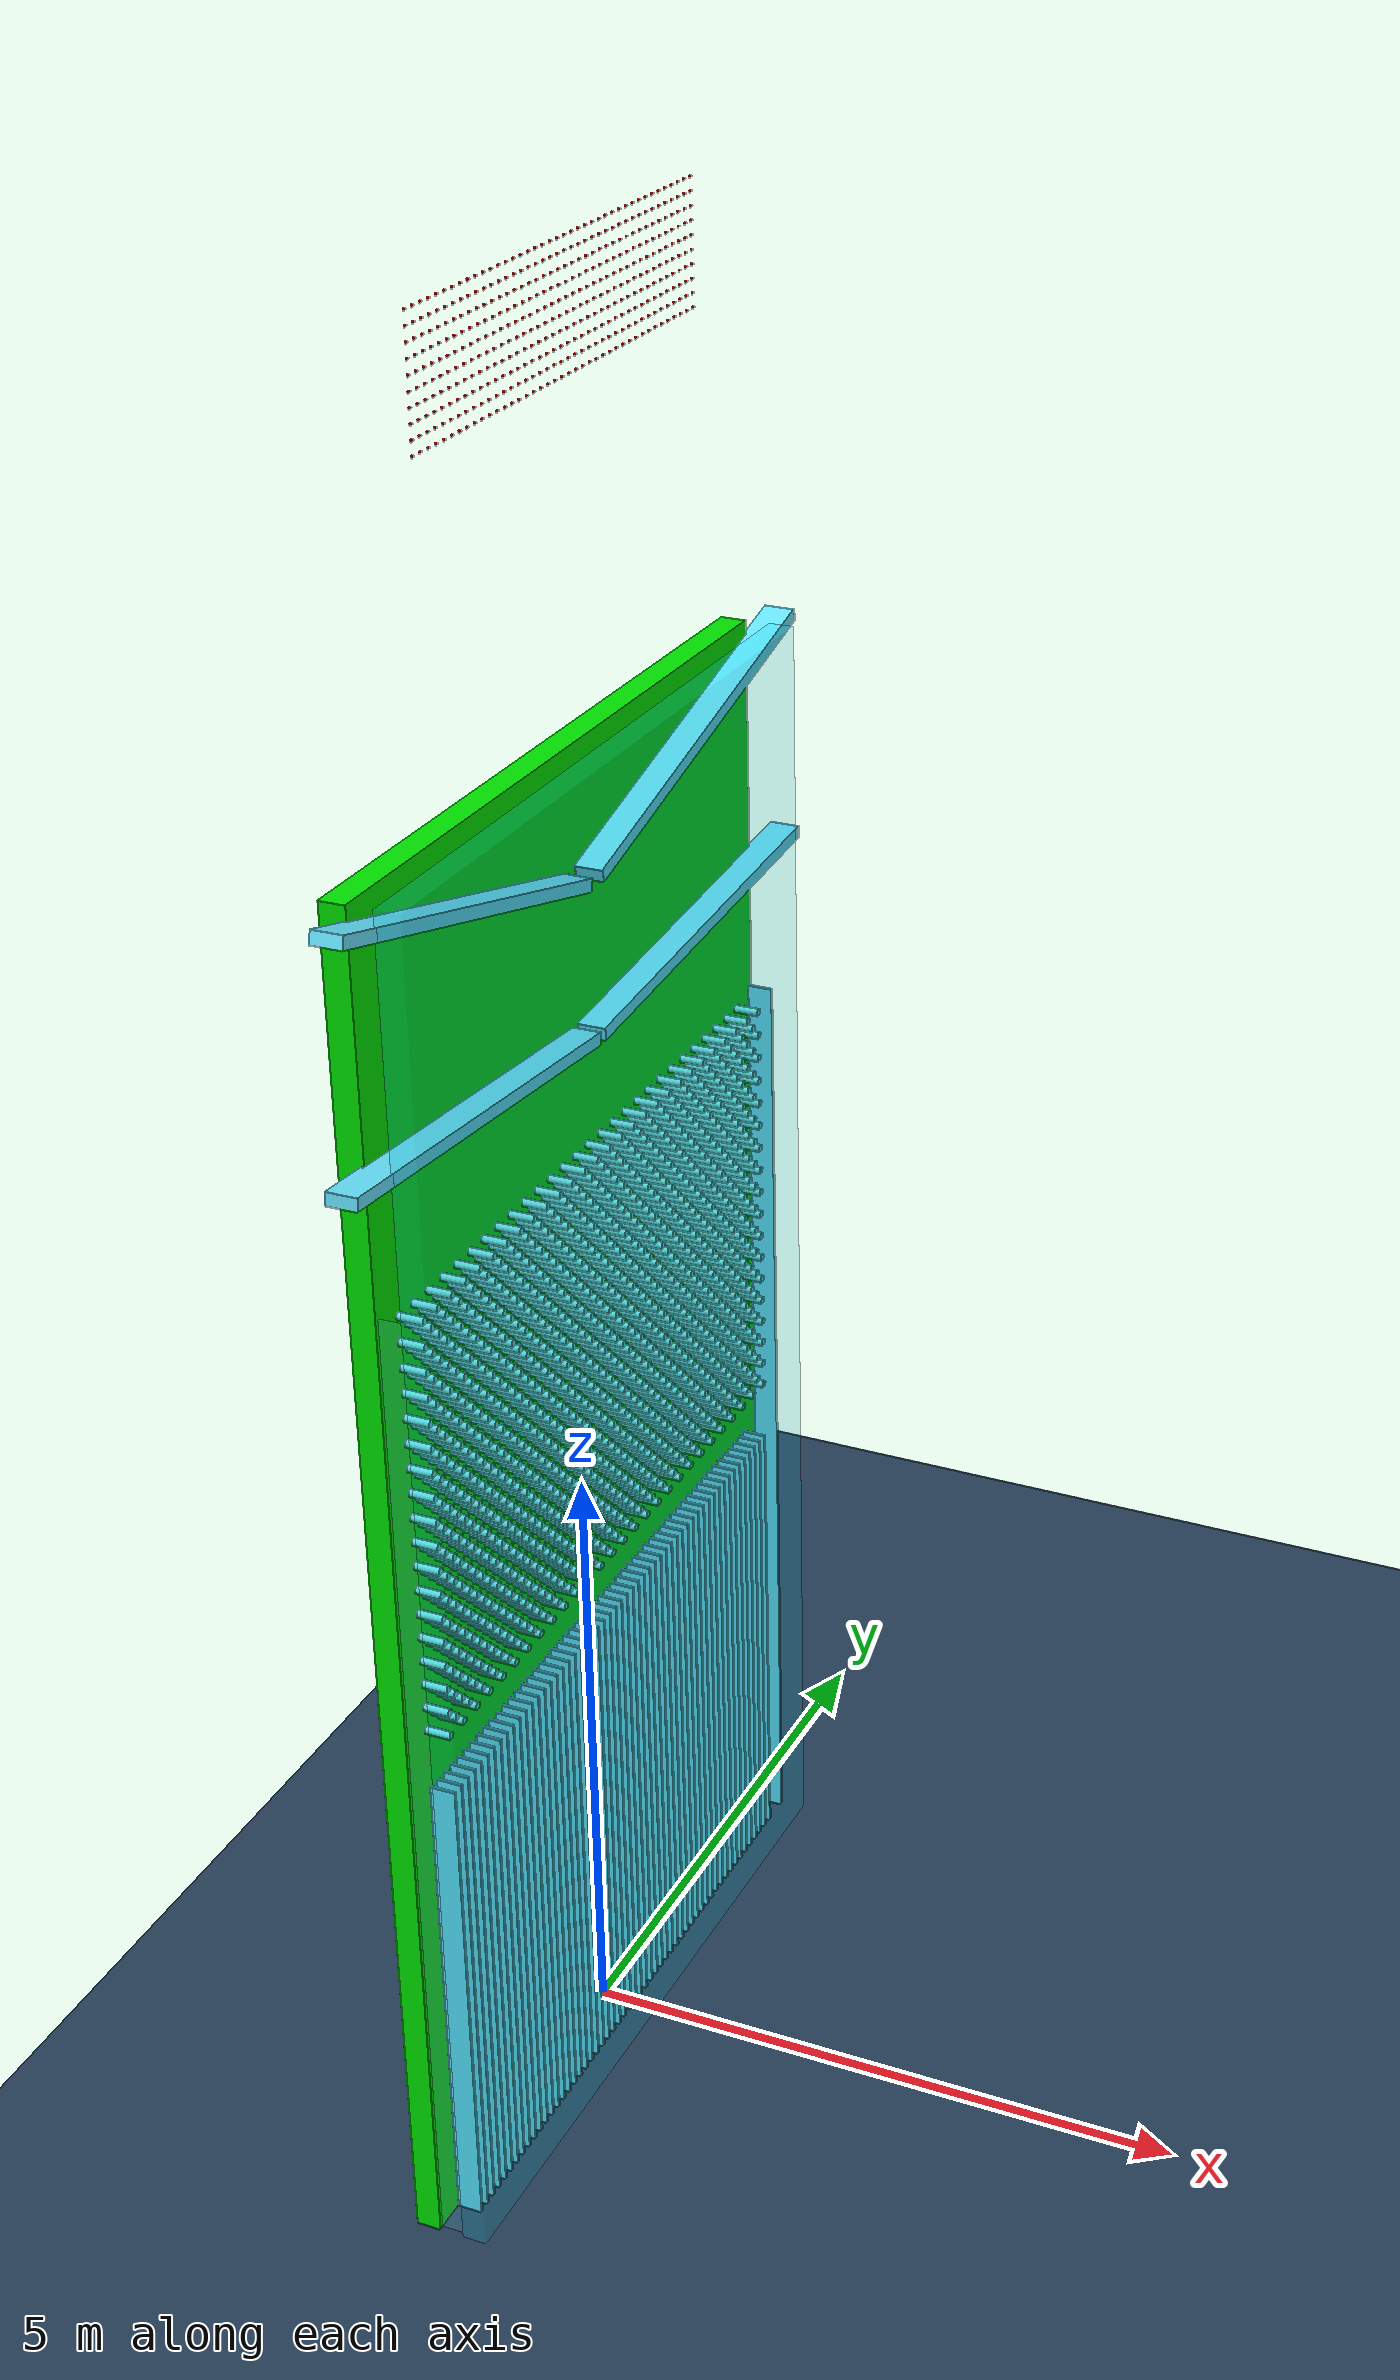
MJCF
<mujoco>
  <visual>
    <headlight diffuse="0.6 0.6 0.6" ambient="0.1 0.1 0.1" specular="0 0 0"/>
    <rgba haze="0.15 0.25 0.35 1"/>
    <global azimuth="120" elevation="-20"/>
  </visual>

  <asset>
    <texture type="skybox" builtin="gradient" rgb1="0.3 0.5 0.7" rgb2="0 0 0" width="512" height="3072"/>
    <texture type="2d" name="groundplane" builtin="checker" mark="edge" rgb1="0.2 0.3 0.4" rgb2="0.1 0.2 0.3"
      markrgb="0.8 0.8 0.8" width="300" height="300"/>
    <material name="groundplane" texture="groundplane" texuniform="true" texrepeat="5 5" reflectance="0.2"/>
  </asset>

  <worldbody>
    <light pos="0 0 1.5" dir="0 0 -1" directional="true"/>
    <geom name="floor" size="0 0 0.05" type="plane" material="groundplane"/>
      <body name="backboard" pos="0 0 5.5">
			  <geom type="box" size=".1 3 5.5" rgba="0 .9 0 1	"/>
	  </body>
      <body name="frontboard" pos="0.4 0 5.5">
			  <geom type="box" size=".1 3 5.5" rgba="0 .9 09 .1"/>
	  </body>

      <body name="left_column" pos=".2 -2.95 4">
			  <geom type="box" size=".1 .01 4" rgba="0.4 .9 09 .1"/>
		  </body>
      <body name="right_column" pos=".2 2.95 4">
			  <geom type="box" size=".1 .01 4" rgba="0.4 .9 09 1"/>
		  </body>

      <body name="left_ball_ramp" pos=".2 -1.75 9" euler="85 0 0">
			  <geom type="box" size=".12 .05 1.72" rgba="0.4 .9 09 1"/>
	  </body>

      <body name="right_ball_ramp" pos=".2 1.75 9" euler="-85 0 0">
			  <geom type="box" size=".12 .05 1.72    " rgba="0.4 .9 09 1"/>
	  </body>

      <body name="left_ball_ramp3" pos=".2 -1.75 10.5" euler="75 0 0">
			  <geom type="box" size=".12 .05 1.72" rgba="0.4 .9 09 1"/>
	  </body>

      <body name="right_ball_ramp3" pos=".2 1.75 10.5" euler="-75 0 0">
			  <geom type="box" size=".12 .05 1.72    " rgba="0.4 .9 09 1"/>

	  </body>

       <body pos=".2 -2.01 13.6">
	          <freejoint />
			  <geom type="sphere" size=".01" rgba="1 0. 0 1"/>
	  </body>
 <body pos=".2 -2.01 13.7">
	          <freejoint />
			  <geom type="sphere" size=".01" rgba="1 0. 0 1"/>
	  </body>
 <body pos=".2 -2.01 13.799999999999999">
	          <freejoint />
			  <geom type="sphere" size=".01" rgba="1 0. 0 1"/>
	  </body>
 <body pos=".2 -2.01 13.9">
	          <freejoint />
			  <geom type="sphere" size=".01" rgba="1 0. 0 1"/>
	  </body>
 <body pos=".2 -2.01 14.0">
	          <freejoint />
			  <geom type="sphere" size=".01" rgba="1 0. 0 1"/>
	  </body>
 <body pos=".2 -2.01 14.1">
	          <freejoint />
			  <geom type="sphere" size=".01" rgba="1 0. 0 1"/>
	  </body>
 <body pos=".2 -2.01 14.2">
	          <freejoint />
			  <geom type="sphere" size=".01" rgba="1 0. 0 1"/>
	  </body>
 <body pos=".2 -2.01 14.299999999999999">
	          <freejoint />
			  <geom type="sphere" size=".01" rgba="1 0. 0 1"/>
	  </body>
 <body pos=".2 -2.01 14.4">
	          <freejoint />
			  <geom type="sphere" size=".01" rgba="1 0. 0 1"/>
	  </body>
 <body pos=".2 -2.01 14.5">
	          <freejoint />
			  <geom type="sphere" size=".01" rgba="1 0. 0 1"/>
	  </body>
 <body pos=".2 -1.9099999999999997 13.6">
	          <freejoint />
			  <geom type="sphere" size=".01" rgba="1 0. 0 1"/>
	  </body>
 <body pos=".2 -1.9099999999999997 13.7">
	          <freejoint />
			  <geom type="sphere" size=".01" rgba="1 0. 0 1"/>
	  </body>
 <body pos=".2 -1.9099999999999997 13.799999999999999">
	          <freejoint />
			  <geom type="sphere" size=".01" rgba="1 0. 0 1"/>
	  </body>
 <body pos=".2 -1.9099999999999997 13.9">
	          <freejoint />
			  <geom type="sphere" size=".01" rgba="1 0. 0 1"/>
	  </body>
 <body pos=".2 -1.9099999999999997 14.0">
	          <freejoint />
			  <geom type="sphere" size=".01" rgba="1 0. 0 1"/>
	  </body>
 <body pos=".2 -1.9099999999999997 14.1">
	          <freejoint />
			  <geom type="sphere" size=".01" rgba="1 0. 0 1"/>
	  </body>
 <body pos=".2 -1.9099999999999997 14.2">
	          <freejoint />
			  <geom type="sphere" size=".01" rgba="1 0. 0 1"/>
	  </body>
 <body pos=".2 -1.9099999999999997 14.299999999999999">
	          <freejoint />
			  <geom type="sphere" size=".01" rgba="1 0. 0 1"/>
	  </body>
 <body pos=".2 -1.9099999999999997 14.4">
	          <freejoint />
			  <geom type="sphere" size=".01" rgba="1 0. 0 1"/>
	  </body>
 <body pos=".2 -1.9099999999999997 14.5">
	          <freejoint />
			  <geom type="sphere" size=".01" rgba="1 0. 0 1"/>
	  </body>
 <body pos=".2 -1.8099999999999996 13.6">
	          <freejoint />
			  <geom type="sphere" size=".01" rgba="1 0. 0 1"/>
	  </body>
 <body pos=".2 -1.8099999999999996 13.7">
	          <freejoint />
			  <geom type="sphere" size=".01" rgba="1 0. 0 1"/>
	  </body>
 <body pos=".2 -1.8099999999999996 13.799999999999999">
	          <freejoint />
			  <geom type="sphere" size=".01" rgba="1 0. 0 1"/>
	  </body>
 <body pos=".2 -1.8099999999999996 13.9">
	          <freejoint />
			  <geom type="sphere" size=".01" rgba="1 0. 0 1"/>
	  </body>
 <body pos=".2 -1.8099999999999996 14.0">
	          <freejoint />
			  <geom type="sphere" size=".01" rgba="1 0. 0 1"/>
	  </body>
 <body pos=".2 -1.8099999999999996 14.1">
	          <freejoint />
			  <geom type="sphere" size=".01" rgba="1 0. 0 1"/>
	  </body>
 <body pos=".2 -1.8099999999999996 14.2">
	          <freejoint />
			  <geom type="sphere" size=".01" rgba="1 0. 0 1"/>
	  </body>
 <body pos=".2 -1.8099999999999996 14.299999999999999">
	          <freejoint />
			  <geom type="sphere" size=".01" rgba="1 0. 0 1"/>
	  </body>
 <body pos=".2 -1.8099999999999996 14.4">
	          <freejoint />
			  <geom type="sphere" size=".01" rgba="1 0. 0 1"/>
	  </body>
 <body pos=".2 -1.8099999999999996 14.5">
	          <freejoint />
			  <geom type="sphere" size=".01" rgba="1 0. 0 1"/>
	  </body>
 <body pos=".2 -1.7099999999999995 13.6">
	          <freejoint />
			  <geom type="sphere" size=".01" rgba="1 0. 0 1"/>
	  </body>
 <body pos=".2 -1.7099999999999995 13.7">
	          <freejoint />
			  <geom type="sphere" size=".01" rgba="1 0. 0 1"/>
	  </body>
 <body pos=".2 -1.7099999999999995 13.799999999999999">
	          <freejoint />
			  <geom type="sphere" size=".01" rgba="1 0. 0 1"/>
	  </body>
 <body pos=".2 -1.7099999999999995 13.9">
	          <freejoint />
			  <geom type="sphere" size=".01" rgba="1 0. 0 1"/>
	  </body>
 <body pos=".2 -1.7099999999999995 14.0">
	          <freejoint />
			  <geom type="sphere" size=".01" rgba="1 0. 0 1"/>
	  </body>
 <body pos=".2 -1.7099999999999995 14.1">
	          <freejoint />
			  <geom type="sphere" size=".01" rgba="1 0. 0 1"/>
	  </body>
 <body pos=".2 -1.7099999999999995 14.2">
	          <freejoint />
			  <geom type="sphere" size=".01" rgba="1 0. 0 1"/>
	  </body>
 <body pos=".2 -1.7099999999999995 14.299999999999999">
	          <freejoint />
			  <geom type="sphere" size=".01" rgba="1 0. 0 1"/>
	  </body>
 <body pos=".2 -1.7099999999999995 14.4">
	          <freejoint />
			  <geom type="sphere" size=".01" rgba="1 0. 0 1"/>
	  </body>
 <body pos=".2 -1.7099999999999995 14.5">
	          <freejoint />
			  <geom type="sphere" size=".01" rgba="1 0. 0 1"/>
	  </body>
 <body pos=".2 -1.6099999999999994 13.6">
	          <freejoint />
			  <geom type="sphere" size=".01" rgba="1 0. 0 1"/>
	  </body>
 <body pos=".2 -1.6099999999999994 13.7">
	          <freejoint />
			  <geom type="sphere" size=".01" rgba="1 0. 0 1"/>
	  </body>
 <body pos=".2 -1.6099999999999994 13.799999999999999">
	          <freejoint />
			  <geom type="sphere" size=".01" rgba="1 0. 0 1"/>
	  </body>
 <body pos=".2 -1.6099999999999994 13.9">
	          <freejoint />
			  <geom type="sphere" size=".01" rgba="1 0. 0 1"/>
	  </body>
 <body pos=".2 -1.6099999999999994 14.0">
	          <freejoint />
			  <geom type="sphere" size=".01" rgba="1 0. 0 1"/>
	  </body>
 <body pos=".2 -1.6099999999999994 14.1">
	          <freejoint />
			  <geom type="sphere" size=".01" rgba="1 0. 0 1"/>
	  </body>
 <body pos=".2 -1.6099999999999994 14.2">
	          <freejoint />
			  <geom type="sphere" size=".01" rgba="1 0. 0 1"/>
	  </body>
 <body pos=".2 -1.6099999999999994 14.299999999999999">
	          <freejoint />
			  <geom type="sphere" size=".01" rgba="1 0. 0 1"/>
	  </body>
 <body pos=".2 -1.6099999999999994 14.4">
	          <freejoint />
			  <geom type="sphere" size=".01" rgba="1 0. 0 1"/>
	  </body>
 <body pos=".2 -1.6099999999999994 14.5">
	          <freejoint />
			  <geom type="sphere" size=".01" rgba="1 0. 0 1"/>
	  </body>
 <body pos=".2 -1.5099999999999993 13.6">
	          <freejoint />
			  <geom type="sphere" size=".01" rgba="1 0. 0 1"/>
	  </body>
 <body pos=".2 -1.5099999999999993 13.7">
	          <freejoint />
			  <geom type="sphere" size=".01" rgba="1 0. 0 1"/>
	  </body>
 <body pos=".2 -1.5099999999999993 13.799999999999999">
	          <freejoint />
			  <geom type="sphere" size=".01" rgba="1 0. 0 1"/>
	  </body>
 <body pos=".2 -1.5099999999999993 13.9">
	          <freejoint />
			  <geom type="sphere" size=".01" rgba="1 0. 0 1"/>
	  </body>
 <body pos=".2 -1.5099999999999993 14.0">
	          <freejoint />
			  <geom type="sphere" size=".01" rgba="1 0. 0 1"/>
	  </body>
 <body pos=".2 -1.5099999999999993 14.1">
	          <freejoint />
			  <geom type="sphere" size=".01" rgba="1 0. 0 1"/>
	  </body>
 <body pos=".2 -1.5099999999999993 14.2">
	          <freejoint />
			  <geom type="sphere" size=".01" rgba="1 0. 0 1"/>
	  </body>
 <body pos=".2 -1.5099999999999993 14.299999999999999">
	          <freejoint />
			  <geom type="sphere" size=".01" rgba="1 0. 0 1"/>
	  </body>
 <body pos=".2 -1.5099999999999993 14.4">
	          <freejoint />
			  <geom type="sphere" size=".01" rgba="1 0. 0 1"/>
	  </body>
 <body pos=".2 -1.5099999999999993 14.5">
	          <freejoint />
			  <geom type="sphere" size=".01" rgba="1 0. 0 1"/>
	  </body>
 <body pos=".2 -1.4099999999999993 13.6">
	          <freejoint />
			  <geom type="sphere" size=".01" rgba="1 0. 0 1"/>
	  </body>
 <body pos=".2 -1.4099999999999993 13.7">
	          <freejoint />
			  <geom type="sphere" size=".01" rgba="1 0. 0 1"/>
	  </body>
 <body pos=".2 -1.4099999999999993 13.799999999999999">
	          <freejoint />
			  <geom type="sphere" size=".01" rgba="1 0. 0 1"/>
	  </body>
 <body pos=".2 -1.4099999999999993 13.9">
	          <freejoint />
			  <geom type="sphere" size=".01" rgba="1 0. 0 1"/>
	  </body>
 <body pos=".2 -1.4099999999999993 14.0">
	          <freejoint />
			  <geom type="sphere" size=".01" rgba="1 0. 0 1"/>
	  </body>
 <body pos=".2 -1.4099999999999993 14.1">
	          <freejoint />
			  <geom type="sphere" size=".01" rgba="1 0. 0 1"/>
	  </body>
 <body pos=".2 -1.4099999999999993 14.2">
	          <freejoint />
			  <geom type="sphere" size=".01" rgba="1 0. 0 1"/>
	  </body>
 <body pos=".2 -1.4099999999999993 14.299999999999999">
	          <freejoint />
			  <geom type="sphere" size=".01" rgba="1 0. 0 1"/>
	  </body>
 <body pos=".2 -1.4099999999999993 14.4">
	          <freejoint />
			  <geom type="sphere" size=".01" rgba="1 0. 0 1"/>
	  </body>
 <body pos=".2 -1.4099999999999993 14.5">
	          <freejoint />
			  <geom type="sphere" size=".01" rgba="1 0. 0 1"/>
	  </body>
 <body pos=".2 -1.3099999999999992 13.6">
	          <freejoint />
			  <geom type="sphere" size=".01" rgba="1 0. 0 1"/>
	  </body>
 <body pos=".2 -1.3099999999999992 13.7">
	          <freejoint />
			  <geom type="sphere" size=".01" rgba="1 0. 0 1"/>
	  </body>
 <body pos=".2 -1.3099999999999992 13.799999999999999">
	          <freejoint />
			  <geom type="sphere" size=".01" rgba="1 0. 0 1"/>
	  </body>
 <body pos=".2 -1.3099999999999992 13.9">
	          <freejoint />
			  <geom type="sphere" size=".01" rgba="1 0. 0 1"/>
	  </body>
 <body pos=".2 -1.3099999999999992 14.0">
	          <freejoint />
			  <geom type="sphere" size=".01" rgba="1 0. 0 1"/>
	  </body>
 <body pos=".2 -1.3099999999999992 14.1">
	          <freejoint />
			  <geom type="sphere" size=".01" rgba="1 0. 0 1"/>
	  </body>
 <body pos=".2 -1.3099999999999992 14.2">
	          <freejoint />
			  <geom type="sphere" size=".01" rgba="1 0. 0 1"/>
	  </body>
 <body pos=".2 -1.3099999999999992 14.299999999999999">
	          <freejoint />
			  <geom type="sphere" size=".01" rgba="1 0. 0 1"/>
	  </body>
 <body pos=".2 -1.3099999999999992 14.4">
	          <freejoint />
			  <geom type="sphere" size=".01" rgba="1 0. 0 1"/>
	  </body>
 <body pos=".2 -1.3099999999999992 14.5">
	          <freejoint />
			  <geom type="sphere" size=".01" rgba="1 0. 0 1"/>
	  </body>
 <body pos=".2 -1.209999999999999 13.6">
	          <freejoint />
			  <geom type="sphere" size=".01" rgba="1 0. 0 1"/>
	  </body>
 <body pos=".2 -1.209999999999999 13.7">
	          <freejoint />
			  <geom type="sphere" size=".01" rgba="1 0. 0 1"/>
	  </body>
 <body pos=".2 -1.209999999999999 13.799999999999999">
	          <freejoint />
			  <geom type="sphere" size=".01" rgba="1 0. 0 1"/>
	  </body>
 <body pos=".2 -1.209999999999999 13.9">
	          <freejoint />
			  <geom type="sphere" size=".01" rgba="1 0. 0 1"/>
	  </body>
 <body pos=".2 -1.209999999999999 14.0">
	          <freejoint />
			  <geom type="sphere" size=".01" rgba="1 0. 0 1"/>
	  </body>
 <body pos=".2 -1.209999999999999 14.1">
	          <freejoint />
			  <geom type="sphere" size=".01" rgba="1 0. 0 1"/>
	  </body>
 <body pos=".2 -1.209999999999999 14.2">
	          <freejoint />
			  <geom type="sphere" size=".01" rgba="1 0. 0 1"/>
	  </body>
 <body pos=".2 -1.209999999999999 14.299999999999999">
	          <freejoint />
			  <geom type="sphere" size=".01" rgba="1 0. 0 1"/>
	  </body>
 <body pos=".2 -1.209999999999999 14.4">
	          <freejoint />
			  <geom type="sphere" size=".01" rgba="1 0. 0 1"/>
	  </body>
 <body pos=".2 -1.209999999999999 14.5">
	          <freejoint />
			  <geom type="sphere" size=".01" rgba="1 0. 0 1"/>
	  </body>
 <body pos=".2 -1.109999999999999 13.6">
	          <freejoint />
			  <geom type="sphere" size=".01" rgba="1 0. 0 1"/>
	  </body>
 <body pos=".2 -1.109999999999999 13.7">
	          <freejoint />
			  <geom type="sphere" size=".01" rgba="1 0. 0 1"/>
	  </body>
 <body pos=".2 -1.109999999999999 13.799999999999999">
	          <freejoint />
			  <geom type="sphere" size=".01" rgba="1 0. 0 1"/>
	  </body>
 <body pos=".2 -1.109999999999999 13.9">
	          <freejoint />
			  <geom type="sphere" size=".01" rgba="1 0. 0 1"/>
	  </body>
 <body pos=".2 -1.109999999999999 14.0">
	          <freejoint />
			  <geom type="sphere" size=".01" rgba="1 0. 0 1"/>
	  </body>
 <body pos=".2 -1.109999999999999 14.1">
	          <freejoint />
			  <geom type="sphere" size=".01" rgba="1 0. 0 1"/>
	  </body>
 <body pos=".2 -1.109999999999999 14.2">
	          <freejoint />
			  <geom type="sphere" size=".01" rgba="1 0. 0 1"/>
	  </body>
 <body pos=".2 -1.109999999999999 14.299999999999999">
	          <freejoint />
			  <geom type="sphere" size=".01" rgba="1 0. 0 1"/>
	  </body>
 <body pos=".2 -1.109999999999999 14.4">
	          <freejoint />
			  <geom type="sphere" size=".01" rgba="1 0. 0 1"/>
	  </body>
 <body pos=".2 -1.109999999999999 14.5">
	          <freejoint />
			  <geom type="sphere" size=".01" rgba="1 0. 0 1"/>
	  </body>
 <body pos=".2 -1.009999999999999 13.6">
	          <freejoint />
			  <geom type="sphere" size=".01" rgba="1 0. 0 1"/>
	  </body>
 <body pos=".2 -1.009999999999999 13.7">
	          <freejoint />
			  <geom type="sphere" size=".01" rgba="1 0. 0 1"/>
	  </body>
 <body pos=".2 -1.009999999999999 13.799999999999999">
	          <freejoint />
			  <geom type="sphere" size=".01" rgba="1 0. 0 1"/>
	  </body>
 <body pos=".2 -1.009999999999999 13.9">
	          <freejoint />
			  <geom type="sphere" size=".01" rgba="1 0. 0 1"/>
	  </body>
 <body pos=".2 -1.009999999999999 14.0">
	          <freejoint />
			  <geom type="sphere" size=".01" rgba="1 0. 0 1"/>
	  </body>
 <body pos=".2 -1.009999999999999 14.1">
	          <freejoint />
			  <geom type="sphere" size=".01" rgba="1 0. 0 1"/>
	  </body>
 <body pos=".2 -1.009999999999999 14.2">
	          <freejoint />
			  <geom type="sphere" size=".01" rgba="1 0. 0 1"/>
	  </body>
 <body pos=".2 -1.009999999999999 14.299999999999999">
	          <freejoint />
			  <geom type="sphere" size=".01" rgba="1 0. 0 1"/>
	  </body>
 <body pos=".2 -1.009999999999999 14.4">
	          <freejoint />
			  <geom type="sphere" size=".01" rgba="1 0. 0 1"/>
	  </body>
 <body pos=".2 -1.009999999999999 14.5">
	          <freejoint />
			  <geom type="sphere" size=".01" rgba="1 0. 0 1"/>
	  </body>
 <body pos=".2 -0.9099999999999988 13.6">
	          <freejoint />
			  <geom type="sphere" size=".01" rgba="1 0. 0 1"/>
	  </body>
 <body pos=".2 -0.9099999999999988 13.7">
	          <freejoint />
			  <geom type="sphere" size=".01" rgba="1 0. 0 1"/>
	  </body>
 <body pos=".2 -0.9099999999999988 13.799999999999999">
	          <freejoint />
			  <geom type="sphere" size=".01" rgba="1 0. 0 1"/>
	  </body>
 <body pos=".2 -0.9099999999999988 13.9">
	          <freejoint />
			  <geom type="sphere" size=".01" rgba="1 0. 0 1"/>
	  </body>
 <body pos=".2 -0.9099999999999988 14.0">
	          <freejoint />
			  <geom type="sphere" size=".01" rgba="1 0. 0 1"/>
	  </body>
 <body pos=".2 -0.9099999999999988 14.1">
	          <freejoint />
			  <geom type="sphere" size=".01" rgba="1 0. 0 1"/>
	  </body>
 <body pos=".2 -0.9099999999999988 14.2">
	          <freejoint />
			  <geom type="sphere" size=".01" rgba="1 0. 0 1"/>
	  </body>
 <body pos=".2 -0.9099999999999988 14.299999999999999">
	          <freejoint />
			  <geom type="sphere" size=".01" rgba="1 0. 0 1"/>
	  </body>
 <body pos=".2 -0.9099999999999988 14.4">
	          <freejoint />
			  <geom type="sphere" size=".01" rgba="1 0. 0 1"/>
	  </body>
 <body pos=".2 -0.9099999999999988 14.5">
	          <freejoint />
			  <geom type="sphere" size=".01" rgba="1 0. 0 1"/>
	  </body>
 <body pos=".2 -0.8099999999999987 13.6">
	          <freejoint />
			  <geom type="sphere" size=".01" rgba="1 0. 0 1"/>
	  </body>
 <body pos=".2 -0.8099999999999987 13.7">
	          <freejoint />
			  <geom type="sphere" size=".01" rgba="1 0. 0 1"/>
	  </body>
 <body pos=".2 -0.8099999999999987 13.799999999999999">
	          <freejoint />
			  <geom type="sphere" size=".01" rgba="1 0. 0 1"/>
	  </body>
 <body pos=".2 -0.8099999999999987 13.9">
	          <freejoint />
			  <geom type="sphere" size=".01" rgba="1 0. 0 1"/>
	  </body>
 <body pos=".2 -0.8099999999999987 14.0">
	          <freejoint />
			  <geom type="sphere" size=".01" rgba="1 0. 0 1"/>
	  </body>
 <body pos=".2 -0.8099999999999987 14.1">
	          <freejoint />
			  <geom type="sphere" size=".01" rgba="1 0. 0 1"/>
	  </body>
 <body pos=".2 -0.8099999999999987 14.2">
	          <freejoint />
			  <geom type="sphere" size=".01" rgba="1 0. 0 1"/>
	  </body>
 <body pos=".2 -0.8099999999999987 14.299999999999999">
	          <freejoint />
			  <geom type="sphere" size=".01" rgba="1 0. 0 1"/>
	  </body>
 <body pos=".2 -0.8099999999999987 14.4">
	          <freejoint />
			  <geom type="sphere" size=".01" rgba="1 0. 0 1"/>
	  </body>
 <body pos=".2 -0.8099999999999987 14.5">
	          <freejoint />
			  <geom type="sphere" size=".01" rgba="1 0. 0 1"/>
	  </body>
 <body pos=".2 -0.7099999999999986 13.6">
	          <freejoint />
			  <geom type="sphere" size=".01" rgba="1 0. 0 1"/>
	  </body>
 <body pos=".2 -0.7099999999999986 13.7">
	          <freejoint />
			  <geom type="sphere" size=".01" rgba="1 0. 0 1"/>
	  </body>
 <body pos=".2 -0.7099999999999986 13.799999999999999">
	          <freejoint />
			  <geom type="sphere" size=".01" rgba="1 0. 0 1"/>
	  </body>
 <body pos=".2 -0.7099999999999986 13.9">
	          <freejoint />
			  <geom type="sphere" size=".01" rgba="1 0. 0 1"/>
	  </body>
 <body pos=".2 -0.7099999999999986 14.0">
	          <freejoint />
			  <geom type="sphere" size=".01" rgba="1 0. 0 1"/>
	  </body>
 <body pos=".2 -0.7099999999999986 14.1">
	          <freejoint />
			  <geom type="sphere" size=".01" rgba="1 0. 0 1"/>
	  </body>
 <body pos=".2 -0.7099999999999986 14.2">
	          <freejoint />
			  <geom type="sphere" size=".01" rgba="1 0. 0 1"/>
	  </body>
 <body pos=".2 -0.7099999999999986 14.299999999999999">
	          <freejoint />
			  <geom type="sphere" size=".01" rgba="1 0. 0 1"/>
	  </body>
 <body pos=".2 -0.7099999999999986 14.4">
	          <freejoint />
			  <geom type="sphere" size=".01" rgba="1 0. 0 1"/>
	  </body>
 <body pos=".2 -0.7099999999999986 14.5">
	          <freejoint />
			  <geom type="sphere" size=".01" rgba="1 0. 0 1"/>
	  </body>
 <body pos=".2 -0.6099999999999985 13.6">
	          <freejoint />
			  <geom type="sphere" size=".01" rgba="1 0. 0 1"/>
	  </body>
 <body pos=".2 -0.6099999999999985 13.7">
	          <freejoint />
			  <geom type="sphere" size=".01" rgba="1 0. 0 1"/>
	  </body>
 <body pos=".2 -0.6099999999999985 13.799999999999999">
	          <freejoint />
			  <geom type="sphere" size=".01" rgba="1 0. 0 1"/>
	  </body>
 <body pos=".2 -0.6099999999999985 13.9">
	          <freejoint />
			  <geom type="sphere" size=".01" rgba="1 0. 0 1"/>
	  </body>
 <body pos=".2 -0.6099999999999985 14.0">
	          <freejoint />
			  <geom type="sphere" size=".01" rgba="1 0. 0 1"/>
	  </body>
 <body pos=".2 -0.6099999999999985 14.1">
	          <freejoint />
			  <geom type="sphere" size=".01" rgba="1 0. 0 1"/>
	  </body>
 <body pos=".2 -0.6099999999999985 14.2">
	          <freejoint />
			  <geom type="sphere" size=".01" rgba="1 0. 0 1"/>
	  </body>
 <body pos=".2 -0.6099999999999985 14.299999999999999">
	          <freejoint />
			  <geom type="sphere" size=".01" rgba="1 0. 0 1"/>
	  </body>
 <body pos=".2 -0.6099999999999985 14.4">
	          <freejoint />
			  <geom type="sphere" size=".01" rgba="1 0. 0 1"/>
	  </body>
 <body pos=".2 -0.6099999999999985 14.5">
	          <freejoint />
			  <geom type="sphere" size=".01" rgba="1 0. 0 1"/>
	  </body>
 <body pos=".2 -0.5099999999999985 13.6">
	          <freejoint />
			  <geom type="sphere" size=".01" rgba="1 0. 0 1"/>
	  </body>
 <body pos=".2 -0.5099999999999985 13.7">
	          <freejoint />
			  <geom type="sphere" size=".01" rgba="1 0. 0 1"/>
	  </body>
 <body pos=".2 -0.5099999999999985 13.799999999999999">
	          <freejoint />
			  <geom type="sphere" size=".01" rgba="1 0. 0 1"/>
	  </body>
 <body pos=".2 -0.5099999999999985 13.9">
	          <freejoint />
			  <geom type="sphere" size=".01" rgba="1 0. 0 1"/>
	  </body>
 <body pos=".2 -0.5099999999999985 14.0">
	          <freejoint />
			  <geom type="sphere" size=".01" rgba="1 0. 0 1"/>
	  </body>
 <body pos=".2 -0.5099999999999985 14.1">
	          <freejoint />
			  <geom type="sphere" size=".01" rgba="1 0. 0 1"/>
	  </body>
 <body pos=".2 -0.5099999999999985 14.2">
	          <freejoint />
			  <geom type="sphere" size=".01" rgba="1 0. 0 1"/>
	  </body>
 <body pos=".2 -0.5099999999999985 14.299999999999999">
	          <freejoint />
			  <geom type="sphere" size=".01" rgba="1 0. 0 1"/>
	  </body>
 <body pos=".2 -0.5099999999999985 14.4">
	          <freejoint />
			  <geom type="sphere" size=".01" rgba="1 0. 0 1"/>
	  </body>
 <body pos=".2 -0.5099999999999985 14.5">
	          <freejoint />
			  <geom type="sphere" size=".01" rgba="1 0. 0 1"/>
	  </body>
 <body pos=".2 -0.40999999999999837 13.6">
	          <freejoint />
			  <geom type="sphere" size=".01" rgba="1 0. 0 1"/>
	  </body>
 <body pos=".2 -0.40999999999999837 13.7">
	          <freejoint />
			  <geom type="sphere" size=".01" rgba="1 0. 0 1"/>
	  </body>
 <body pos=".2 -0.40999999999999837 13.799999999999999">
	          <freejoint />
			  <geom type="sphere" size=".01" rgba="1 0. 0 1"/>
	  </body>
 <body pos=".2 -0.40999999999999837 13.9">
	          <freejoint />
			  <geom type="sphere" size=".01" rgba="1 0. 0 1"/>
	  </body>
 <body pos=".2 -0.40999999999999837 14.0">
	          <freejoint />
			  <geom type="sphere" size=".01" rgba="1 0. 0 1"/>
	  </body>
 <body pos=".2 -0.40999999999999837 14.1">
	          <freejoint />
			  <geom type="sphere" size=".01" rgba="1 0. 0 1"/>
	  </body>
 <body pos=".2 -0.40999999999999837 14.2">
	          <freejoint />
			  <geom type="sphere" size=".01" rgba="1 0. 0 1"/>
	  </body>
 <body pos=".2 -0.40999999999999837 14.299999999999999">
	          <freejoint />
			  <geom type="sphere" size=".01" rgba="1 0. 0 1"/>
	  </body>
 <body pos=".2 -0.40999999999999837 14.4">
	          <freejoint />
			  <geom type="sphere" size=".01" rgba="1 0. 0 1"/>
	  </body>
 <body pos=".2 -0.40999999999999837 14.5">
	          <freejoint />
			  <geom type="sphere" size=".01" rgba="1 0. 0 1"/>
	  </body>
 <body pos=".2 -0.3099999999999983 13.6">
	          <freejoint />
			  <geom type="sphere" size=".01" rgba="1 0. 0 1"/>
	  </body>
 <body pos=".2 -0.3099999999999983 13.7">
	          <freejoint />
			  <geom type="sphere" size=".01" rgba="1 0. 0 1"/>
	  </body>
 <body pos=".2 -0.3099999999999983 13.799999999999999">
	          <freejoint />
			  <geom type="sphere" size=".01" rgba="1 0. 0 1"/>
	  </body>
 <body pos=".2 -0.3099999999999983 13.9">
	          <freejoint />
			  <geom type="sphere" size=".01" rgba="1 0. 0 1"/>
	  </body>
 <body pos=".2 -0.3099999999999983 14.0">
	          <freejoint />
			  <geom type="sphere" size=".01" rgba="1 0. 0 1"/>
	  </body>
 <body pos=".2 -0.3099999999999983 14.1">
	          <freejoint />
			  <geom type="sphere" size=".01" rgba="1 0. 0 1"/>
	  </body>
 <body pos=".2 -0.3099999999999983 14.2">
	          <freejoint />
			  <geom type="sphere" size=".01" rgba="1 0. 0 1"/>
	  </body>
 <body pos=".2 -0.3099999999999983 14.299999999999999">
	          <freejoint />
			  <geom type="sphere" size=".01" rgba="1 0. 0 1"/>
	  </body>
 <body pos=".2 -0.3099999999999983 14.4">
	          <freejoint />
			  <geom type="sphere" size=".01" rgba="1 0. 0 1"/>
	  </body>
 <body pos=".2 -0.3099999999999983 14.5">
	          <freejoint />
			  <geom type="sphere" size=".01" rgba="1 0. 0 1"/>
	  </body>
 <body pos=".2 -0.2099999999999982 13.6">
	          <freejoint />
			  <geom type="sphere" size=".01" rgba="1 0. 0 1"/>
	  </body>
 <body pos=".2 -0.2099999999999982 13.7">
	          <freejoint />
			  <geom type="sphere" size=".01" rgba="1 0. 0 1"/>
	  </body>
 <body pos=".2 -0.2099999999999982 13.799999999999999">
	          <freejoint />
			  <geom type="sphere" size=".01" rgba="1 0. 0 1"/>
	  </body>
 <body pos=".2 -0.2099999999999982 13.9">
	          <freejoint />
			  <geom type="sphere" size=".01" rgba="1 0. 0 1"/>
	  </body>
 <body pos=".2 -0.2099999999999982 14.0">
	          <freejoint />
			  <geom type="sphere" size=".01" rgba="1 0. 0 1"/>
	  </body>
 <body pos=".2 -0.2099999999999982 14.1">
	          <freejoint />
			  <geom type="sphere" size=".01" rgba="1 0. 0 1"/>
	  </body>
 <body pos=".2 -0.2099999999999982 14.2">
	          <freejoint />
			  <geom type="sphere" size=".01" rgba="1 0. 0 1"/>
	  </body>
 <body pos=".2 -0.2099999999999982 14.299999999999999">
	          <freejoint />
			  <geom type="sphere" size=".01" rgba="1 0. 0 1"/>
	  </body>
 <body pos=".2 -0.2099999999999982 14.4">
	          <freejoint />
			  <geom type="sphere" size=".01" rgba="1 0. 0 1"/>
	  </body>
 <body pos=".2 -0.2099999999999982 14.5">
	          <freejoint />
			  <geom type="sphere" size=".01" rgba="1 0. 0 1"/>
	  </body>
 <body pos=".2 -0.1099999999999981 13.6">
	          <freejoint />
			  <geom type="sphere" size=".01" rgba="1 0. 0 1"/>
	  </body>
 <body pos=".2 -0.1099999999999981 13.7">
	          <freejoint />
			  <geom type="sphere" size=".01" rgba="1 0. 0 1"/>
	  </body>
 <body pos=".2 -0.1099999999999981 13.799999999999999">
	          <freejoint />
			  <geom type="sphere" size=".01" rgba="1 0. 0 1"/>
	  </body>
 <body pos=".2 -0.1099999999999981 13.9">
	          <freejoint />
			  <geom type="sphere" size=".01" rgba="1 0. 0 1"/>
	  </body>
 <body pos=".2 -0.1099999999999981 14.0">
	          <freejoint />
			  <geom type="sphere" size=".01" rgba="1 0. 0 1"/>
	  </body>
 <body pos=".2 -0.1099999999999981 14.1">
	          <freejoint />
			  <geom type="sphere" size=".01" rgba="1 0. 0 1"/>
	  </body>
 <body pos=".2 -0.1099999999999981 14.2">
	          <freejoint />
			  <geom type="sphere" size=".01" rgba="1 0. 0 1"/>
	  </body>
 <body pos=".2 -0.1099999999999981 14.299999999999999">
	          <freejoint />
			  <geom type="sphere" size=".01" rgba="1 0. 0 1"/>
	  </body>
 <body pos=".2 -0.1099999999999981 14.4">
	          <freejoint />
			  <geom type="sphere" size=".01" rgba="1 0. 0 1"/>
	  </body>
 <body pos=".2 -0.1099999999999981 14.5">
	          <freejoint />
			  <geom type="sphere" size=".01" rgba="1 0. 0 1"/>
	  </body>
 <body pos=".2 -0.00999999999999801 13.6">
	          <freejoint />
			  <geom type="sphere" size=".01" rgba="1 0. 0 1"/>
	  </body>
 <body pos=".2 -0.00999999999999801 13.7">
	          <freejoint />
			  <geom type="sphere" size=".01" rgba="1 0. 0 1"/>
	  </body>
 <body pos=".2 -0.00999999999999801 13.799999999999999">
	          <freejoint />
			  <geom type="sphere" size=".01" rgba="1 0. 0 1"/>
	  </body>
 <body pos=".2 -0.00999999999999801 13.9">
	          <freejoint />
			  <geom type="sphere" size=".01" rgba="1 0. 0 1"/>
	  </body>
 <body pos=".2 -0.00999999999999801 14.0">
	          <freejoint />
			  <geom type="sphere" size=".01" rgba="1 0. 0 1"/>
	  </body>
 <body pos=".2 -0.00999999999999801 14.1">
	          <freejoint />
			  <geom type="sphere" size=".01" rgba="1 0. 0 1"/>
	  </body>
 <body pos=".2 -0.00999999999999801 14.2">
	          <freejoint />
			  <geom type="sphere" size=".01" rgba="1 0. 0 1"/>
	  </body>
 <body pos=".2 -0.00999999999999801 14.299999999999999">
	          <freejoint />
			  <geom type="sphere" size=".01" rgba="1 0. 0 1"/>
	  </body>
 <body pos=".2 -0.00999999999999801 14.4">
	          <freejoint />
			  <geom type="sphere" size=".01" rgba="1 0. 0 1"/>
	  </body>
 <body pos=".2 -0.00999999999999801 14.5">
	          <freejoint />
			  <geom type="sphere" size=".01" rgba="1 0. 0 1"/>
	  </body>
 <body pos=".2 0.09000000000000208 13.6">
	          <freejoint />
			  <geom type="sphere" size=".01" rgba="1 0. 0 1"/>
	  </body>
 <body pos=".2 0.09000000000000208 13.7">
	          <freejoint />
			  <geom type="sphere" size=".01" rgba="1 0. 0 1"/>
	  </body>
 <body pos=".2 0.09000000000000208 13.799999999999999">
	          <freejoint />
			  <geom type="sphere" size=".01" rgba="1 0. 0 1"/>
	  </body>
 <body pos=".2 0.09000000000000208 13.9">
	          <freejoint />
			  <geom type="sphere" size=".01" rgba="1 0. 0 1"/>
	  </body>
 <body pos=".2 0.09000000000000208 14.0">
	          <freejoint />
			  <geom type="sphere" size=".01" rgba="1 0. 0 1"/>
	  </body>
 <body pos=".2 0.09000000000000208 14.1">
	          <freejoint />
			  <geom type="sphere" size=".01" rgba="1 0. 0 1"/>
	  </body>
 <body pos=".2 0.09000000000000208 14.2">
	          <freejoint />
			  <geom type="sphere" size=".01" rgba="1 0. 0 1"/>
	  </body>
 <body pos=".2 0.09000000000000208 14.299999999999999">
	          <freejoint />
			  <geom type="sphere" size=".01" rgba="1 0. 0 1"/>
	  </body>
 <body pos=".2 0.09000000000000208 14.4">
	          <freejoint />
			  <geom type="sphere" size=".01" rgba="1 0. 0 1"/>
	  </body>
 <body pos=".2 0.09000000000000208 14.5">
	          <freejoint />
			  <geom type="sphere" size=".01" rgba="1 0. 0 1"/>
	  </body>
 <body pos=".2 0.19000000000000217 13.6">
	          <freejoint />
			  <geom type="sphere" size=".01" rgba="1 0. 0 1"/>
	  </body>
 <body pos=".2 0.19000000000000217 13.7">
	          <freejoint />
			  <geom type="sphere" size=".01" rgba="1 0. 0 1"/>
	  </body>
 <body pos=".2 0.19000000000000217 13.799999999999999">
	          <freejoint />
			  <geom type="sphere" size=".01" rgba="1 0. 0 1"/>
	  </body>
 <body pos=".2 0.19000000000000217 13.9">
	          <freejoint />
			  <geom type="sphere" size=".01" rgba="1 0. 0 1"/>
	  </body>
 <body pos=".2 0.19000000000000217 14.0">
	          <freejoint />
			  <geom type="sphere" size=".01" rgba="1 0. 0 1"/>
	  </body>
 <body pos=".2 0.19000000000000217 14.1">
	          <freejoint />
			  <geom type="sphere" size=".01" rgba="1 0. 0 1"/>
	  </body>
 <body pos=".2 0.19000000000000217 14.2">
	          <freejoint />
			  <geom type="sphere" size=".01" rgba="1 0. 0 1"/>
	  </body>
 <body pos=".2 0.19000000000000217 14.299999999999999">
	          <freejoint />
			  <geom type="sphere" size=".01" rgba="1 0. 0 1"/>
	  </body>
 <body pos=".2 0.19000000000000217 14.4">
	          <freejoint />
			  <geom type="sphere" size=".01" rgba="1 0. 0 1"/>
	  </body>
 <body pos=".2 0.19000000000000217 14.5">
	          <freejoint />
			  <geom type="sphere" size=".01" rgba="1 0. 0 1"/>
	  </body>
 <body pos=".2 0.29000000000000226 13.6">
	          <freejoint />
			  <geom type="sphere" size=".01" rgba="1 0. 0 1"/>
	  </body>
 <body pos=".2 0.29000000000000226 13.7">
	          <freejoint />
			  <geom type="sphere" size=".01" rgba="1 0. 0 1"/>
	  </body>
 <body pos=".2 0.29000000000000226 13.799999999999999">
	          <freejoint />
			  <geom type="sphere" size=".01" rgba="1 0. 0 1"/>
	  </body>
 <body pos=".2 0.29000000000000226 13.9">
	          <freejoint />
			  <geom type="sphere" size=".01" rgba="1 0. 0 1"/>
	  </body>
 <body pos=".2 0.29000000000000226 14.0">
	          <freejoint />
			  <geom type="sphere" size=".01" rgba="1 0. 0 1"/>
	  </body>
 <body pos=".2 0.29000000000000226 14.1">
	          <freejoint />
			  <geom type="sphere" size=".01" rgba="1 0. 0 1"/>
	  </body>
 <body pos=".2 0.29000000000000226 14.2">
	          <freejoint />
			  <geom type="sphere" size=".01" rgba="1 0. 0 1"/>
	  </body>
 <body pos=".2 0.29000000000000226 14.299999999999999">
	          <freejoint />
			  <geom type="sphere" size=".01" rgba="1 0. 0 1"/>
	  </body>
 <body pos=".2 0.29000000000000226 14.4">
	          <freejoint />
			  <geom type="sphere" size=".01" rgba="1 0. 0 1"/>
	  </body>
 <body pos=".2 0.29000000000000226 14.5">
	          <freejoint />
			  <geom type="sphere" size=".01" rgba="1 0. 0 1"/>
	  </body>
 <body pos=".2 0.39000000000000234 13.6">
	          <freejoint />
			  <geom type="sphere" size=".01" rgba="1 0. 0 1"/>
	  </body>
 <body pos=".2 0.39000000000000234 13.7">
	          <freejoint />
			  <geom type="sphere" size=".01" rgba="1 0. 0 1"/>
	  </body>
 <body pos=".2 0.39000000000000234 13.799999999999999">
	          <freejoint />
			  <geom type="sphere" size=".01" rgba="1 0. 0 1"/>
	  </body>
 <body pos=".2 0.39000000000000234 13.9">
	          <freejoint />
			  <geom type="sphere" size=".01" rgba="1 0. 0 1"/>
	  </body>
 <body pos=".2 0.39000000000000234 14.0">
	          <freejoint />
			  <geom type="sphere" size=".01" rgba="1 0. 0 1"/>
	  </body>
 <body pos=".2 0.39000000000000234 14.1">
	          <freejoint />
			  <geom type="sphere" size=".01" rgba="1 0. 0 1"/>
	  </body>
 <body pos=".2 0.39000000000000234 14.2">
	          <freejoint />
			  <geom type="sphere" size=".01" rgba="1 0. 0 1"/>
	  </body>
 <body pos=".2 0.39000000000000234 14.299999999999999">
	          <freejoint />
			  <geom type="sphere" size=".01" rgba="1 0. 0 1"/>
	  </body>
 <body pos=".2 0.39000000000000234 14.4">
	          <freejoint />
			  <geom type="sphere" size=".01" rgba="1 0. 0 1"/>
	  </body>
 <body pos=".2 0.39000000000000234 14.5">
	          <freejoint />
			  <geom type="sphere" size=".01" rgba="1 0. 0 1"/>
	  </body>
 <body pos=".2 0.49000000000000243 13.6">
	          <freejoint />
			  <geom type="sphere" size=".01" rgba="1 0. 0 1"/>
	  </body>
 <body pos=".2 0.49000000000000243 13.7">
	          <freejoint />
			  <geom type="sphere" size=".01" rgba="1 0. 0 1"/>
	  </body>
 <body pos=".2 0.49000000000000243 13.799999999999999">
	          <freejoint />
			  <geom type="sphere" size=".01" rgba="1 0. 0 1"/>
	  </body>
 <body pos=".2 0.49000000000000243 13.9">
	          <freejoint />
			  <geom type="sphere" size=".01" rgba="1 0. 0 1"/>
	  </body>
 <body pos=".2 0.49000000000000243 14.0">
	          <freejoint />
			  <geom type="sphere" size=".01" rgba="1 0. 0 1"/>
	  </body>
 <body pos=".2 0.49000000000000243 14.1">
	          <freejoint />
			  <geom type="sphere" size=".01" rgba="1 0. 0 1"/>
	  </body>
 <body pos=".2 0.49000000000000243 14.2">
	          <freejoint />
			  <geom type="sphere" size=".01" rgba="1 0. 0 1"/>
	  </body>
 <body pos=".2 0.49000000000000243 14.299999999999999">
	          <freejoint />
			  <geom type="sphere" size=".01" rgba="1 0. 0 1"/>
	  </body>
 <body pos=".2 0.49000000000000243 14.4">
	          <freejoint />
			  <geom type="sphere" size=".01" rgba="1 0. 0 1"/>
	  </body>
 <body pos=".2 0.49000000000000243 14.5">
	          <freejoint />
			  <geom type="sphere" size=".01" rgba="1 0. 0 1"/>
	  </body>
 <body pos=".2 0.5900000000000025 13.6">
	          <freejoint />
			  <geom type="sphere" size=".01" rgba="1 0. 0 1"/>
	  </body>
 <body pos=".2 0.5900000000000025 13.7">
	          <freejoint />
			  <geom type="sphere" size=".01" rgba="1 0. 0 1"/>
	  </body>
 <body pos=".2 0.5900000000000025 13.799999999999999">
	          <freejoint />
			  <geom type="sphere" size=".01" rgba="1 0. 0 1"/>
	  </body>
 <body pos=".2 0.5900000000000025 13.9">
	          <freejoint />
			  <geom type="sphere" size=".01" rgba="1 0. 0 1"/>
	  </body>
 <body pos=".2 0.5900000000000025 14.0">
	          <freejoint />
			  <geom type="sphere" size=".01" rgba="1 0. 0 1"/>
	  </body>
 <body pos=".2 0.5900000000000025 14.1">
	          <freejoint />
			  <geom type="sphere" size=".01" rgba="1 0. 0 1"/>
	  </body>
 <body pos=".2 0.5900000000000025 14.2">
	          <freejoint />
			  <geom type="sphere" size=".01" rgba="1 0. 0 1"/>
	  </body>
 <body pos=".2 0.5900000000000025 14.299999999999999">
	          <freejoint />
			  <geom type="sphere" size=".01" rgba="1 0. 0 1"/>
	  </body>
 <body pos=".2 0.5900000000000025 14.4">
	          <freejoint />
			  <geom type="sphere" size=".01" rgba="1 0. 0 1"/>
	  </body>
 <body pos=".2 0.5900000000000025 14.5">
	          <freejoint />
			  <geom type="sphere" size=".01" rgba="1 0. 0 1"/>
	  </body>
 <body pos=".2 0.6900000000000026 13.6">
	          <freejoint />
			  <geom type="sphere" size=".01" rgba="1 0. 0 1"/>
	  </body>
 <body pos=".2 0.6900000000000026 13.7">
	          <freejoint />
			  <geom type="sphere" size=".01" rgba="1 0. 0 1"/>
	  </body>
 <body pos=".2 0.6900000000000026 13.799999999999999">
	          <freejoint />
			  <geom type="sphere" size=".01" rgba="1 0. 0 1"/>
	  </body>
 <body pos=".2 0.6900000000000026 13.9">
	          <freejoint />
			  <geom type="sphere" size=".01" rgba="1 0. 0 1"/>
	  </body>
 <body pos=".2 0.6900000000000026 14.0">
	          <freejoint />
			  <geom type="sphere" size=".01" rgba="1 0. 0 1"/>
	  </body>
 <body pos=".2 0.6900000000000026 14.1">
	          <freejoint />
			  <geom type="sphere" size=".01" rgba="1 0. 0 1"/>
	  </body>
 <body pos=".2 0.6900000000000026 14.2">
	          <freejoint />
			  <geom type="sphere" size=".01" rgba="1 0. 0 1"/>
	  </body>
 <body pos=".2 0.6900000000000026 14.299999999999999">
	          <freejoint />
			  <geom type="sphere" size=".01" rgba="1 0. 0 1"/>
	  </body>
 <body pos=".2 0.6900000000000026 14.4">
	          <freejoint />
			  <geom type="sphere" size=".01" rgba="1 0. 0 1"/>
	  </body>
 <body pos=".2 0.6900000000000026 14.5">
	          <freejoint />
			  <geom type="sphere" size=".01" rgba="1 0. 0 1"/>
	  </body>
 <body pos=".2 0.7900000000000027 13.6">
	          <freejoint />
			  <geom type="sphere" size=".01" rgba="1 0. 0 1"/>
	  </body>
 <body pos=".2 0.7900000000000027 13.7">
	          <freejoint />
			  <geom type="sphere" size=".01" rgba="1 0. 0 1"/>
	  </body>
 <body pos=".2 0.7900000000000027 13.799999999999999">
	          <freejoint />
			  <geom type="sphere" size=".01" rgba="1 0. 0 1"/>
	  </body>
 <body pos=".2 0.7900000000000027 13.9">
	          <freejoint />
			  <geom type="sphere" size=".01" rgba="1 0. 0 1"/>
	  </body>
 <body pos=".2 0.7900000000000027 14.0">
	          <freejoint />
			  <geom type="sphere" size=".01" rgba="1 0. 0 1"/>
	  </body>
 <body pos=".2 0.7900000000000027 14.1">
	          <freejoint />
			  <geom type="sphere" size=".01" rgba="1 0. 0 1"/>
	  </body>
 <body pos=".2 0.7900000000000027 14.2">
	          <freejoint />
			  <geom type="sphere" size=".01" rgba="1 0. 0 1"/>
	  </body>
 <body pos=".2 0.7900000000000027 14.299999999999999">
	          <freejoint />
			  <geom type="sphere" size=".01" rgba="1 0. 0 1"/>
	  </body>
 <body pos=".2 0.7900000000000027 14.4">
	          <freejoint />
			  <geom type="sphere" size=".01" rgba="1 0. 0 1"/>
	  </body>
 <body pos=".2 0.7900000000000027 14.5">
	          <freejoint />
			  <geom type="sphere" size=".01" rgba="1 0. 0 1"/>
	  </body>
 <body pos=".2 0.8900000000000028 13.6">
	          <freejoint />
			  <geom type="sphere" size=".01" rgba="1 0. 0 1"/>
	  </body>
 <body pos=".2 0.8900000000000028 13.7">
	          <freejoint />
			  <geom type="sphere" size=".01" rgba="1 0. 0 1"/>
	  </body>
 <body pos=".2 0.8900000000000028 13.799999999999999">
	          <freejoint />
			  <geom type="sphere" size=".01" rgba="1 0. 0 1"/>
	  </body>
 <body pos=".2 0.8900000000000028 13.9">
	          <freejoint />
			  <geom type="sphere" size=".01" rgba="1 0. 0 1"/>
	  </body>
 <body pos=".2 0.8900000000000028 14.0">
	          <freejoint />
			  <geom type="sphere" size=".01" rgba="1 0. 0 1"/>
	  </body>
 <body pos=".2 0.8900000000000028 14.1">
	          <freejoint />
			  <geom type="sphere" size=".01" rgba="1 0. 0 1"/>
	  </body>
 <body pos=".2 0.8900000000000028 14.2">
	          <freejoint />
			  <geom type="sphere" size=".01" rgba="1 0. 0 1"/>
	  </body>
 <body pos=".2 0.8900000000000028 14.299999999999999">
	          <freejoint />
			  <geom type="sphere" size=".01" rgba="1 0. 0 1"/>
	  </body>
 <body pos=".2 0.8900000000000028 14.4">
	          <freejoint />
			  <geom type="sphere" size=".01" rgba="1 0. 0 1"/>
	  </body>
 <body pos=".2 0.8900000000000028 14.5">
	          <freejoint />
			  <geom type="sphere" size=".01" rgba="1 0. 0 1"/>
	  </body>
 <body pos=".2 0.9900000000000029 13.6">
	          <freejoint />
			  <geom type="sphere" size=".01" rgba="1 0. 0 1"/>
	  </body>
 <body pos=".2 0.9900000000000029 13.7">
	          <freejoint />
			  <geom type="sphere" size=".01" rgba="1 0. 0 1"/>
	  </body>
 <body pos=".2 0.9900000000000029 13.799999999999999">
	          <freejoint />
			  <geom type="sphere" size=".01" rgba="1 0. 0 1"/>
	  </body>
 <body pos=".2 0.9900000000000029 13.9">
	          <freejoint />
			  <geom type="sphere" size=".01" rgba="1 0. 0 1"/>
	  </body>
 <body pos=".2 0.9900000000000029 14.0">
	          <freejoint />
			  <geom type="sphere" size=".01" rgba="1 0. 0 1"/>
	  </body>
 <body pos=".2 0.9900000000000029 14.1">
	          <freejoint />
			  <geom type="sphere" size=".01" rgba="1 0. 0 1"/>
	  </body>
 <body pos=".2 0.9900000000000029 14.2">
	          <freejoint />
			  <geom type="sphere" size=".01" rgba="1 0. 0 1"/>
	  </body>
 <body pos=".2 0.9900000000000029 14.299999999999999">
	          <freejoint />
			  <geom type="sphere" size=".01" rgba="1 0. 0 1"/>
	  </body>
 <body pos=".2 0.9900000000000029 14.4">
	          <freejoint />
			  <geom type="sphere" size=".01" rgba="1 0. 0 1"/>
	  </body>
 <body pos=".2 0.9900000000000029 14.5">
	          <freejoint />
			  <geom type="sphere" size=".01" rgba="1 0. 0 1"/>
	  </body>
 <body pos=".2 1.090000000000003 13.6">
	          <freejoint />
			  <geom type="sphere" size=".01" rgba="1 0. 0 1"/>
	  </body>
 <body pos=".2 1.090000000000003 13.7">
	          <freejoint />
			  <geom type="sphere" size=".01" rgba="1 0. 0 1"/>
	  </body>
 <body pos=".2 1.090000000000003 13.799999999999999">
	          <freejoint />
			  <geom type="sphere" size=".01" rgba="1 0. 0 1"/>
	  </body>
 <body pos=".2 1.090000000000003 13.9">
	          <freejoint />
			  <geom type="sphere" size=".01" rgba="1 0. 0 1"/>
	  </body>
 <body pos=".2 1.090000000000003 14.0">
	          <freejoint />
			  <geom type="sphere" size=".01" rgba="1 0. 0 1"/>
	  </body>
 <body pos=".2 1.090000000000003 14.1">
	          <freejoint />
			  <geom type="sphere" size=".01" rgba="1 0. 0 1"/>
	  </body>
 <body pos=".2 1.090000000000003 14.2">
	          <freejoint />
			  <geom type="sphere" size=".01" rgba="1 0. 0 1"/>
	  </body>
 <body pos=".2 1.090000000000003 14.299999999999999">
	          <freejoint />
			  <geom type="sphere" size=".01" rgba="1 0. 0 1"/>
	  </body>
 <body pos=".2 1.090000000000003 14.4">
	          <freejoint />
			  <geom type="sphere" size=".01" rgba="1 0. 0 1"/>
	  </body>
 <body pos=".2 1.090000000000003 14.5">
	          <freejoint />
			  <geom type="sphere" size=".01" rgba="1 0. 0 1"/>
	  </body>
 <body pos=".2 1.190000000000003 13.6">
	          <freejoint />
			  <geom type="sphere" size=".01" rgba="1 0. 0 1"/>
	  </body>
 <body pos=".2 1.190000000000003 13.7">
	          <freejoint />
			  <geom type="sphere" size=".01" rgba="1 0. 0 1"/>
	  </body>
 <body pos=".2 1.190000000000003 13.799999999999999">
	          <freejoint />
			  <geom type="sphere" size=".01" rgba="1 0. 0 1"/>
	  </body>
 <body pos=".2 1.190000000000003 13.9">
	          <freejoint />
			  <geom type="sphere" size=".01" rgba="1 0. 0 1"/>
	  </body>
 <body pos=".2 1.190000000000003 14.0">
	          <freejoint />
			  <geom type="sphere" size=".01" rgba="1 0. 0 1"/>
	  </body>
 <body pos=".2 1.190000000000003 14.1">
	          <freejoint />
			  <geom type="sphere" size=".01" rgba="1 0. 0 1"/>
	  </body>
 <body pos=".2 1.190000000000003 14.2">
	          <freejoint />
			  <geom type="sphere" size=".01" rgba="1 0. 0 1"/>
	  </body>
 <body pos=".2 1.190000000000003 14.299999999999999">
	          <freejoint />
			  <geom type="sphere" size=".01" rgba="1 0. 0 1"/>
	  </body>
 <body pos=".2 1.190000000000003 14.4">
	          <freejoint />
			  <geom type="sphere" size=".01" rgba="1 0. 0 1"/>
	  </body>
 <body pos=".2 1.190000000000003 14.5">
	          <freejoint />
			  <geom type="sphere" size=".01" rgba="1 0. 0 1"/>
	  </body>
 <body pos=".2 1.2900000000000031 13.6">
	          <freejoint />
			  <geom type="sphere" size=".01" rgba="1 0. 0 1"/>
	  </body>
 <body pos=".2 1.2900000000000031 13.7">
	          <freejoint />
			  <geom type="sphere" size=".01" rgba="1 0. 0 1"/>
	  </body>
 <body pos=".2 1.2900000000000031 13.799999999999999">
	          <freejoint />
			  <geom type="sphere" size=".01" rgba="1 0. 0 1"/>
	  </body>
 <body pos=".2 1.2900000000000031 13.9">
	          <freejoint />
			  <geom type="sphere" size=".01" rgba="1 0. 0 1"/>
	  </body>
 <body pos=".2 1.2900000000000031 14.0">
	          <freejoint />
			  <geom type="sphere" size=".01" rgba="1 0. 0 1"/>
	  </body>
 <body pos=".2 1.2900000000000031 14.1">
	          <freejoint />
			  <geom type="sphere" size=".01" rgba="1 0. 0 1"/>
	  </body>
 <body pos=".2 1.2900000000000031 14.2">
	          <freejoint />
			  <geom type="sphere" size=".01" rgba="1 0. 0 1"/>
	  </body>
 <body pos=".2 1.2900000000000031 14.299999999999999">
	          <freejoint />
			  <geom type="sphere" size=".01" rgba="1 0. 0 1"/>
	  </body>
 <body pos=".2 1.2900000000000031 14.4">
	          <freejoint />
			  <geom type="sphere" size=".01" rgba="1 0. 0 1"/>
	  </body>
 <body pos=".2 1.2900000000000031 14.5">
	          <freejoint />
			  <geom type="sphere" size=".01" rgba="1 0. 0 1"/>
	  </body>
 <body pos=".2 1.3900000000000032 13.6">
	          <freejoint />
			  <geom type="sphere" size=".01" rgba="1 0. 0 1"/>
	  </body>
 <body pos=".2 1.3900000000000032 13.7">
	          <freejoint />
			  <geom type="sphere" size=".01" rgba="1 0. 0 1"/>
	  </body>
 <body pos=".2 1.3900000000000032 13.799999999999999">
	          <freejoint />
			  <geom type="sphere" size=".01" rgba="1 0. 0 1"/>
	  </body>
 <body pos=".2 1.3900000000000032 13.9">
	          <freejoint />
			  <geom type="sphere" size=".01" rgba="1 0. 0 1"/>
	  </body>
 <body pos=".2 1.3900000000000032 14.0">
	          <freejoint />
			  <geom type="sphere" size=".01" rgba="1 0. 0 1"/>
	  </body>
 <body pos=".2 1.3900000000000032 14.1">
	          <freejoint />
			  <geom type="sphere" size=".01" rgba="1 0. 0 1"/>
	  </body>
 <body pos=".2 1.3900000000000032 14.2">
	          <freejoint />
			  <geom type="sphere" size=".01" rgba="1 0. 0 1"/>
	  </body>
 <body pos=".2 1.3900000000000032 14.299999999999999">
	          <freejoint />
			  <geom type="sphere" size=".01" rgba="1 0. 0 1"/>
	  </body>
 <body pos=".2 1.3900000000000032 14.4">
	          <freejoint />
			  <geom type="sphere" size=".01" rgba="1 0. 0 1"/>
	  </body>
 <body pos=".2 1.3900000000000032 14.5">
	          <freejoint />
			  <geom type="sphere" size=".01" rgba="1 0. 0 1"/>
	  </body>
 <body pos=".2 1.4900000000000033 13.6">
	          <freejoint />
			  <geom type="sphere" size=".01" rgba="1 0. 0 1"/>
	  </body>
 <body pos=".2 1.4900000000000033 13.7">
	          <freejoint />
			  <geom type="sphere" size=".01" rgba="1 0. 0 1"/>
	  </body>
 <body pos=".2 1.4900000000000033 13.799999999999999">
	          <freejoint />
			  <geom type="sphere" size=".01" rgba="1 0. 0 1"/>
	  </body>
 <body pos=".2 1.4900000000000033 13.9">
	          <freejoint />
			  <geom type="sphere" size=".01" rgba="1 0. 0 1"/>
	  </body>
 <body pos=".2 1.4900000000000033 14.0">
	          <freejoint />
			  <geom type="sphere" size=".01" rgba="1 0. 0 1"/>
	  </body>
 <body pos=".2 1.4900000000000033 14.1">
	          <freejoint />
			  <geom type="sphere" size=".01" rgba="1 0. 0 1"/>
	  </body>
 <body pos=".2 1.4900000000000033 14.2">
	          <freejoint />
			  <geom type="sphere" size=".01" rgba="1 0. 0 1"/>
	  </body>
 <body pos=".2 1.4900000000000033 14.299999999999999">
	          <freejoint />
			  <geom type="sphere" size=".01" rgba="1 0. 0 1"/>
	  </body>
 <body pos=".2 1.4900000000000033 14.4">
	          <freejoint />
			  <geom type="sphere" size=".01" rgba="1 0. 0 1"/>
	  </body>
 <body pos=".2 1.4900000000000033 14.5">
	          <freejoint />
			  <geom type="sphere" size=".01" rgba="1 0. 0 1"/>
	  </body>
 <body pos=".2 1.5900000000000034 13.6">
	          <freejoint />
			  <geom type="sphere" size=".01" rgba="1 0. 0 1"/>
	  </body>
 <body pos=".2 1.5900000000000034 13.7">
	          <freejoint />
			  <geom type="sphere" size=".01" rgba="1 0. 0 1"/>
	  </body>
 <body pos=".2 1.5900000000000034 13.799999999999999">
	          <freejoint />
			  <geom type="sphere" size=".01" rgba="1 0. 0 1"/>
	  </body>
 <body pos=".2 1.5900000000000034 13.9">
	          <freejoint />
			  <geom type="sphere" size=".01" rgba="1 0. 0 1"/>
	  </body>
 <body pos=".2 1.5900000000000034 14.0">
	          <freejoint />
			  <geom type="sphere" size=".01" rgba="1 0. 0 1"/>
	  </body>
 <body pos=".2 1.5900000000000034 14.1">
	          <freejoint />
			  <geom type="sphere" size=".01" rgba="1 0. 0 1"/>
	  </body>
 <body pos=".2 1.5900000000000034 14.2">
	          <freejoint />
			  <geom type="sphere" size=".01" rgba="1 0. 0 1"/>
	  </body>
 <body pos=".2 1.5900000000000034 14.299999999999999">
	          <freejoint />
			  <geom type="sphere" size=".01" rgba="1 0. 0 1"/>
	  </body>
 <body pos=".2 1.5900000000000034 14.4">
	          <freejoint />
			  <geom type="sphere" size=".01" rgba="1 0. 0 1"/>
	  </body>
 <body pos=".2 1.5900000000000034 14.5">
	          <freejoint />
			  <geom type="sphere" size=".01" rgba="1 0. 0 1"/>
	  </body>
 <body pos=".2 1.6900000000000035 13.6">
	          <freejoint />
			  <geom type="sphere" size=".01" rgba="1 0. 0 1"/>
	  </body>
 <body pos=".2 1.6900000000000035 13.7">
	          <freejoint />
			  <geom type="sphere" size=".01" rgba="1 0. 0 1"/>
	  </body>
 <body pos=".2 1.6900000000000035 13.799999999999999">
	          <freejoint />
			  <geom type="sphere" size=".01" rgba="1 0. 0 1"/>
	  </body>
 <body pos=".2 1.6900000000000035 13.9">
	          <freejoint />
			  <geom type="sphere" size=".01" rgba="1 0. 0 1"/>
	  </body>
 <body pos=".2 1.6900000000000035 14.0">
	          <freejoint />
			  <geom type="sphere" size=".01" rgba="1 0. 0 1"/>
	  </body>
 <body pos=".2 1.6900000000000035 14.1">
	          <freejoint />
			  <geom type="sphere" size=".01" rgba="1 0. 0 1"/>
	  </body>
 <body pos=".2 1.6900000000000035 14.2">
	          <freejoint />
			  <geom type="sphere" size=".01" rgba="1 0. 0 1"/>
	  </body>
 <body pos=".2 1.6900000000000035 14.299999999999999">
	          <freejoint />
			  <geom type="sphere" size=".01" rgba="1 0. 0 1"/>
	  </body>
 <body pos=".2 1.6900000000000035 14.4">
	          <freejoint />
			  <geom type="sphere" size=".01" rgba="1 0. 0 1"/>
	  </body>
 <body pos=".2 1.6900000000000035 14.5">
	          <freejoint />
			  <geom type="sphere" size=".01" rgba="1 0. 0 1"/>
	  </body>
 <body pos=".2 1.7900000000000036 13.6">
	          <freejoint />
			  <geom type="sphere" size=".01" rgba="1 0. 0 1"/>
	  </body>
 <body pos=".2 1.7900000000000036 13.7">
	          <freejoint />
			  <geom type="sphere" size=".01" rgba="1 0. 0 1"/>
	  </body>
 <body pos=".2 1.7900000000000036 13.799999999999999">
	          <freejoint />
			  <geom type="sphere" size=".01" rgba="1 0. 0 1"/>
	  </body>
 <body pos=".2 1.7900000000000036 13.9">
	          <freejoint />
			  <geom type="sphere" size=".01" rgba="1 0. 0 1"/>
	  </body>
 <body pos=".2 1.7900000000000036 14.0">
	          <freejoint />
			  <geom type="sphere" size=".01" rgba="1 0. 0 1"/>
	  </body>
 <body pos=".2 1.7900000000000036 14.1">
	          <freejoint />
			  <geom type="sphere" size=".01" rgba="1 0. 0 1"/>
	  </body>
 <body pos=".2 1.7900000000000036 14.2">
	          <freejoint />
			  <geom type="sphere" size=".01" rgba="1 0. 0 1"/>
	  </body>
 <body pos=".2 1.7900000000000036 14.299999999999999">
	          <freejoint />
			  <geom type="sphere" size=".01" rgba="1 0. 0 1"/>
	  </body>
 <body pos=".2 1.7900000000000036 14.4">
	          <freejoint />
			  <geom type="sphere" size=".01" rgba="1 0. 0 1"/>
	  </body>
 <body pos=".2 1.7900000000000036 14.5">
	          <freejoint />
			  <geom type="sphere" size=".01" rgba="1 0. 0 1"/>
	  </body>
 <body pos=".2 1.8900000000000037 13.6">
	          <freejoint />
			  <geom type="sphere" size=".01" rgba="1 0. 0 1"/>
	  </body>
 <body pos=".2 1.8900000000000037 13.7">
	          <freejoint />
			  <geom type="sphere" size=".01" rgba="1 0. 0 1"/>
	  </body>
 <body pos=".2 1.8900000000000037 13.799999999999999">
	          <freejoint />
			  <geom type="sphere" size=".01" rgba="1 0. 0 1"/>
	  </body>
 <body pos=".2 1.8900000000000037 13.9">
	          <freejoint />
			  <geom type="sphere" size=".01" rgba="1 0. 0 1"/>
	  </body>
 <body pos=".2 1.8900000000000037 14.0">
	          <freejoint />
			  <geom type="sphere" size=".01" rgba="1 0. 0 1"/>
	  </body>
 <body pos=".2 1.8900000000000037 14.1">
	          <freejoint />
			  <geom type="sphere" size=".01" rgba="1 0. 0 1"/>
	  </body>
 <body pos=".2 1.8900000000000037 14.2">
	          <freejoint />
			  <geom type="sphere" size=".01" rgba="1 0. 0 1"/>
	  </body>
 <body pos=".2 1.8900000000000037 14.299999999999999">
	          <freejoint />
			  <geom type="sphere" size=".01" rgba="1 0. 0 1"/>
	  </body>
 <body pos=".2 1.8900000000000037 14.4">
	          <freejoint />
			  <geom type="sphere" size=".01" rgba="1 0. 0 1"/>
	  </body>
 <body pos=".2 1.8900000000000037 14.5">
	          <freejoint />
			  <geom type="sphere" size=".01" rgba="1 0. 0 1"/>
	  </body>
 <body pos=".2 1.9900000000000038 13.6">
	          <freejoint />
			  <geom type="sphere" size=".01" rgba="1 0. 0 1"/>
	  </body>
 <body pos=".2 1.9900000000000038 13.7">
	          <freejoint />
			  <geom type="sphere" size=".01" rgba="1 0. 0 1"/>
	  </body>
 <body pos=".2 1.9900000000000038 13.799999999999999">
	          <freejoint />
			  <geom type="sphere" size=".01" rgba="1 0. 0 1"/>
	  </body>
 <body pos=".2 1.9900000000000038 13.9">
	          <freejoint />
			  <geom type="sphere" size=".01" rgba="1 0. 0 1"/>
	  </body>
 <body pos=".2 1.9900000000000038 14.0">
	          <freejoint />
			  <geom type="sphere" size=".01" rgba="1 0. 0 1"/>
	  </body>
 <body pos=".2 1.9900000000000038 14.1">
	          <freejoint />
			  <geom type="sphere" size=".01" rgba="1 0. 0 1"/>
	  </body>
 <body pos=".2 1.9900000000000038 14.2">
	          <freejoint />
			  <geom type="sphere" size=".01" rgba="1 0. 0 1"/>
	  </body>
 <body pos=".2 1.9900000000000038 14.299999999999999">
	          <freejoint />
			  <geom type="sphere" size=".01" rgba="1 0. 0 1"/>
	  </body>
 <body pos=".2 1.9900000000000038 14.4">
	          <freejoint />
			  <geom type="sphere" size=".01" rgba="1 0. 0 1"/>
	  </body>
 <body pos=".2 1.9900000000000038 14.5">
	          <freejoint />
			  <geom type="sphere" size=".01" rgba="1 0. 0 1"/>
	  </body>
      <body pos=".2 -2.7 4.5" euler="0 90 0">
                <geom type="cylinder" size="0.03 .1" rgba="0.4 .9 0.9 1"/>
        </body>
<body pos=".2 -2.5 4.5" euler="0 90 0">
                <geom type="cylinder" size="0.03 .1" rgba="0.4 .9 0.9 1"/>
        </body>
<body pos=".2 -2.3 4.5" euler="0 90 0">
                <geom type="cylinder" size="0.03 .1" rgba="0.4 .9 0.9 1"/>
        </body>
<body pos=".2 -2.0999999999999996 4.5" euler="0 90 0">
                <geom type="cylinder" size="0.03 .1" rgba="0.4 .9 0.9 1"/>
        </body>
<body pos=".2 -1.8999999999999995 4.5" euler="0 90 0">
                <geom type="cylinder" size="0.03 .1" rgba="0.4 .9 0.9 1"/>
        </body>
<body pos=".2 -1.6999999999999993 4.5" euler="0 90 0">
                <geom type="cylinder" size="0.03 .1" rgba="0.4 .9 0.9 1"/>
        </body>
<body pos=".2 -1.4999999999999991 4.5" euler="0 90 0">
                <geom type="cylinder" size="0.03 .1" rgba="0.4 .9 0.9 1"/>
        </body>
<body pos=".2 -1.299999999999999 4.5" euler="0 90 0">
                <geom type="cylinder" size="0.03 .1" rgba="0.4 .9 0.9 1"/>
        </body>
<body pos=".2 -1.0999999999999988 4.5" euler="0 90 0">
                <geom type="cylinder" size="0.03 .1" rgba="0.4 .9 0.9 1"/>
        </body>
<body pos=".2 -0.8999999999999986 4.5" euler="0 90 0">
                <geom type="cylinder" size="0.03 .1" rgba="0.4 .9 0.9 1"/>
        </body>
<body pos=".2 -0.6999999999999984 4.5" euler="0 90 0">
                <geom type="cylinder" size="0.03 .1" rgba="0.4 .9 0.9 1"/>
        </body>
<body pos=".2 -0.4999999999999982 4.5" euler="0 90 0">
                <geom type="cylinder" size="0.03 .1" rgba="0.4 .9 0.9 1"/>
        </body>
<body pos=".2 -0.29999999999999805 4.5" euler="0 90 0">
                <geom type="cylinder" size="0.03 .1" rgba="0.4 .9 0.9 1"/>
        </body>
<body pos=".2 -0.09999999999999787 4.5" euler="0 90 0">
                <geom type="cylinder" size="0.03 .1" rgba="0.4 .9 0.9 1"/>
        </body>
<body pos=".2 0.10000000000000231 4.5" euler="0 90 0">
                <geom type="cylinder" size="0.03 .1" rgba="0.4 .9 0.9 1"/>
        </body>
<body pos=".2 0.3000000000000025 4.5" euler="0 90 0">
                <geom type="cylinder" size="0.03 .1" rgba="0.4 .9 0.9 1"/>
        </body>
<body pos=".2 0.5000000000000027 4.5" euler="0 90 0">
                <geom type="cylinder" size="0.03 .1" rgba="0.4 .9 0.9 1"/>
        </body>
<body pos=".2 0.7000000000000028 4.5" euler="0 90 0">
                <geom type="cylinder" size="0.03 .1" rgba="0.4 .9 0.9 1"/>
        </body>
<body pos=".2 0.900000000000003 4.5" euler="0 90 0">
                <geom type="cylinder" size="0.03 .1" rgba="0.4 .9 0.9 1"/>
        </body>
<body pos=".2 1.1000000000000032 4.5" euler="0 90 0">
                <geom type="cylinder" size="0.03 .1" rgba="0.4 .9 0.9 1"/>
        </body>
<body pos=".2 1.3000000000000034 4.5" euler="0 90 0">
                <geom type="cylinder" size="0.03 .1" rgba="0.4 .9 0.9 1"/>
        </body>
<body pos=".2 1.5000000000000036 4.5" euler="0 90 0">
                <geom type="cylinder" size="0.03 .1" rgba="0.4 .9 0.9 1"/>
        </body>
<body pos=".2 1.7000000000000037 4.5" euler="0 90 0">
                <geom type="cylinder" size="0.03 .1" rgba="0.4 .9 0.9 1"/>
        </body>
<body pos=".2 1.900000000000004 4.5" euler="0 90 0">
                <geom type="cylinder" size="0.03 .1" rgba="0.4 .9 0.9 1"/>
        </body>
<body pos=".2 2.100000000000004 4.5" euler="0 90 0">
                <geom type="cylinder" size="0.03 .1" rgba="0.4 .9 0.9 1"/>
        </body>
<body pos=".2 2.3000000000000043 4.5" euler="0 90 0">
                <geom type="cylinder" size="0.03 .1" rgba="0.4 .9 0.9 1"/>
        </body>
<body pos=".2 2.5000000000000044 4.5" euler="0 90 0">
                <geom type="cylinder" size="0.03 .1" rgba="0.4 .9 0.9 1"/>
        </body>
<body pos=".2 2.7000000000000046 4.5" euler="0 90 0">
                <geom type="cylinder" size="0.03 .1" rgba="0.4 .9 0.9 1"/>
        </body>
<body pos=".2 -2.6 4.6" euler="0 90 0">
                <geom type="cylinder" size="0.03 .1" rgba="0.4 .9 0.9 1"/>
        </body>
<body pos=".2 -2.4 4.6" euler="0 90 0">
                <geom type="cylinder" size="0.03 .1" rgba="0.4 .9 0.9 1"/>
        </body>
<body pos=".2 -2.1999999999999997 4.6" euler="0 90 0">
                <geom type="cylinder" size="0.03 .1" rgba="0.4 .9 0.9 1"/>
        </body>
<body pos=".2 -1.9999999999999996 4.6" euler="0 90 0">
                <geom type="cylinder" size="0.03 .1" rgba="0.4 .9 0.9 1"/>
        </body>
<body pos=".2 -1.7999999999999994 4.6" euler="0 90 0">
                <geom type="cylinder" size="0.03 .1" rgba="0.4 .9 0.9 1"/>
        </body>
<body pos=".2 -1.5999999999999992 4.6" euler="0 90 0">
                <geom type="cylinder" size="0.03 .1" rgba="0.4 .9 0.9 1"/>
        </body>
<body pos=".2 -1.399999999999999 4.6" euler="0 90 0">
                <geom type="cylinder" size="0.03 .1" rgba="0.4 .9 0.9 1"/>
        </body>
<body pos=".2 -1.1999999999999988 4.6" euler="0 90 0">
                <geom type="cylinder" size="0.03 .1" rgba="0.4 .9 0.9 1"/>
        </body>
<body pos=".2 -0.9999999999999987 4.6" euler="0 90 0">
                <geom type="cylinder" size="0.03 .1" rgba="0.4 .9 0.9 1"/>
        </body>
<body pos=".2 -0.7999999999999985 4.6" euler="0 90 0">
                <geom type="cylinder" size="0.03 .1" rgba="0.4 .9 0.9 1"/>
        </body>
<body pos=".2 -0.5999999999999983 4.6" euler="0 90 0">
                <geom type="cylinder" size="0.03 .1" rgba="0.4 .9 0.9 1"/>
        </body>
<body pos=".2 -0.39999999999999813 4.6" euler="0 90 0">
                <geom type="cylinder" size="0.03 .1" rgba="0.4 .9 0.9 1"/>
        </body>
<body pos=".2 -0.19999999999999796 4.6" euler="0 90 0">
                <geom type="cylinder" size="0.03 .1" rgba="0.4 .9 0.9 1"/>
        </body>
<body pos=".2 2.220446049250313e-15 4.6" euler="0 90 0">
                <geom type="cylinder" size="0.03 .1" rgba="0.4 .9 0.9 1"/>
        </body>
<body pos=".2 0.2000000000000024 4.6" euler="0 90 0">
                <geom type="cylinder" size="0.03 .1" rgba="0.4 .9 0.9 1"/>
        </body>
<body pos=".2 0.4000000000000026 4.6" euler="0 90 0">
                <geom type="cylinder" size="0.03 .1" rgba="0.4 .9 0.9 1"/>
        </body>
<body pos=".2 0.6000000000000028 4.6" euler="0 90 0">
                <geom type="cylinder" size="0.03 .1" rgba="0.4 .9 0.9 1"/>
        </body>
<body pos=".2 0.8000000000000029 4.6" euler="0 90 0">
                <geom type="cylinder" size="0.03 .1" rgba="0.4 .9 0.9 1"/>
        </body>
<body pos=".2 1.000000000000003 4.6" euler="0 90 0">
                <geom type="cylinder" size="0.03 .1" rgba="0.4 .9 0.9 1"/>
        </body>
<body pos=".2 1.2000000000000033 4.6" euler="0 90 0">
                <geom type="cylinder" size="0.03 .1" rgba="0.4 .9 0.9 1"/>
        </body>
<body pos=".2 1.4000000000000035 4.6" euler="0 90 0">
                <geom type="cylinder" size="0.03 .1" rgba="0.4 .9 0.9 1"/>
        </body>
<body pos=".2 1.6000000000000036 4.6" euler="0 90 0">
                <geom type="cylinder" size="0.03 .1" rgba="0.4 .9 0.9 1"/>
        </body>
<body pos=".2 1.8000000000000038 4.6" euler="0 90 0">
                <geom type="cylinder" size="0.03 .1" rgba="0.4 .9 0.9 1"/>
        </body>
<body pos=".2 2.000000000000004 4.6" euler="0 90 0">
                <geom type="cylinder" size="0.03 .1" rgba="0.4 .9 0.9 1"/>
        </body>
<body pos=".2 2.200000000000004 4.6" euler="0 90 0">
                <geom type="cylinder" size="0.03 .1" rgba="0.4 .9 0.9 1"/>
        </body>
<body pos=".2 2.4000000000000044 4.6" euler="0 90 0">
                <geom type="cylinder" size="0.03 .1" rgba="0.4 .9 0.9 1"/>
        </body>
<body pos=".2 2.6000000000000045 4.6" euler="0 90 0">
                <geom type="cylinder" size="0.03 .1" rgba="0.4 .9 0.9 1"/>
        </body>
<body pos=".2 -2.7 4.7" euler="0 90 0">
                <geom type="cylinder" size="0.03 .1" rgba="0.4 .9 0.9 1"/>
        </body>
<body pos=".2 -2.5 4.7" euler="0 90 0">
                <geom type="cylinder" size="0.03 .1" rgba="0.4 .9 0.9 1"/>
        </body>
<body pos=".2 -2.3 4.7" euler="0 90 0">
                <geom type="cylinder" size="0.03 .1" rgba="0.4 .9 0.9 1"/>
        </body>
<body pos=".2 -2.0999999999999996 4.7" euler="0 90 0">
                <geom type="cylinder" size="0.03 .1" rgba="0.4 .9 0.9 1"/>
        </body>
<body pos=".2 -1.8999999999999995 4.7" euler="0 90 0">
                <geom type="cylinder" size="0.03 .1" rgba="0.4 .9 0.9 1"/>
        </body>
<body pos=".2 -1.6999999999999993 4.7" euler="0 90 0">
                <geom type="cylinder" size="0.03 .1" rgba="0.4 .9 0.9 1"/>
        </body>
<body pos=".2 -1.4999999999999991 4.7" euler="0 90 0">
                <geom type="cylinder" size="0.03 .1" rgba="0.4 .9 0.9 1"/>
        </body>
<body pos=".2 -1.299999999999999 4.7" euler="0 90 0">
                <geom type="cylinder" size="0.03 .1" rgba="0.4 .9 0.9 1"/>
        </body>
<body pos=".2 -1.0999999999999988 4.7" euler="0 90 0">
                <geom type="cylinder" size="0.03 .1" rgba="0.4 .9 0.9 1"/>
        </body>
<body pos=".2 -0.8999999999999986 4.7" euler="0 90 0">
                <geom type="cylinder" size="0.03 .1" rgba="0.4 .9 0.9 1"/>
        </body>
<body pos=".2 -0.6999999999999984 4.7" euler="0 90 0">
                <geom type="cylinder" size="0.03 .1" rgba="0.4 .9 0.9 1"/>
        </body>
<body pos=".2 -0.4999999999999982 4.7" euler="0 90 0">
                <geom type="cylinder" size="0.03 .1" rgba="0.4 .9 0.9 1"/>
        </body>
<body pos=".2 -0.29999999999999805 4.7" euler="0 90 0">
                <geom type="cylinder" size="0.03 .1" rgba="0.4 .9 0.9 1"/>
        </body>
<body pos=".2 -0.09999999999999787 4.7" euler="0 90 0">
                <geom type="cylinder" size="0.03 .1" rgba="0.4 .9 0.9 1"/>
        </body>
<body pos=".2 0.10000000000000231 4.7" euler="0 90 0">
                <geom type="cylinder" size="0.03 .1" rgba="0.4 .9 0.9 1"/>
        </body>
<body pos=".2 0.3000000000000025 4.7" euler="0 90 0">
                <geom type="cylinder" size="0.03 .1" rgba="0.4 .9 0.9 1"/>
        </body>
<body pos=".2 0.5000000000000027 4.7" euler="0 90 0">
                <geom type="cylinder" size="0.03 .1" rgba="0.4 .9 0.9 1"/>
        </body>
<body pos=".2 0.7000000000000028 4.7" euler="0 90 0">
                <geom type="cylinder" size="0.03 .1" rgba="0.4 .9 0.9 1"/>
        </body>
<body pos=".2 0.900000000000003 4.7" euler="0 90 0">
                <geom type="cylinder" size="0.03 .1" rgba="0.4 .9 0.9 1"/>
        </body>
<body pos=".2 1.1000000000000032 4.7" euler="0 90 0">
                <geom type="cylinder" size="0.03 .1" rgba="0.4 .9 0.9 1"/>
        </body>
<body pos=".2 1.3000000000000034 4.7" euler="0 90 0">
                <geom type="cylinder" size="0.03 .1" rgba="0.4 .9 0.9 1"/>
        </body>
<body pos=".2 1.5000000000000036 4.7" euler="0 90 0">
                <geom type="cylinder" size="0.03 .1" rgba="0.4 .9 0.9 1"/>
        </body>
<body pos=".2 1.7000000000000037 4.7" euler="0 90 0">
                <geom type="cylinder" size="0.03 .1" rgba="0.4 .9 0.9 1"/>
        </body>
<body pos=".2 1.900000000000004 4.7" euler="0 90 0">
                <geom type="cylinder" size="0.03 .1" rgba="0.4 .9 0.9 1"/>
        </body>
<body pos=".2 2.100000000000004 4.7" euler="0 90 0">
                <geom type="cylinder" size="0.03 .1" rgba="0.4 .9 0.9 1"/>
        </body>
<body pos=".2 2.3000000000000043 4.7" euler="0 90 0">
                <geom type="cylinder" size="0.03 .1" rgba="0.4 .9 0.9 1"/>
        </body>
<body pos=".2 2.5000000000000044 4.7" euler="0 90 0">
                <geom type="cylinder" size="0.03 .1" rgba="0.4 .9 0.9 1"/>
        </body>
<body pos=".2 2.7000000000000046 4.7" euler="0 90 0">
                <geom type="cylinder" size="0.03 .1" rgba="0.4 .9 0.9 1"/>
        </body>
<body pos=".2 -2.6 4.8" euler="0 90 0">
                <geom type="cylinder" size="0.03 .1" rgba="0.4 .9 0.9 1"/>
        </body>
<body pos=".2 -2.4 4.8" euler="0 90 0">
                <geom type="cylinder" size="0.03 .1" rgba="0.4 .9 0.9 1"/>
        </body>
<body pos=".2 -2.1999999999999997 4.8" euler="0 90 0">
                <geom type="cylinder" size="0.03 .1" rgba="0.4 .9 0.9 1"/>
        </body>
<body pos=".2 -1.9999999999999996 4.8" euler="0 90 0">
                <geom type="cylinder" size="0.03 .1" rgba="0.4 .9 0.9 1"/>
        </body>
<body pos=".2 -1.7999999999999994 4.8" euler="0 90 0">
                <geom type="cylinder" size="0.03 .1" rgba="0.4 .9 0.9 1"/>
        </body>
<body pos=".2 -1.5999999999999992 4.8" euler="0 90 0">
                <geom type="cylinder" size="0.03 .1" rgba="0.4 .9 0.9 1"/>
        </body>
<body pos=".2 -1.399999999999999 4.8" euler="0 90 0">
                <geom type="cylinder" size="0.03 .1" rgba="0.4 .9 0.9 1"/>
        </body>
<body pos=".2 -1.1999999999999988 4.8" euler="0 90 0">
                <geom type="cylinder" size="0.03 .1" rgba="0.4 .9 0.9 1"/>
        </body>
<body pos=".2 -0.9999999999999987 4.8" euler="0 90 0">
                <geom type="cylinder" size="0.03 .1" rgba="0.4 .9 0.9 1"/>
        </body>
<body pos=".2 -0.7999999999999985 4.8" euler="0 90 0">
                <geom type="cylinder" size="0.03 .1" rgba="0.4 .9 0.9 1"/>
        </body>
<body pos=".2 -0.5999999999999983 4.8" euler="0 90 0">
                <geom type="cylinder" size="0.03 .1" rgba="0.4 .9 0.9 1"/>
        </body>
<body pos=".2 -0.39999999999999813 4.8" euler="0 90 0">
                <geom type="cylinder" size="0.03 .1" rgba="0.4 .9 0.9 1"/>
        </body>
<body pos=".2 -0.19999999999999796 4.8" euler="0 90 0">
                <geom type="cylinder" size="0.03 .1" rgba="0.4 .9 0.9 1"/>
        </body>
<body pos=".2 2.220446049250313e-15 4.8" euler="0 90 0">
                <geom type="cylinder" size="0.03 .1" rgba="0.4 .9 0.9 1"/>
        </body>
<body pos=".2 0.2000000000000024 4.8" euler="0 90 0">
                <geom type="cylinder" size="0.03 .1" rgba="0.4 .9 0.9 1"/>
        </body>
<body pos=".2 0.4000000000000026 4.8" euler="0 90 0">
                <geom type="cylinder" size="0.03 .1" rgba="0.4 .9 0.9 1"/>
        </body>
<body pos=".2 0.6000000000000028 4.8" euler="0 90 0">
                <geom type="cylinder" size="0.03 .1" rgba="0.4 .9 0.9 1"/>
        </body>
<body pos=".2 0.8000000000000029 4.8" euler="0 90 0">
                <geom type="cylinder" size="0.03 .1" rgba="0.4 .9 0.9 1"/>
        </body>
<body pos=".2 1.000000000000003 4.8" euler="0 90 0">
                <geom type="cylinder" size="0.03 .1" rgba="0.4 .9 0.9 1"/>
        </body>
<body pos=".2 1.2000000000000033 4.8" euler="0 90 0">
                <geom type="cylinder" size="0.03 .1" rgba="0.4 .9 0.9 1"/>
        </body>
<body pos=".2 1.4000000000000035 4.8" euler="0 90 0">
                <geom type="cylinder" size="0.03 .1" rgba="0.4 .9 0.9 1"/>
        </body>
<body pos=".2 1.6000000000000036 4.8" euler="0 90 0">
                <geom type="cylinder" size="0.03 .1" rgba="0.4 .9 0.9 1"/>
        </body>
<body pos=".2 1.8000000000000038 4.8" euler="0 90 0">
                <geom type="cylinder" size="0.03 .1" rgba="0.4 .9 0.9 1"/>
        </body>
<body pos=".2 2.000000000000004 4.8" euler="0 90 0">
                <geom type="cylinder" size="0.03 .1" rgba="0.4 .9 0.9 1"/>
        </body>
<body pos=".2 2.200000000000004 4.8" euler="0 90 0">
                <geom type="cylinder" size="0.03 .1" rgba="0.4 .9 0.9 1"/>
        </body>
<body pos=".2 2.4000000000000044 4.8" euler="0 90 0">
                <geom type="cylinder" size="0.03 .1" rgba="0.4 .9 0.9 1"/>
        </body>
<body pos=".2 2.6000000000000045 4.8" euler="0 90 0">
                <geom type="cylinder" size="0.03 .1" rgba="0.4 .9 0.9 1"/>
        </body>
<body pos=".2 -2.7 4.9" euler="0 90 0">
                <geom type="cylinder" size="0.03 .1" rgba="0.4 .9 0.9 1"/>
        </body>
<body pos=".2 -2.5 4.9" euler="0 90 0">
                <geom type="cylinder" size="0.03 .1" rgba="0.4 .9 0.9 1"/>
        </body>
<body pos=".2 -2.3 4.9" euler="0 90 0">
                <geom type="cylinder" size="0.03 .1" rgba="0.4 .9 0.9 1"/>
        </body>
<body pos=".2 -2.0999999999999996 4.9" euler="0 90 0">
                <geom type="cylinder" size="0.03 .1" rgba="0.4 .9 0.9 1"/>
        </body>
<body pos=".2 -1.8999999999999995 4.9" euler="0 90 0">
                <geom type="cylinder" size="0.03 .1" rgba="0.4 .9 0.9 1"/>
        </body>
<body pos=".2 -1.6999999999999993 4.9" euler="0 90 0">
                <geom type="cylinder" size="0.03 .1" rgba="0.4 .9 0.9 1"/>
        </body>
<body pos=".2 -1.4999999999999991 4.9" euler="0 90 0">
                <geom type="cylinder" size="0.03 .1" rgba="0.4 .9 0.9 1"/>
        </body>
<body pos=".2 -1.299999999999999 4.9" euler="0 90 0">
                <geom type="cylinder" size="0.03 .1" rgba="0.4 .9 0.9 1"/>
        </body>
<body pos=".2 -1.0999999999999988 4.9" euler="0 90 0">
                <geom type="cylinder" size="0.03 .1" rgba="0.4 .9 0.9 1"/>
        </body>
<body pos=".2 -0.8999999999999986 4.9" euler="0 90 0">
                <geom type="cylinder" size="0.03 .1" rgba="0.4 .9 0.9 1"/>
        </body>
<body pos=".2 -0.6999999999999984 4.9" euler="0 90 0">
                <geom type="cylinder" size="0.03 .1" rgba="0.4 .9 0.9 1"/>
        </body>
<body pos=".2 -0.4999999999999982 4.9" euler="0 90 0">
                <geom type="cylinder" size="0.03 .1" rgba="0.4 .9 0.9 1"/>
        </body>
<body pos=".2 -0.29999999999999805 4.9" euler="0 90 0">
                <geom type="cylinder" size="0.03 .1" rgba="0.4 .9 0.9 1"/>
        </body>
<body pos=".2 -0.09999999999999787 4.9" euler="0 90 0">
                <geom type="cylinder" size="0.03 .1" rgba="0.4 .9 0.9 1"/>
        </body>
<body pos=".2 0.10000000000000231 4.9" euler="0 90 0">
                <geom type="cylinder" size="0.03 .1" rgba="0.4 .9 0.9 1"/>
        </body>
<body pos=".2 0.3000000000000025 4.9" euler="0 90 0">
                <geom type="cylinder" size="0.03 .1" rgba="0.4 .9 0.9 1"/>
        </body>
<body pos=".2 0.5000000000000027 4.9" euler="0 90 0">
                <geom type="cylinder" size="0.03 .1" rgba="0.4 .9 0.9 1"/>
        </body>
<body pos=".2 0.7000000000000028 4.9" euler="0 90 0">
                <geom type="cylinder" size="0.03 .1" rgba="0.4 .9 0.9 1"/>
        </body>
<body pos=".2 0.900000000000003 4.9" euler="0 90 0">
                <geom type="cylinder" size="0.03 .1" rgba="0.4 .9 0.9 1"/>
        </body>
<body pos=".2 1.1000000000000032 4.9" euler="0 90 0">
                <geom type="cylinder" size="0.03 .1" rgba="0.4 .9 0.9 1"/>
        </body>
<body pos=".2 1.3000000000000034 4.9" euler="0 90 0">
                <geom type="cylinder" size="0.03 .1" rgba="0.4 .9 0.9 1"/>
        </body>
<body pos=".2 1.5000000000000036 4.9" euler="0 90 0">
                <geom type="cylinder" size="0.03 .1" rgba="0.4 .9 0.9 1"/>
        </body>
<body pos=".2 1.7000000000000037 4.9" euler="0 90 0">
                <geom type="cylinder" size="0.03 .1" rgba="0.4 .9 0.9 1"/>
        </body>
<body pos=".2 1.900000000000004 4.9" euler="0 90 0">
                <geom type="cylinder" size="0.03 .1" rgba="0.4 .9 0.9 1"/>
        </body>
<body pos=".2 2.100000000000004 4.9" euler="0 90 0">
                <geom type="cylinder" size="0.03 .1" rgba="0.4 .9 0.9 1"/>
        </body>
<body pos=".2 2.3000000000000043 4.9" euler="0 90 0">
                <geom type="cylinder" size="0.03 .1" rgba="0.4 .9 0.9 1"/>
        </body>
<body pos=".2 2.5000000000000044 4.9" euler="0 90 0">
                <geom type="cylinder" size="0.03 .1" rgba="0.4 .9 0.9 1"/>
        </body>
<body pos=".2 2.7000000000000046 4.9" euler="0 90 0">
                <geom type="cylinder" size="0.03 .1" rgba="0.4 .9 0.9 1"/>
        </body>
<body pos=".2 -2.6 5.0" euler="0 90 0">
                <geom type="cylinder" size="0.03 .1" rgba="0.4 .9 0.9 1"/>
        </body>
<body pos=".2 -2.4 5.0" euler="0 90 0">
                <geom type="cylinder" size="0.03 .1" rgba="0.4 .9 0.9 1"/>
        </body>
<body pos=".2 -2.1999999999999997 5.0" euler="0 90 0">
                <geom type="cylinder" size="0.03 .1" rgba="0.4 .9 0.9 1"/>
        </body>
<body pos=".2 -1.9999999999999996 5.0" euler="0 90 0">
                <geom type="cylinder" size="0.03 .1" rgba="0.4 .9 0.9 1"/>
        </body>
<body pos=".2 -1.7999999999999994 5.0" euler="0 90 0">
                <geom type="cylinder" size="0.03 .1" rgba="0.4 .9 0.9 1"/>
        </body>
<body pos=".2 -1.5999999999999992 5.0" euler="0 90 0">
                <geom type="cylinder" size="0.03 .1" rgba="0.4 .9 0.9 1"/>
        </body>
<body pos=".2 -1.399999999999999 5.0" euler="0 90 0">
                <geom type="cylinder" size="0.03 .1" rgba="0.4 .9 0.9 1"/>
        </body>
<body pos=".2 -1.1999999999999988 5.0" euler="0 90 0">
                <geom type="cylinder" size="0.03 .1" rgba="0.4 .9 0.9 1"/>
        </body>
<body pos=".2 -0.9999999999999987 5.0" euler="0 90 0">
                <geom type="cylinder" size="0.03 .1" rgba="0.4 .9 0.9 1"/>
        </body>
<body pos=".2 -0.7999999999999985 5.0" euler="0 90 0">
                <geom type="cylinder" size="0.03 .1" rgba="0.4 .9 0.9 1"/>
        </body>
<body pos=".2 -0.5999999999999983 5.0" euler="0 90 0">
                <geom type="cylinder" size="0.03 .1" rgba="0.4 .9 0.9 1"/>
        </body>
<body pos=".2 -0.39999999999999813 5.0" euler="0 90 0">
                <geom type="cylinder" size="0.03 .1" rgba="0.4 .9 0.9 1"/>
        </body>
<body pos=".2 -0.19999999999999796 5.0" euler="0 90 0">
                <geom type="cylinder" size="0.03 .1" rgba="0.4 .9 0.9 1"/>
        </body>
<body pos=".2 2.220446049250313e-15 5.0" euler="0 90 0">
                <geom type="cylinder" size="0.03 .1" rgba="0.4 .9 0.9 1"/>
        </body>
<body pos=".2 0.2000000000000024 5.0" euler="0 90 0">
                <geom type="cylinder" size="0.03 .1" rgba="0.4 .9 0.9 1"/>
        </body>
<body pos=".2 0.4000000000000026 5.0" euler="0 90 0">
                <geom type="cylinder" size="0.03 .1" rgba="0.4 .9 0.9 1"/>
        </body>
<body pos=".2 0.6000000000000028 5.0" euler="0 90 0">
                <geom type="cylinder" size="0.03 .1" rgba="0.4 .9 0.9 1"/>
        </body>
<body pos=".2 0.8000000000000029 5.0" euler="0 90 0">
                <geom type="cylinder" size="0.03 .1" rgba="0.4 .9 0.9 1"/>
        </body>
<body pos=".2 1.000000000000003 5.0" euler="0 90 0">
                <geom type="cylinder" size="0.03 .1" rgba="0.4 .9 0.9 1"/>
        </body>
<body pos=".2 1.2000000000000033 5.0" euler="0 90 0">
                <geom type="cylinder" size="0.03 .1" rgba="0.4 .9 0.9 1"/>
        </body>
<body pos=".2 1.4000000000000035 5.0" euler="0 90 0">
                <geom type="cylinder" size="0.03 .1" rgba="0.4 .9 0.9 1"/>
        </body>
<body pos=".2 1.6000000000000036 5.0" euler="0 90 0">
                <geom type="cylinder" size="0.03 .1" rgba="0.4 .9 0.9 1"/>
        </body>
<body pos=".2 1.8000000000000038 5.0" euler="0 90 0">
                <geom type="cylinder" size="0.03 .1" rgba="0.4 .9 0.9 1"/>
        </body>
<body pos=".2 2.000000000000004 5.0" euler="0 90 0">
                <geom type="cylinder" size="0.03 .1" rgba="0.4 .9 0.9 1"/>
        </body>
<body pos=".2 2.200000000000004 5.0" euler="0 90 0">
                <geom type="cylinder" size="0.03 .1" rgba="0.4 .9 0.9 1"/>
        </body>
<body pos=".2 2.4000000000000044 5.0" euler="0 90 0">
                <geom type="cylinder" size="0.03 .1" rgba="0.4 .9 0.9 1"/>
        </body>
<body pos=".2 2.6000000000000045 5.0" euler="0 90 0">
                <geom type="cylinder" size="0.03 .1" rgba="0.4 .9 0.9 1"/>
        </body>
<body pos=".2 -2.7 5.1" euler="0 90 0">
                <geom type="cylinder" size="0.03 .1" rgba="0.4 .9 0.9 1"/>
        </body>
<body pos=".2 -2.5 5.1" euler="0 90 0">
                <geom type="cylinder" size="0.03 .1" rgba="0.4 .9 0.9 1"/>
        </body>
<body pos=".2 -2.3 5.1" euler="0 90 0">
                <geom type="cylinder" size="0.03 .1" rgba="0.4 .9 0.9 1"/>
        </body>
<body pos=".2 -2.0999999999999996 5.1" euler="0 90 0">
                <geom type="cylinder" size="0.03 .1" rgba="0.4 .9 0.9 1"/>
        </body>
<body pos=".2 -1.8999999999999995 5.1" euler="0 90 0">
                <geom type="cylinder" size="0.03 .1" rgba="0.4 .9 0.9 1"/>
        </body>
<body pos=".2 -1.6999999999999993 5.1" euler="0 90 0">
                <geom type="cylinder" size="0.03 .1" rgba="0.4 .9 0.9 1"/>
        </body>
<body pos=".2 -1.4999999999999991 5.1" euler="0 90 0">
                <geom type="cylinder" size="0.03 .1" rgba="0.4 .9 0.9 1"/>
        </body>
<body pos=".2 -1.299999999999999 5.1" euler="0 90 0">
                <geom type="cylinder" size="0.03 .1" rgba="0.4 .9 0.9 1"/>
        </body>
<body pos=".2 -1.0999999999999988 5.1" euler="0 90 0">
                <geom type="cylinder" size="0.03 .1" rgba="0.4 .9 0.9 1"/>
        </body>
<body pos=".2 -0.8999999999999986 5.1" euler="0 90 0">
                <geom type="cylinder" size="0.03 .1" rgba="0.4 .9 0.9 1"/>
        </body>
<body pos=".2 -0.6999999999999984 5.1" euler="0 90 0">
                <geom type="cylinder" size="0.03 .1" rgba="0.4 .9 0.9 1"/>
        </body>
<body pos=".2 -0.4999999999999982 5.1" euler="0 90 0">
                <geom type="cylinder" size="0.03 .1" rgba="0.4 .9 0.9 1"/>
        </body>
<body pos=".2 -0.29999999999999805 5.1" euler="0 90 0">
                <geom type="cylinder" size="0.03 .1" rgba="0.4 .9 0.9 1"/>
        </body>
<body pos=".2 -0.09999999999999787 5.1" euler="0 90 0">
                <geom type="cylinder" size="0.03 .1" rgba="0.4 .9 0.9 1"/>
        </body>
<body pos=".2 0.10000000000000231 5.1" euler="0 90 0">
                <geom type="cylinder" size="0.03 .1" rgba="0.4 .9 0.9 1"/>
        </body>
<body pos=".2 0.3000000000000025 5.1" euler="0 90 0">
                <geom type="cylinder" size="0.03 .1" rgba="0.4 .9 0.9 1"/>
        </body>
<body pos=".2 0.5000000000000027 5.1" euler="0 90 0">
                <geom type="cylinder" size="0.03 .1" rgba="0.4 .9 0.9 1"/>
        </body>
<body pos=".2 0.7000000000000028 5.1" euler="0 90 0">
                <geom type="cylinder" size="0.03 .1" rgba="0.4 .9 0.9 1"/>
        </body>
<body pos=".2 0.900000000000003 5.1" euler="0 90 0">
                <geom type="cylinder" size="0.03 .1" rgba="0.4 .9 0.9 1"/>
        </body>
<body pos=".2 1.1000000000000032 5.1" euler="0 90 0">
                <geom type="cylinder" size="0.03 .1" rgba="0.4 .9 0.9 1"/>
        </body>
<body pos=".2 1.3000000000000034 5.1" euler="0 90 0">
                <geom type="cylinder" size="0.03 .1" rgba="0.4 .9 0.9 1"/>
        </body>
<body pos=".2 1.5000000000000036 5.1" euler="0 90 0">
                <geom type="cylinder" size="0.03 .1" rgba="0.4 .9 0.9 1"/>
        </body>
<body pos=".2 1.7000000000000037 5.1" euler="0 90 0">
                <geom type="cylinder" size="0.03 .1" rgba="0.4 .9 0.9 1"/>
        </body>
<body pos=".2 1.900000000000004 5.1" euler="0 90 0">
                <geom type="cylinder" size="0.03 .1" rgba="0.4 .9 0.9 1"/>
        </body>
<body pos=".2 2.100000000000004 5.1" euler="0 90 0">
                <geom type="cylinder" size="0.03 .1" rgba="0.4 .9 0.9 1"/>
        </body>
<body pos=".2 2.3000000000000043 5.1" euler="0 90 0">
                <geom type="cylinder" size="0.03 .1" rgba="0.4 .9 0.9 1"/>
        </body>
<body pos=".2 2.5000000000000044 5.1" euler="0 90 0">
                <geom type="cylinder" size="0.03 .1" rgba="0.4 .9 0.9 1"/>
        </body>
<body pos=".2 2.7000000000000046 5.1" euler="0 90 0">
                <geom type="cylinder" size="0.03 .1" rgba="0.4 .9 0.9 1"/>
        </body>
<body pos=".2 -2.6 5.2" euler="0 90 0">
                <geom type="cylinder" size="0.03 .1" rgba="0.4 .9 0.9 1"/>
        </body>
<body pos=".2 -2.4 5.2" euler="0 90 0">
                <geom type="cylinder" size="0.03 .1" rgba="0.4 .9 0.9 1"/>
        </body>
<body pos=".2 -2.1999999999999997 5.2" euler="0 90 0">
                <geom type="cylinder" size="0.03 .1" rgba="0.4 .9 0.9 1"/>
        </body>
<body pos=".2 -1.9999999999999996 5.2" euler="0 90 0">
                <geom type="cylinder" size="0.03 .1" rgba="0.4 .9 0.9 1"/>
        </body>
<body pos=".2 -1.7999999999999994 5.2" euler="0 90 0">
                <geom type="cylinder" size="0.03 .1" rgba="0.4 .9 0.9 1"/>
        </body>
<body pos=".2 -1.5999999999999992 5.2" euler="0 90 0">
                <geom type="cylinder" size="0.03 .1" rgba="0.4 .9 0.9 1"/>
        </body>
<body pos=".2 -1.399999999999999 5.2" euler="0 90 0">
                <geom type="cylinder" size="0.03 .1" rgba="0.4 .9 0.9 1"/>
        </body>
<body pos=".2 -1.1999999999999988 5.2" euler="0 90 0">
                <geom type="cylinder" size="0.03 .1" rgba="0.4 .9 0.9 1"/>
        </body>
<body pos=".2 -0.9999999999999987 5.2" euler="0 90 0">
                <geom type="cylinder" size="0.03 .1" rgba="0.4 .9 0.9 1"/>
        </body>
<body pos=".2 -0.7999999999999985 5.2" euler="0 90 0">
                <geom type="cylinder" size="0.03 .1" rgba="0.4 .9 0.9 1"/>
        </body>
<body pos=".2 -0.5999999999999983 5.2" euler="0 90 0">
                <geom type="cylinder" size="0.03 .1" rgba="0.4 .9 0.9 1"/>
        </body>
<body pos=".2 -0.39999999999999813 5.2" euler="0 90 0">
                <geom type="cylinder" size="0.03 .1" rgba="0.4 .9 0.9 1"/>
        </body>
<body pos=".2 -0.19999999999999796 5.2" euler="0 90 0">
                <geom type="cylinder" size="0.03 .1" rgba="0.4 .9 0.9 1"/>
        </body>
<body pos=".2 2.220446049250313e-15 5.2" euler="0 90 0">
                <geom type="cylinder" size="0.03 .1" rgba="0.4 .9 0.9 1"/>
        </body>
<body pos=".2 0.2000000000000024 5.2" euler="0 90 0">
                <geom type="cylinder" size="0.03 .1" rgba="0.4 .9 0.9 1"/>
        </body>
<body pos=".2 0.4000000000000026 5.2" euler="0 90 0">
                <geom type="cylinder" size="0.03 .1" rgba="0.4 .9 0.9 1"/>
        </body>
<body pos=".2 0.6000000000000028 5.2" euler="0 90 0">
                <geom type="cylinder" size="0.03 .1" rgba="0.4 .9 0.9 1"/>
        </body>
<body pos=".2 0.8000000000000029 5.2" euler="0 90 0">
                <geom type="cylinder" size="0.03 .1" rgba="0.4 .9 0.9 1"/>
        </body>
<body pos=".2 1.000000000000003 5.2" euler="0 90 0">
                <geom type="cylinder" size="0.03 .1" rgba="0.4 .9 0.9 1"/>
        </body>
<body pos=".2 1.2000000000000033 5.2" euler="0 90 0">
                <geom type="cylinder" size="0.03 .1" rgba="0.4 .9 0.9 1"/>
        </body>
<body pos=".2 1.4000000000000035 5.2" euler="0 90 0">
                <geom type="cylinder" size="0.03 .1" rgba="0.4 .9 0.9 1"/>
        </body>
<body pos=".2 1.6000000000000036 5.2" euler="0 90 0">
                <geom type="cylinder" size="0.03 .1" rgba="0.4 .9 0.9 1"/>
        </body>
<body pos=".2 1.8000000000000038 5.2" euler="0 90 0">
                <geom type="cylinder" size="0.03 .1" rgba="0.4 .9 0.9 1"/>
        </body>
<body pos=".2 2.000000000000004 5.2" euler="0 90 0">
                <geom type="cylinder" size="0.03 .1" rgba="0.4 .9 0.9 1"/>
        </body>
<body pos=".2 2.200000000000004 5.2" euler="0 90 0">
                <geom type="cylinder" size="0.03 .1" rgba="0.4 .9 0.9 1"/>
        </body>
<body pos=".2 2.4000000000000044 5.2" euler="0 90 0">
                <geom type="cylinder" size="0.03 .1" rgba="0.4 .9 0.9 1"/>
        </body>
<body pos=".2 2.6000000000000045 5.2" euler="0 90 0">
                <geom type="cylinder" size="0.03 .1" rgba="0.4 .9 0.9 1"/>
        </body>
<body pos=".2 -2.7 5.3" euler="0 90 0">
                <geom type="cylinder" size="0.03 .1" rgba="0.4 .9 0.9 1"/>
        </body>
<body pos=".2 -2.5 5.3" euler="0 90 0">
                <geom type="cylinder" size="0.03 .1" rgba="0.4 .9 0.9 1"/>
        </body>
<body pos=".2 -2.3 5.3" euler="0 90 0">
                <geom type="cylinder" size="0.03 .1" rgba="0.4 .9 0.9 1"/>
        </body>
<body pos=".2 -2.0999999999999996 5.3" euler="0 90 0">
                <geom type="cylinder" size="0.03 .1" rgba="0.4 .9 0.9 1"/>
        </body>
<body pos=".2 -1.8999999999999995 5.3" euler="0 90 0">
                <geom type="cylinder" size="0.03 .1" rgba="0.4 .9 0.9 1"/>
        </body>
<body pos=".2 -1.6999999999999993 5.3" euler="0 90 0">
                <geom type="cylinder" size="0.03 .1" rgba="0.4 .9 0.9 1"/>
        </body>
<body pos=".2 -1.4999999999999991 5.3" euler="0 90 0">
                <geom type="cylinder" size="0.03 .1" rgba="0.4 .9 0.9 1"/>
        </body>
<body pos=".2 -1.299999999999999 5.3" euler="0 90 0">
                <geom type="cylinder" size="0.03 .1" rgba="0.4 .9 0.9 1"/>
        </body>
<body pos=".2 -1.0999999999999988 5.3" euler="0 90 0">
                <geom type="cylinder" size="0.03 .1" rgba="0.4 .9 0.9 1"/>
        </body>
<body pos=".2 -0.8999999999999986 5.3" euler="0 90 0">
                <geom type="cylinder" size="0.03 .1" rgba="0.4 .9 0.9 1"/>
        </body>
<body pos=".2 -0.6999999999999984 5.3" euler="0 90 0">
                <geom type="cylinder" size="0.03 .1" rgba="0.4 .9 0.9 1"/>
        </body>
<body pos=".2 -0.4999999999999982 5.3" euler="0 90 0">
                <geom type="cylinder" size="0.03 .1" rgba="0.4 .9 0.9 1"/>
        </body>
<body pos=".2 -0.29999999999999805 5.3" euler="0 90 0">
                <geom type="cylinder" size="0.03 .1" rgba="0.4 .9 0.9 1"/>
        </body>
<body pos=".2 -0.09999999999999787 5.3" euler="0 90 0">
                <geom type="cylinder" size="0.03 .1" rgba="0.4 .9 0.9 1"/>
        </body>
<body pos=".2 0.10000000000000231 5.3" euler="0 90 0">
                <geom type="cylinder" size="0.03 .1" rgba="0.4 .9 0.9 1"/>
        </body>
<body pos=".2 0.3000000000000025 5.3" euler="0 90 0">
                <geom type="cylinder" size="0.03 .1" rgba="0.4 .9 0.9 1"/>
        </body>
<body pos=".2 0.5000000000000027 5.3" euler="0 90 0">
                <geom type="cylinder" size="0.03 .1" rgba="0.4 .9 0.9 1"/>
        </body>
<body pos=".2 0.7000000000000028 5.3" euler="0 90 0">
                <geom type="cylinder" size="0.03 .1" rgba="0.4 .9 0.9 1"/>
        </body>
<body pos=".2 0.900000000000003 5.3" euler="0 90 0">
                <geom type="cylinder" size="0.03 .1" rgba="0.4 .9 0.9 1"/>
        </body>
<body pos=".2 1.1000000000000032 5.3" euler="0 90 0">
                <geom type="cylinder" size="0.03 .1" rgba="0.4 .9 0.9 1"/>
        </body>
<body pos=".2 1.3000000000000034 5.3" euler="0 90 0">
                <geom type="cylinder" size="0.03 .1" rgba="0.4 .9 0.9 1"/>
        </body>
<body pos=".2 1.5000000000000036 5.3" euler="0 90 0">
                <geom type="cylinder" size="0.03 .1" rgba="0.4 .9 0.9 1"/>
        </body>
<body pos=".2 1.7000000000000037 5.3" euler="0 90 0">
                <geom type="cylinder" size="0.03 .1" rgba="0.4 .9 0.9 1"/>
        </body>
<body pos=".2 1.900000000000004 5.3" euler="0 90 0">
                <geom type="cylinder" size="0.03 .1" rgba="0.4 .9 0.9 1"/>
        </body>
<body pos=".2 2.100000000000004 5.3" euler="0 90 0">
                <geom type="cylinder" size="0.03 .1" rgba="0.4 .9 0.9 1"/>
        </body>
<body pos=".2 2.3000000000000043 5.3" euler="0 90 0">
                <geom type="cylinder" size="0.03 .1" rgba="0.4 .9 0.9 1"/>
        </body>
<body pos=".2 2.5000000000000044 5.3" euler="0 90 0">
                <geom type="cylinder" size="0.03 .1" rgba="0.4 .9 0.9 1"/>
        </body>
<body pos=".2 2.7000000000000046 5.3" euler="0 90 0">
                <geom type="cylinder" size="0.03 .1" rgba="0.4 .9 0.9 1"/>
        </body>
<body pos=".2 -2.6 5.4" euler="0 90 0">
                <geom type="cylinder" size="0.03 .1" rgba="0.4 .9 0.9 1"/>
        </body>
<body pos=".2 -2.4 5.4" euler="0 90 0">
                <geom type="cylinder" size="0.03 .1" rgba="0.4 .9 0.9 1"/>
        </body>
<body pos=".2 -2.1999999999999997 5.4" euler="0 90 0">
                <geom type="cylinder" size="0.03 .1" rgba="0.4 .9 0.9 1"/>
        </body>
<body pos=".2 -1.9999999999999996 5.4" euler="0 90 0">
                <geom type="cylinder" size="0.03 .1" rgba="0.4 .9 0.9 1"/>
        </body>
<body pos=".2 -1.7999999999999994 5.4" euler="0 90 0">
                <geom type="cylinder" size="0.03 .1" rgba="0.4 .9 0.9 1"/>
        </body>
<body pos=".2 -1.5999999999999992 5.4" euler="0 90 0">
                <geom type="cylinder" size="0.03 .1" rgba="0.4 .9 0.9 1"/>
        </body>
<body pos=".2 -1.399999999999999 5.4" euler="0 90 0">
                <geom type="cylinder" size="0.03 .1" rgba="0.4 .9 0.9 1"/>
        </body>
<body pos=".2 -1.1999999999999988 5.4" euler="0 90 0">
                <geom type="cylinder" size="0.03 .1" rgba="0.4 .9 0.9 1"/>
        </body>
<body pos=".2 -0.9999999999999987 5.4" euler="0 90 0">
                <geom type="cylinder" size="0.03 .1" rgba="0.4 .9 0.9 1"/>
        </body>
<body pos=".2 -0.7999999999999985 5.4" euler="0 90 0">
                <geom type="cylinder" size="0.03 .1" rgba="0.4 .9 0.9 1"/>
        </body>
<body pos=".2 -0.5999999999999983 5.4" euler="0 90 0">
                <geom type="cylinder" size="0.03 .1" rgba="0.4 .9 0.9 1"/>
        </body>
<body pos=".2 -0.39999999999999813 5.4" euler="0 90 0">
                <geom type="cylinder" size="0.03 .1" rgba="0.4 .9 0.9 1"/>
        </body>
<body pos=".2 -0.19999999999999796 5.4" euler="0 90 0">
                <geom type="cylinder" size="0.03 .1" rgba="0.4 .9 0.9 1"/>
        </body>
<body pos=".2 2.220446049250313e-15 5.4" euler="0 90 0">
                <geom type="cylinder" size="0.03 .1" rgba="0.4 .9 0.9 1"/>
        </body>
<body pos=".2 0.2000000000000024 5.4" euler="0 90 0">
                <geom type="cylinder" size="0.03 .1" rgba="0.4 .9 0.9 1"/>
        </body>
<body pos=".2 0.4000000000000026 5.4" euler="0 90 0">
                <geom type="cylinder" size="0.03 .1" rgba="0.4 .9 0.9 1"/>
        </body>
<body pos=".2 0.6000000000000028 5.4" euler="0 90 0">
                <geom type="cylinder" size="0.03 .1" rgba="0.4 .9 0.9 1"/>
        </body>
<body pos=".2 0.8000000000000029 5.4" euler="0 90 0">
                <geom type="cylinder" size="0.03 .1" rgba="0.4 .9 0.9 1"/>
        </body>
<body pos=".2 1.000000000000003 5.4" euler="0 90 0">
                <geom type="cylinder" size="0.03 .1" rgba="0.4 .9 0.9 1"/>
        </body>
<body pos=".2 1.2000000000000033 5.4" euler="0 90 0">
                <geom type="cylinder" size="0.03 .1" rgba="0.4 .9 0.9 1"/>
        </body>
<body pos=".2 1.4000000000000035 5.4" euler="0 90 0">
                <geom type="cylinder" size="0.03 .1" rgba="0.4 .9 0.9 1"/>
        </body>
<body pos=".2 1.6000000000000036 5.4" euler="0 90 0">
                <geom type="cylinder" size="0.03 .1" rgba="0.4 .9 0.9 1"/>
        </body>
<body pos=".2 1.8000000000000038 5.4" euler="0 90 0">
                <geom type="cylinder" size="0.03 .1" rgba="0.4 .9 0.9 1"/>
        </body>
<body pos=".2 2.000000000000004 5.4" euler="0 90 0">
                <geom type="cylinder" size="0.03 .1" rgba="0.4 .9 0.9 1"/>
        </body>
<body pos=".2 2.200000000000004 5.4" euler="0 90 0">
                <geom type="cylinder" size="0.03 .1" rgba="0.4 .9 0.9 1"/>
        </body>
<body pos=".2 2.4000000000000044 5.4" euler="0 90 0">
                <geom type="cylinder" size="0.03 .1" rgba="0.4 .9 0.9 1"/>
        </body>
<body pos=".2 2.6000000000000045 5.4" euler="0 90 0">
                <geom type="cylinder" size="0.03 .1" rgba="0.4 .9 0.9 1"/>
        </body>
<body pos=".2 -2.7 5.5" euler="0 90 0">
                <geom type="cylinder" size="0.03 .1" rgba="0.4 .9 0.9 1"/>
        </body>
<body pos=".2 -2.5 5.5" euler="0 90 0">
                <geom type="cylinder" size="0.03 .1" rgba="0.4 .9 0.9 1"/>
        </body>
<body pos=".2 -2.3 5.5" euler="0 90 0">
                <geom type="cylinder" size="0.03 .1" rgba="0.4 .9 0.9 1"/>
        </body>
<body pos=".2 -2.0999999999999996 5.5" euler="0 90 0">
                <geom type="cylinder" size="0.03 .1" rgba="0.4 .9 0.9 1"/>
        </body>
<body pos=".2 -1.8999999999999995 5.5" euler="0 90 0">
                <geom type="cylinder" size="0.03 .1" rgba="0.4 .9 0.9 1"/>
        </body>
<body pos=".2 -1.6999999999999993 5.5" euler="0 90 0">
                <geom type="cylinder" size="0.03 .1" rgba="0.4 .9 0.9 1"/>
        </body>
<body pos=".2 -1.4999999999999991 5.5" euler="0 90 0">
                <geom type="cylinder" size="0.03 .1" rgba="0.4 .9 0.9 1"/>
        </body>
<body pos=".2 -1.299999999999999 5.5" euler="0 90 0">
                <geom type="cylinder" size="0.03 .1" rgba="0.4 .9 0.9 1"/>
        </body>
<body pos=".2 -1.0999999999999988 5.5" euler="0 90 0">
                <geom type="cylinder" size="0.03 .1" rgba="0.4 .9 0.9 1"/>
        </body>
<body pos=".2 -0.8999999999999986 5.5" euler="0 90 0">
                <geom type="cylinder" size="0.03 .1" rgba="0.4 .9 0.9 1"/>
        </body>
<body pos=".2 -0.6999999999999984 5.5" euler="0 90 0">
                <geom type="cylinder" size="0.03 .1" rgba="0.4 .9 0.9 1"/>
        </body>
<body pos=".2 -0.4999999999999982 5.5" euler="0 90 0">
                <geom type="cylinder" size="0.03 .1" rgba="0.4 .9 0.9 1"/>
        </body>
<body pos=".2 -0.29999999999999805 5.5" euler="0 90 0">
                <geom type="cylinder" size="0.03 .1" rgba="0.4 .9 0.9 1"/>
        </body>
<body pos=".2 -0.09999999999999787 5.5" euler="0 90 0">
                <geom type="cylinder" size="0.03 .1" rgba="0.4 .9 0.9 1"/>
        </body>
<body pos=".2 0.10000000000000231 5.5" euler="0 90 0">
                <geom type="cylinder" size="0.03 .1" rgba="0.4 .9 0.9 1"/>
        </body>
<body pos=".2 0.3000000000000025 5.5" euler="0 90 0">
                <geom type="cylinder" size="0.03 .1" rgba="0.4 .9 0.9 1"/>
        </body>
<body pos=".2 0.5000000000000027 5.5" euler="0 90 0">
                <geom type="cylinder" size="0.03 .1" rgba="0.4 .9 0.9 1"/>
        </body>
<body pos=".2 0.7000000000000028 5.5" euler="0 90 0">
                <geom type="cylinder" size="0.03 .1" rgba="0.4 .9 0.9 1"/>
        </body>
<body pos=".2 0.900000000000003 5.5" euler="0 90 0">
                <geom type="cylinder" size="0.03 .1" rgba="0.4 .9 0.9 1"/>
        </body>
<body pos=".2 1.1000000000000032 5.5" euler="0 90 0">
                <geom type="cylinder" size="0.03 .1" rgba="0.4 .9 0.9 1"/>
        </body>
<body pos=".2 1.3000000000000034 5.5" euler="0 90 0">
                <geom type="cylinder" size="0.03 .1" rgba="0.4 .9 0.9 1"/>
        </body>
<body pos=".2 1.5000000000000036 5.5" euler="0 90 0">
                <geom type="cylinder" size="0.03 .1" rgba="0.4 .9 0.9 1"/>
        </body>
<body pos=".2 1.7000000000000037 5.5" euler="0 90 0">
                <geom type="cylinder" size="0.03 .1" rgba="0.4 .9 0.9 1"/>
        </body>
<body pos=".2 1.900000000000004 5.5" euler="0 90 0">
                <geom type="cylinder" size="0.03 .1" rgba="0.4 .9 0.9 1"/>
        </body>
<body pos=".2 2.100000000000004 5.5" euler="0 90 0">
                <geom type="cylinder" size="0.03 .1" rgba="0.4 .9 0.9 1"/>
        </body>
<body pos=".2 2.3000000000000043 5.5" euler="0 90 0">
                <geom type="cylinder" size="0.03 .1" rgba="0.4 .9 0.9 1"/>
        </body>
<body pos=".2 2.5000000000000044 5.5" euler="0 90 0">
                <geom type="cylinder" size="0.03 .1" rgba="0.4 .9 0.9 1"/>
        </body>
<body pos=".2 2.7000000000000046 5.5" euler="0 90 0">
                <geom type="cylinder" size="0.03 .1" rgba="0.4 .9 0.9 1"/>
        </body>
<body pos=".2 -2.6 5.6" euler="0 90 0">
                <geom type="cylinder" size="0.03 .1" rgba="0.4 .9 0.9 1"/>
        </body>
<body pos=".2 -2.4 5.6" euler="0 90 0">
                <geom type="cylinder" size="0.03 .1" rgba="0.4 .9 0.9 1"/>
        </body>
<body pos=".2 -2.1999999999999997 5.6" euler="0 90 0">
                <geom type="cylinder" size="0.03 .1" rgba="0.4 .9 0.9 1"/>
        </body>
<body pos=".2 -1.9999999999999996 5.6" euler="0 90 0">
                <geom type="cylinder" size="0.03 .1" rgba="0.4 .9 0.9 1"/>
        </body>
<body pos=".2 -1.7999999999999994 5.6" euler="0 90 0">
                <geom type="cylinder" size="0.03 .1" rgba="0.4 .9 0.9 1"/>
        </body>
<body pos=".2 -1.5999999999999992 5.6" euler="0 90 0">
                <geom type="cylinder" size="0.03 .1" rgba="0.4 .9 0.9 1"/>
        </body>
<body pos=".2 -1.399999999999999 5.6" euler="0 90 0">
                <geom type="cylinder" size="0.03 .1" rgba="0.4 .9 0.9 1"/>
        </body>
<body pos=".2 -1.1999999999999988 5.6" euler="0 90 0">
                <geom type="cylinder" size="0.03 .1" rgba="0.4 .9 0.9 1"/>
        </body>
<body pos=".2 -0.9999999999999987 5.6" euler="0 90 0">
                <geom type="cylinder" size="0.03 .1" rgba="0.4 .9 0.9 1"/>
        </body>
<body pos=".2 -0.7999999999999985 5.6" euler="0 90 0">
                <geom type="cylinder" size="0.03 .1" rgba="0.4 .9 0.9 1"/>
        </body>
<body pos=".2 -0.5999999999999983 5.6" euler="0 90 0">
                <geom type="cylinder" size="0.03 .1" rgba="0.4 .9 0.9 1"/>
        </body>
<body pos=".2 -0.39999999999999813 5.6" euler="0 90 0">
                <geom type="cylinder" size="0.03 .1" rgba="0.4 .9 0.9 1"/>
        </body>
<body pos=".2 -0.19999999999999796 5.6" euler="0 90 0">
                <geom type="cylinder" size="0.03 .1" rgba="0.4 .9 0.9 1"/>
        </body>
<body pos=".2 2.220446049250313e-15 5.6" euler="0 90 0">
                <geom type="cylinder" size="0.03 .1" rgba="0.4 .9 0.9 1"/>
        </body>
<body pos=".2 0.2000000000000024 5.6" euler="0 90 0">
                <geom type="cylinder" size="0.03 .1" rgba="0.4 .9 0.9 1"/>
        </body>
<body pos=".2 0.4000000000000026 5.6" euler="0 90 0">
                <geom type="cylinder" size="0.03 .1" rgba="0.4 .9 0.9 1"/>
        </body>
<body pos=".2 0.6000000000000028 5.6" euler="0 90 0">
                <geom type="cylinder" size="0.03 .1" rgba="0.4 .9 0.9 1"/>
        </body>
<body pos=".2 0.8000000000000029 5.6" euler="0 90 0">
                <geom type="cylinder" size="0.03 .1" rgba="0.4 .9 0.9 1"/>
        </body>
<body pos=".2 1.000000000000003 5.6" euler="0 90 0">
                <geom type="cylinder" size="0.03 .1" rgba="0.4 .9 0.9 1"/>
        </body>
<body pos=".2 1.2000000000000033 5.6" euler="0 90 0">
                <geom type="cylinder" size="0.03 .1" rgba="0.4 .9 0.9 1"/>
        </body>
<body pos=".2 1.4000000000000035 5.6" euler="0 90 0">
                <geom type="cylinder" size="0.03 .1" rgba="0.4 .9 0.9 1"/>
        </body>
<body pos=".2 1.6000000000000036 5.6" euler="0 90 0">
                <geom type="cylinder" size="0.03 .1" rgba="0.4 .9 0.9 1"/>
        </body>
<body pos=".2 1.8000000000000038 5.6" euler="0 90 0">
                <geom type="cylinder" size="0.03 .1" rgba="0.4 .9 0.9 1"/>
        </body>
<body pos=".2 2.000000000000004 5.6" euler="0 90 0">
                <geom type="cylinder" size="0.03 .1" rgba="0.4 .9 0.9 1"/>
        </body>
<body pos=".2 2.200000000000004 5.6" euler="0 90 0">
                <geom type="cylinder" size="0.03 .1" rgba="0.4 .9 0.9 1"/>
        </body>
<body pos=".2 2.4000000000000044 5.6" euler="0 90 0">
                <geom type="cylinder" size="0.03 .1" rgba="0.4 .9 0.9 1"/>
        </body>
<body pos=".2 2.6000000000000045 5.6" euler="0 90 0">
                <geom type="cylinder" size="0.03 .1" rgba="0.4 .9 0.9 1"/>
        </body>
<body pos=".2 -2.7 5.7" euler="0 90 0">
                <geom type="cylinder" size="0.03 .1" rgba="0.4 .9 0.9 1"/>
        </body>
<body pos=".2 -2.5 5.7" euler="0 90 0">
                <geom type="cylinder" size="0.03 .1" rgba="0.4 .9 0.9 1"/>
        </body>
<body pos=".2 -2.3 5.7" euler="0 90 0">
                <geom type="cylinder" size="0.03 .1" rgba="0.4 .9 0.9 1"/>
        </body>
<body pos=".2 -2.0999999999999996 5.7" euler="0 90 0">
                <geom type="cylinder" size="0.03 .1" rgba="0.4 .9 0.9 1"/>
        </body>
<body pos=".2 -1.8999999999999995 5.7" euler="0 90 0">
                <geom type="cylinder" size="0.03 .1" rgba="0.4 .9 0.9 1"/>
        </body>
<body pos=".2 -1.6999999999999993 5.7" euler="0 90 0">
                <geom type="cylinder" size="0.03 .1" rgba="0.4 .9 0.9 1"/>
        </body>
<body pos=".2 -1.4999999999999991 5.7" euler="0 90 0">
                <geom type="cylinder" size="0.03 .1" rgba="0.4 .9 0.9 1"/>
        </body>
<body pos=".2 -1.299999999999999 5.7" euler="0 90 0">
                <geom type="cylinder" size="0.03 .1" rgba="0.4 .9 0.9 1"/>
        </body>
<body pos=".2 -1.0999999999999988 5.7" euler="0 90 0">
                <geom type="cylinder" size="0.03 .1" rgba="0.4 .9 0.9 1"/>
        </body>
<body pos=".2 -0.8999999999999986 5.7" euler="0 90 0">
                <geom type="cylinder" size="0.03 .1" rgba="0.4 .9 0.9 1"/>
        </body>
<body pos=".2 -0.6999999999999984 5.7" euler="0 90 0">
                <geom type="cylinder" size="0.03 .1" rgba="0.4 .9 0.9 1"/>
        </body>
<body pos=".2 -0.4999999999999982 5.7" euler="0 90 0">
                <geom type="cylinder" size="0.03 .1" rgba="0.4 .9 0.9 1"/>
        </body>
<body pos=".2 -0.29999999999999805 5.7" euler="0 90 0">
                <geom type="cylinder" size="0.03 .1" rgba="0.4 .9 0.9 1"/>
        </body>
<body pos=".2 -0.09999999999999787 5.7" euler="0 90 0">
                <geom type="cylinder" size="0.03 .1" rgba="0.4 .9 0.9 1"/>
        </body>
<body pos=".2 0.10000000000000231 5.7" euler="0 90 0">
                <geom type="cylinder" size="0.03 .1" rgba="0.4 .9 0.9 1"/>
        </body>
<body pos=".2 0.3000000000000025 5.7" euler="0 90 0">
                <geom type="cylinder" size="0.03 .1" rgba="0.4 .9 0.9 1"/>
        </body>
<body pos=".2 0.5000000000000027 5.7" euler="0 90 0">
                <geom type="cylinder" size="0.03 .1" rgba="0.4 .9 0.9 1"/>
        </body>
<body pos=".2 0.7000000000000028 5.7" euler="0 90 0">
                <geom type="cylinder" size="0.03 .1" rgba="0.4 .9 0.9 1"/>
        </body>
<body pos=".2 0.900000000000003 5.7" euler="0 90 0">
                <geom type="cylinder" size="0.03 .1" rgba="0.4 .9 0.9 1"/>
        </body>
<body pos=".2 1.1000000000000032 5.7" euler="0 90 0">
                <geom type="cylinder" size="0.03 .1" rgba="0.4 .9 0.9 1"/>
        </body>
<body pos=".2 1.3000000000000034 5.7" euler="0 90 0">
                <geom type="cylinder" size="0.03 .1" rgba="0.4 .9 0.9 1"/>
        </body>
<body pos=".2 1.5000000000000036 5.7" euler="0 90 0">
                <geom type="cylinder" size="0.03 .1" rgba="0.4 .9 0.9 1"/>
        </body>
<body pos=".2 1.7000000000000037 5.7" euler="0 90 0">
                <geom type="cylinder" size="0.03 .1" rgba="0.4 .9 0.9 1"/>
        </body>
<body pos=".2 1.900000000000004 5.7" euler="0 90 0">
                <geom type="cylinder" size="0.03 .1" rgba="0.4 .9 0.9 1"/>
        </body>
<body pos=".2 2.100000000000004 5.7" euler="0 90 0">
                <geom type="cylinder" size="0.03 .1" rgba="0.4 .9 0.9 1"/>
        </body>
<body pos=".2 2.3000000000000043 5.7" euler="0 90 0">
                <geom type="cylinder" size="0.03 .1" rgba="0.4 .9 0.9 1"/>
        </body>
<body pos=".2 2.5000000000000044 5.7" euler="0 90 0">
                <geom type="cylinder" size="0.03 .1" rgba="0.4 .9 0.9 1"/>
        </body>
<body pos=".2 2.7000000000000046 5.7" euler="0 90 0">
                <geom type="cylinder" size="0.03 .1" rgba="0.4 .9 0.9 1"/>
        </body>
<body pos=".2 -2.6 5.8" euler="0 90 0">
                <geom type="cylinder" size="0.03 .1" rgba="0.4 .9 0.9 1"/>
        </body>
<body pos=".2 -2.4 5.8" euler="0 90 0">
                <geom type="cylinder" size="0.03 .1" rgba="0.4 .9 0.9 1"/>
        </body>
<body pos=".2 -2.1999999999999997 5.8" euler="0 90 0">
                <geom type="cylinder" size="0.03 .1" rgba="0.4 .9 0.9 1"/>
        </body>
<body pos=".2 -1.9999999999999996 5.8" euler="0 90 0">
                <geom type="cylinder" size="0.03 .1" rgba="0.4 .9 0.9 1"/>
        </body>
<body pos=".2 -1.7999999999999994 5.8" euler="0 90 0">
                <geom type="cylinder" size="0.03 .1" rgba="0.4 .9 0.9 1"/>
        </body>
<body pos=".2 -1.5999999999999992 5.8" euler="0 90 0">
                <geom type="cylinder" size="0.03 .1" rgba="0.4 .9 0.9 1"/>
        </body>
<body pos=".2 -1.399999999999999 5.8" euler="0 90 0">
                <geom type="cylinder" size="0.03 .1" rgba="0.4 .9 0.9 1"/>
        </body>
<body pos=".2 -1.1999999999999988 5.8" euler="0 90 0">
                <geom type="cylinder" size="0.03 .1" rgba="0.4 .9 0.9 1"/>
        </body>
<body pos=".2 -0.9999999999999987 5.8" euler="0 90 0">
                <geom type="cylinder" size="0.03 .1" rgba="0.4 .9 0.9 1"/>
        </body>
<body pos=".2 -0.7999999999999985 5.8" euler="0 90 0">
                <geom type="cylinder" size="0.03 .1" rgba="0.4 .9 0.9 1"/>
        </body>
<body pos=".2 -0.5999999999999983 5.8" euler="0 90 0">
                <geom type="cylinder" size="0.03 .1" rgba="0.4 .9 0.9 1"/>
        </body>
<body pos=".2 -0.39999999999999813 5.8" euler="0 90 0">
                <geom type="cylinder" size="0.03 .1" rgba="0.4 .9 0.9 1"/>
        </body>
<body pos=".2 -0.19999999999999796 5.8" euler="0 90 0">
                <geom type="cylinder" size="0.03 .1" rgba="0.4 .9 0.9 1"/>
        </body>
<body pos=".2 2.220446049250313e-15 5.8" euler="0 90 0">
                <geom type="cylinder" size="0.03 .1" rgba="0.4 .9 0.9 1"/>
        </body>
<body pos=".2 0.2000000000000024 5.8" euler="0 90 0">
                <geom type="cylinder" size="0.03 .1" rgba="0.4 .9 0.9 1"/>
        </body>
<body pos=".2 0.4000000000000026 5.8" euler="0 90 0">
                <geom type="cylinder" size="0.03 .1" rgba="0.4 .9 0.9 1"/>
        </body>
<body pos=".2 0.6000000000000028 5.8" euler="0 90 0">
                <geom type="cylinder" size="0.03 .1" rgba="0.4 .9 0.9 1"/>
        </body>
<body pos=".2 0.8000000000000029 5.8" euler="0 90 0">
                <geom type="cylinder" size="0.03 .1" rgba="0.4 .9 0.9 1"/>
        </body>
<body pos=".2 1.000000000000003 5.8" euler="0 90 0">
                <geom type="cylinder" size="0.03 .1" rgba="0.4 .9 0.9 1"/>
        </body>
<body pos=".2 1.2000000000000033 5.8" euler="0 90 0">
                <geom type="cylinder" size="0.03 .1" rgba="0.4 .9 0.9 1"/>
        </body>
<body pos=".2 1.4000000000000035 5.8" euler="0 90 0">
                <geom type="cylinder" size="0.03 .1" rgba="0.4 .9 0.9 1"/>
        </body>
<body pos=".2 1.6000000000000036 5.8" euler="0 90 0">
                <geom type="cylinder" size="0.03 .1" rgba="0.4 .9 0.9 1"/>
        </body>
<body pos=".2 1.8000000000000038 5.8" euler="0 90 0">
                <geom type="cylinder" size="0.03 .1" rgba="0.4 .9 0.9 1"/>
        </body>
<body pos=".2 2.000000000000004 5.8" euler="0 90 0">
                <geom type="cylinder" size="0.03 .1" rgba="0.4 .9 0.9 1"/>
        </body>
<body pos=".2 2.200000000000004 5.8" euler="0 90 0">
                <geom type="cylinder" size="0.03 .1" rgba="0.4 .9 0.9 1"/>
        </body>
<body pos=".2 2.4000000000000044 5.8" euler="0 90 0">
                <geom type="cylinder" size="0.03 .1" rgba="0.4 .9 0.9 1"/>
        </body>
<body pos=".2 2.6000000000000045 5.8" euler="0 90 0">
                <geom type="cylinder" size="0.03 .1" rgba="0.4 .9 0.9 1"/>
        </body>
<body pos=".2 -2.7 5.9" euler="0 90 0">
                <geom type="cylinder" size="0.03 .1" rgba="0.4 .9 0.9 1"/>
        </body>
<body pos=".2 -2.5 5.9" euler="0 90 0">
                <geom type="cylinder" size="0.03 .1" rgba="0.4 .9 0.9 1"/>
        </body>
<body pos=".2 -2.3 5.9" euler="0 90 0">
                <geom type="cylinder" size="0.03 .1" rgba="0.4 .9 0.9 1"/>
        </body>
<body pos=".2 -2.0999999999999996 5.9" euler="0 90 0">
                <geom type="cylinder" size="0.03 .1" rgba="0.4 .9 0.9 1"/>
        </body>
<body pos=".2 -1.8999999999999995 5.9" euler="0 90 0">
                <geom type="cylinder" size="0.03 .1" rgba="0.4 .9 0.9 1"/>
        </body>
<body pos=".2 -1.6999999999999993 5.9" euler="0 90 0">
                <geom type="cylinder" size="0.03 .1" rgba="0.4 .9 0.9 1"/>
        </body>
<body pos=".2 -1.4999999999999991 5.9" euler="0 90 0">
                <geom type="cylinder" size="0.03 .1" rgba="0.4 .9 0.9 1"/>
        </body>
<body pos=".2 -1.299999999999999 5.9" euler="0 90 0">
                <geom type="cylinder" size="0.03 .1" rgba="0.4 .9 0.9 1"/>
        </body>
<body pos=".2 -1.0999999999999988 5.9" euler="0 90 0">
                <geom type="cylinder" size="0.03 .1" rgba="0.4 .9 0.9 1"/>
        </body>
<body pos=".2 -0.8999999999999986 5.9" euler="0 90 0">
                <geom type="cylinder" size="0.03 .1" rgba="0.4 .9 0.9 1"/>
        </body>
<body pos=".2 -0.6999999999999984 5.9" euler="0 90 0">
                <geom type="cylinder" size="0.03 .1" rgba="0.4 .9 0.9 1"/>
        </body>
<body pos=".2 -0.4999999999999982 5.9" euler="0 90 0">
                <geom type="cylinder" size="0.03 .1" rgba="0.4 .9 0.9 1"/>
        </body>
<body pos=".2 -0.29999999999999805 5.9" euler="0 90 0">
                <geom type="cylinder" size="0.03 .1" rgba="0.4 .9 0.9 1"/>
        </body>
<body pos=".2 -0.09999999999999787 5.9" euler="0 90 0">
                <geom type="cylinder" size="0.03 .1" rgba="0.4 .9 0.9 1"/>
        </body>
<body pos=".2 0.10000000000000231 5.9" euler="0 90 0">
                <geom type="cylinder" size="0.03 .1" rgba="0.4 .9 0.9 1"/>
        </body>
<body pos=".2 0.3000000000000025 5.9" euler="0 90 0">
                <geom type="cylinder" size="0.03 .1" rgba="0.4 .9 0.9 1"/>
        </body>
<body pos=".2 0.5000000000000027 5.9" euler="0 90 0">
                <geom type="cylinder" size="0.03 .1" rgba="0.4 .9 0.9 1"/>
        </body>
<body pos=".2 0.7000000000000028 5.9" euler="0 90 0">
                <geom type="cylinder" size="0.03 .1" rgba="0.4 .9 0.9 1"/>
        </body>
<body pos=".2 0.900000000000003 5.9" euler="0 90 0">
                <geom type="cylinder" size="0.03 .1" rgba="0.4 .9 0.9 1"/>
        </body>
<body pos=".2 1.1000000000000032 5.9" euler="0 90 0">
                <geom type="cylinder" size="0.03 .1" rgba="0.4 .9 0.9 1"/>
        </body>
<body pos=".2 1.3000000000000034 5.9" euler="0 90 0">
                <geom type="cylinder" size="0.03 .1" rgba="0.4 .9 0.9 1"/>
        </body>
<body pos=".2 1.5000000000000036 5.9" euler="0 90 0">
                <geom type="cylinder" size="0.03 .1" rgba="0.4 .9 0.9 1"/>
        </body>
<body pos=".2 1.7000000000000037 5.9" euler="0 90 0">
                <geom type="cylinder" size="0.03 .1" rgba="0.4 .9 0.9 1"/>
        </body>
<body pos=".2 1.900000000000004 5.9" euler="0 90 0">
                <geom type="cylinder" size="0.03 .1" rgba="0.4 .9 0.9 1"/>
        </body>
<body pos=".2 2.100000000000004 5.9" euler="0 90 0">
                <geom type="cylinder" size="0.03 .1" rgba="0.4 .9 0.9 1"/>
        </body>
<body pos=".2 2.3000000000000043 5.9" euler="0 90 0">
                <geom type="cylinder" size="0.03 .1" rgba="0.4 .9 0.9 1"/>
        </body>
<body pos=".2 2.5000000000000044 5.9" euler="0 90 0">
                <geom type="cylinder" size="0.03 .1" rgba="0.4 .9 0.9 1"/>
        </body>
<body pos=".2 2.7000000000000046 5.9" euler="0 90 0">
                <geom type="cylinder" size="0.03 .1" rgba="0.4 .9 0.9 1"/>
        </body>
<body pos=".2 -2.6 6.0" euler="0 90 0">
                <geom type="cylinder" size="0.03 .1" rgba="0.4 .9 0.9 1"/>
        </body>
<body pos=".2 -2.4 6.0" euler="0 90 0">
                <geom type="cylinder" size="0.03 .1" rgba="0.4 .9 0.9 1"/>
        </body>
<body pos=".2 -2.1999999999999997 6.0" euler="0 90 0">
                <geom type="cylinder" size="0.03 .1" rgba="0.4 .9 0.9 1"/>
        </body>
<body pos=".2 -1.9999999999999996 6.0" euler="0 90 0">
                <geom type="cylinder" size="0.03 .1" rgba="0.4 .9 0.9 1"/>
        </body>
<body pos=".2 -1.7999999999999994 6.0" euler="0 90 0">
                <geom type="cylinder" size="0.03 .1" rgba="0.4 .9 0.9 1"/>
        </body>
<body pos=".2 -1.5999999999999992 6.0" euler="0 90 0">
                <geom type="cylinder" size="0.03 .1" rgba="0.4 .9 0.9 1"/>
        </body>
<body pos=".2 -1.399999999999999 6.0" euler="0 90 0">
                <geom type="cylinder" size="0.03 .1" rgba="0.4 .9 0.9 1"/>
        </body>
<body pos=".2 -1.1999999999999988 6.0" euler="0 90 0">
                <geom type="cylinder" size="0.03 .1" rgba="0.4 .9 0.9 1"/>
        </body>
<body pos=".2 -0.9999999999999987 6.0" euler="0 90 0">
                <geom type="cylinder" size="0.03 .1" rgba="0.4 .9 0.9 1"/>
        </body>
<body pos=".2 -0.7999999999999985 6.0" euler="0 90 0">
                <geom type="cylinder" size="0.03 .1" rgba="0.4 .9 0.9 1"/>
        </body>
<body pos=".2 -0.5999999999999983 6.0" euler="0 90 0">
                <geom type="cylinder" size="0.03 .1" rgba="0.4 .9 0.9 1"/>
        </body>
<body pos=".2 -0.39999999999999813 6.0" euler="0 90 0">
                <geom type="cylinder" size="0.03 .1" rgba="0.4 .9 0.9 1"/>
        </body>
<body pos=".2 -0.19999999999999796 6.0" euler="0 90 0">
                <geom type="cylinder" size="0.03 .1" rgba="0.4 .9 0.9 1"/>
        </body>
<body pos=".2 2.220446049250313e-15 6.0" euler="0 90 0">
                <geom type="cylinder" size="0.03 .1" rgba="0.4 .9 0.9 1"/>
        </body>
<body pos=".2 0.2000000000000024 6.0" euler="0 90 0">
                <geom type="cylinder" size="0.03 .1" rgba="0.4 .9 0.9 1"/>
        </body>
<body pos=".2 0.4000000000000026 6.0" euler="0 90 0">
                <geom type="cylinder" size="0.03 .1" rgba="0.4 .9 0.9 1"/>
        </body>
<body pos=".2 0.6000000000000028 6.0" euler="0 90 0">
                <geom type="cylinder" size="0.03 .1" rgba="0.4 .9 0.9 1"/>
        </body>
<body pos=".2 0.8000000000000029 6.0" euler="0 90 0">
                <geom type="cylinder" size="0.03 .1" rgba="0.4 .9 0.9 1"/>
        </body>
<body pos=".2 1.000000000000003 6.0" euler="0 90 0">
                <geom type="cylinder" size="0.03 .1" rgba="0.4 .9 0.9 1"/>
        </body>
<body pos=".2 1.2000000000000033 6.0" euler="0 90 0">
                <geom type="cylinder" size="0.03 .1" rgba="0.4 .9 0.9 1"/>
        </body>
<body pos=".2 1.4000000000000035 6.0" euler="0 90 0">
                <geom type="cylinder" size="0.03 .1" rgba="0.4 .9 0.9 1"/>
        </body>
<body pos=".2 1.6000000000000036 6.0" euler="0 90 0">
                <geom type="cylinder" size="0.03 .1" rgba="0.4 .9 0.9 1"/>
        </body>
<body pos=".2 1.8000000000000038 6.0" euler="0 90 0">
                <geom type="cylinder" size="0.03 .1" rgba="0.4 .9 0.9 1"/>
        </body>
<body pos=".2 2.000000000000004 6.0" euler="0 90 0">
                <geom type="cylinder" size="0.03 .1" rgba="0.4 .9 0.9 1"/>
        </body>
<body pos=".2 2.200000000000004 6.0" euler="0 90 0">
                <geom type="cylinder" size="0.03 .1" rgba="0.4 .9 0.9 1"/>
        </body>
<body pos=".2 2.4000000000000044 6.0" euler="0 90 0">
                <geom type="cylinder" size="0.03 .1" rgba="0.4 .9 0.9 1"/>
        </body>
<body pos=".2 2.6000000000000045 6.0" euler="0 90 0">
                <geom type="cylinder" size="0.03 .1" rgba="0.4 .9 0.9 1"/>
        </body>
<body pos=".2 -2.7 6.1000000000000005" euler="0 90 0">
                <geom type="cylinder" size="0.03 .1" rgba="0.4 .9 0.9 1"/>
        </body>
<body pos=".2 -2.5 6.1000000000000005" euler="0 90 0">
                <geom type="cylinder" size="0.03 .1" rgba="0.4 .9 0.9 1"/>
        </body>
<body pos=".2 -2.3 6.1000000000000005" euler="0 90 0">
                <geom type="cylinder" size="0.03 .1" rgba="0.4 .9 0.9 1"/>
        </body>
<body pos=".2 -2.0999999999999996 6.1000000000000005" euler="0 90 0">
                <geom type="cylinder" size="0.03 .1" rgba="0.4 .9 0.9 1"/>
        </body>
<body pos=".2 -1.8999999999999995 6.1000000000000005" euler="0 90 0">
                <geom type="cylinder" size="0.03 .1" rgba="0.4 .9 0.9 1"/>
        </body>
<body pos=".2 -1.6999999999999993 6.1000000000000005" euler="0 90 0">
                <geom type="cylinder" size="0.03 .1" rgba="0.4 .9 0.9 1"/>
        </body>
<body pos=".2 -1.4999999999999991 6.1000000000000005" euler="0 90 0">
                <geom type="cylinder" size="0.03 .1" rgba="0.4 .9 0.9 1"/>
        </body>
<body pos=".2 -1.299999999999999 6.1000000000000005" euler="0 90 0">
                <geom type="cylinder" size="0.03 .1" rgba="0.4 .9 0.9 1"/>
        </body>
<body pos=".2 -1.0999999999999988 6.1000000000000005" euler="0 90 0">
                <geom type="cylinder" size="0.03 .1" rgba="0.4 .9 0.9 1"/>
        </body>
<body pos=".2 -0.8999999999999986 6.1000000000000005" euler="0 90 0">
                <geom type="cylinder" size="0.03 .1" rgba="0.4 .9 0.9 1"/>
        </body>
<body pos=".2 -0.6999999999999984 6.1000000000000005" euler="0 90 0">
                <geom type="cylinder" size="0.03 .1" rgba="0.4 .9 0.9 1"/>
        </body>
<body pos=".2 -0.4999999999999982 6.1000000000000005" euler="0 90 0">
                <geom type="cylinder" size="0.03 .1" rgba="0.4 .9 0.9 1"/>
        </body>
<body pos=".2 -0.29999999999999805 6.1000000000000005" euler="0 90 0">
                <geom type="cylinder" size="0.03 .1" rgba="0.4 .9 0.9 1"/>
        </body>
<body pos=".2 -0.09999999999999787 6.1000000000000005" euler="0 90 0">
                <geom type="cylinder" size="0.03 .1" rgba="0.4 .9 0.9 1"/>
        </body>
<body pos=".2 0.10000000000000231 6.1000000000000005" euler="0 90 0">
                <geom type="cylinder" size="0.03 .1" rgba="0.4 .9 0.9 1"/>
        </body>
<body pos=".2 0.3000000000000025 6.1000000000000005" euler="0 90 0">
                <geom type="cylinder" size="0.03 .1" rgba="0.4 .9 0.9 1"/>
        </body>
<body pos=".2 0.5000000000000027 6.1000000000000005" euler="0 90 0">
                <geom type="cylinder" size="0.03 .1" rgba="0.4 .9 0.9 1"/>
        </body>
<body pos=".2 0.7000000000000028 6.1000000000000005" euler="0 90 0">
                <geom type="cylinder" size="0.03 .1" rgba="0.4 .9 0.9 1"/>
        </body>
<body pos=".2 0.900000000000003 6.1000000000000005" euler="0 90 0">
                <geom type="cylinder" size="0.03 .1" rgba="0.4 .9 0.9 1"/>
        </body>
<body pos=".2 1.1000000000000032 6.1000000000000005" euler="0 90 0">
                <geom type="cylinder" size="0.03 .1" rgba="0.4 .9 0.9 1"/>
        </body>
<body pos=".2 1.3000000000000034 6.1000000000000005" euler="0 90 0">
                <geom type="cylinder" size="0.03 .1" rgba="0.4 .9 0.9 1"/>
        </body>
<body pos=".2 1.5000000000000036 6.1000000000000005" euler="0 90 0">
                <geom type="cylinder" size="0.03 .1" rgba="0.4 .9 0.9 1"/>
        </body>
<body pos=".2 1.7000000000000037 6.1000000000000005" euler="0 90 0">
                <geom type="cylinder" size="0.03 .1" rgba="0.4 .9 0.9 1"/>
        </body>
<body pos=".2 1.900000000000004 6.1000000000000005" euler="0 90 0">
                <geom type="cylinder" size="0.03 .1" rgba="0.4 .9 0.9 1"/>
        </body>
<body pos=".2 2.100000000000004 6.1000000000000005" euler="0 90 0">
                <geom type="cylinder" size="0.03 .1" rgba="0.4 .9 0.9 1"/>
        </body>
<body pos=".2 2.3000000000000043 6.1000000000000005" euler="0 90 0">
                <geom type="cylinder" size="0.03 .1" rgba="0.4 .9 0.9 1"/>
        </body>
<body pos=".2 2.5000000000000044 6.1000000000000005" euler="0 90 0">
                <geom type="cylinder" size="0.03 .1" rgba="0.4 .9 0.9 1"/>
        </body>
<body pos=".2 2.7000000000000046 6.1000000000000005" euler="0 90 0">
                <geom type="cylinder" size="0.03 .1" rgba="0.4 .9 0.9 1"/>
        </body>
<body pos=".2 -2.6 6.2" euler="0 90 0">
                <geom type="cylinder" size="0.03 .1" rgba="0.4 .9 0.9 1"/>
        </body>
<body pos=".2 -2.4 6.2" euler="0 90 0">
                <geom type="cylinder" size="0.03 .1" rgba="0.4 .9 0.9 1"/>
        </body>
<body pos=".2 -2.1999999999999997 6.2" euler="0 90 0">
                <geom type="cylinder" size="0.03 .1" rgba="0.4 .9 0.9 1"/>
        </body>
<body pos=".2 -1.9999999999999996 6.2" euler="0 90 0">
                <geom type="cylinder" size="0.03 .1" rgba="0.4 .9 0.9 1"/>
        </body>
<body pos=".2 -1.7999999999999994 6.2" euler="0 90 0">
                <geom type="cylinder" size="0.03 .1" rgba="0.4 .9 0.9 1"/>
        </body>
<body pos=".2 -1.5999999999999992 6.2" euler="0 90 0">
                <geom type="cylinder" size="0.03 .1" rgba="0.4 .9 0.9 1"/>
        </body>
<body pos=".2 -1.399999999999999 6.2" euler="0 90 0">
                <geom type="cylinder" size="0.03 .1" rgba="0.4 .9 0.9 1"/>
        </body>
<body pos=".2 -1.1999999999999988 6.2" euler="0 90 0">
                <geom type="cylinder" size="0.03 .1" rgba="0.4 .9 0.9 1"/>
        </body>
<body pos=".2 -0.9999999999999987 6.2" euler="0 90 0">
                <geom type="cylinder" size="0.03 .1" rgba="0.4 .9 0.9 1"/>
        </body>
<body pos=".2 -0.7999999999999985 6.2" euler="0 90 0">
                <geom type="cylinder" size="0.03 .1" rgba="0.4 .9 0.9 1"/>
        </body>
<body pos=".2 -0.5999999999999983 6.2" euler="0 90 0">
                <geom type="cylinder" size="0.03 .1" rgba="0.4 .9 0.9 1"/>
        </body>
<body pos=".2 -0.39999999999999813 6.2" euler="0 90 0">
                <geom type="cylinder" size="0.03 .1" rgba="0.4 .9 0.9 1"/>
        </body>
<body pos=".2 -0.19999999999999796 6.2" euler="0 90 0">
                <geom type="cylinder" size="0.03 .1" rgba="0.4 .9 0.9 1"/>
        </body>
<body pos=".2 2.220446049250313e-15 6.2" euler="0 90 0">
                <geom type="cylinder" size="0.03 .1" rgba="0.4 .9 0.9 1"/>
        </body>
<body pos=".2 0.2000000000000024 6.2" euler="0 90 0">
                <geom type="cylinder" size="0.03 .1" rgba="0.4 .9 0.9 1"/>
        </body>
<body pos=".2 0.4000000000000026 6.2" euler="0 90 0">
                <geom type="cylinder" size="0.03 .1" rgba="0.4 .9 0.9 1"/>
        </body>
<body pos=".2 0.6000000000000028 6.2" euler="0 90 0">
                <geom type="cylinder" size="0.03 .1" rgba="0.4 .9 0.9 1"/>
        </body>
<body pos=".2 0.8000000000000029 6.2" euler="0 90 0">
                <geom type="cylinder" size="0.03 .1" rgba="0.4 .9 0.9 1"/>
        </body>
<body pos=".2 1.000000000000003 6.2" euler="0 90 0">
                <geom type="cylinder" size="0.03 .1" rgba="0.4 .9 0.9 1"/>
        </body>
<body pos=".2 1.2000000000000033 6.2" euler="0 90 0">
                <geom type="cylinder" size="0.03 .1" rgba="0.4 .9 0.9 1"/>
        </body>
<body pos=".2 1.4000000000000035 6.2" euler="0 90 0">
                <geom type="cylinder" size="0.03 .1" rgba="0.4 .9 0.9 1"/>
        </body>
<body pos=".2 1.6000000000000036 6.2" euler="0 90 0">
                <geom type="cylinder" size="0.03 .1" rgba="0.4 .9 0.9 1"/>
        </body>
<body pos=".2 1.8000000000000038 6.2" euler="0 90 0">
                <geom type="cylinder" size="0.03 .1" rgba="0.4 .9 0.9 1"/>
        </body>
<body pos=".2 2.000000000000004 6.2" euler="0 90 0">
                <geom type="cylinder" size="0.03 .1" rgba="0.4 .9 0.9 1"/>
        </body>
<body pos=".2 2.200000000000004 6.2" euler="0 90 0">
                <geom type="cylinder" size="0.03 .1" rgba="0.4 .9 0.9 1"/>
        </body>
<body pos=".2 2.4000000000000044 6.2" euler="0 90 0">
                <geom type="cylinder" size="0.03 .1" rgba="0.4 .9 0.9 1"/>
        </body>
<body pos=".2 2.6000000000000045 6.2" euler="0 90 0">
                <geom type="cylinder" size="0.03 .1" rgba="0.4 .9 0.9 1"/>
        </body>
<body pos=".2 -2.7 6.300000000000001" euler="0 90 0">
                <geom type="cylinder" size="0.03 .1" rgba="0.4 .9 0.9 1"/>
        </body>
<body pos=".2 -2.5 6.300000000000001" euler="0 90 0">
                <geom type="cylinder" size="0.03 .1" rgba="0.4 .9 0.9 1"/>
        </body>
<body pos=".2 -2.3 6.300000000000001" euler="0 90 0">
                <geom type="cylinder" size="0.03 .1" rgba="0.4 .9 0.9 1"/>
        </body>
<body pos=".2 -2.0999999999999996 6.300000000000001" euler="0 90 0">
                <geom type="cylinder" size="0.03 .1" rgba="0.4 .9 0.9 1"/>
        </body>
<body pos=".2 -1.8999999999999995 6.300000000000001" euler="0 90 0">
                <geom type="cylinder" size="0.03 .1" rgba="0.4 .9 0.9 1"/>
        </body>
<body pos=".2 -1.6999999999999993 6.300000000000001" euler="0 90 0">
                <geom type="cylinder" size="0.03 .1" rgba="0.4 .9 0.9 1"/>
        </body>
<body pos=".2 -1.4999999999999991 6.300000000000001" euler="0 90 0">
                <geom type="cylinder" size="0.03 .1" rgba="0.4 .9 0.9 1"/>
        </body>
<body pos=".2 -1.299999999999999 6.300000000000001" euler="0 90 0">
                <geom type="cylinder" size="0.03 .1" rgba="0.4 .9 0.9 1"/>
        </body>
<body pos=".2 -1.0999999999999988 6.300000000000001" euler="0 90 0">
                <geom type="cylinder" size="0.03 .1" rgba="0.4 .9 0.9 1"/>
        </body>
<body pos=".2 -0.8999999999999986 6.300000000000001" euler="0 90 0">
                <geom type="cylinder" size="0.03 .1" rgba="0.4 .9 0.9 1"/>
        </body>
<body pos=".2 -0.6999999999999984 6.300000000000001" euler="0 90 0">
                <geom type="cylinder" size="0.03 .1" rgba="0.4 .9 0.9 1"/>
        </body>
<body pos=".2 -0.4999999999999982 6.300000000000001" euler="0 90 0">
                <geom type="cylinder" size="0.03 .1" rgba="0.4 .9 0.9 1"/>
        </body>
<body pos=".2 -0.29999999999999805 6.300000000000001" euler="0 90 0">
                <geom type="cylinder" size="0.03 .1" rgba="0.4 .9 0.9 1"/>
        </body>
<body pos=".2 -0.09999999999999787 6.300000000000001" euler="0 90 0">
                <geom type="cylinder" size="0.03 .1" rgba="0.4 .9 0.9 1"/>
        </body>
<body pos=".2 0.10000000000000231 6.300000000000001" euler="0 90 0">
                <geom type="cylinder" size="0.03 .1" rgba="0.4 .9 0.9 1"/>
        </body>
<body pos=".2 0.3000000000000025 6.300000000000001" euler="0 90 0">
                <geom type="cylinder" size="0.03 .1" rgba="0.4 .9 0.9 1"/>
        </body>
<body pos=".2 0.5000000000000027 6.300000000000001" euler="0 90 0">
                <geom type="cylinder" size="0.03 .1" rgba="0.4 .9 0.9 1"/>
        </body>
<body pos=".2 0.7000000000000028 6.300000000000001" euler="0 90 0">
                <geom type="cylinder" size="0.03 .1" rgba="0.4 .9 0.9 1"/>
        </body>
<body pos=".2 0.900000000000003 6.300000000000001" euler="0 90 0">
                <geom type="cylinder" size="0.03 .1" rgba="0.4 .9 0.9 1"/>
        </body>
<body pos=".2 1.1000000000000032 6.300000000000001" euler="0 90 0">
                <geom type="cylinder" size="0.03 .1" rgba="0.4 .9 0.9 1"/>
        </body>
<body pos=".2 1.3000000000000034 6.300000000000001" euler="0 90 0">
                <geom type="cylinder" size="0.03 .1" rgba="0.4 .9 0.9 1"/>
        </body>
<body pos=".2 1.5000000000000036 6.300000000000001" euler="0 90 0">
                <geom type="cylinder" size="0.03 .1" rgba="0.4 .9 0.9 1"/>
        </body>
<body pos=".2 1.7000000000000037 6.300000000000001" euler="0 90 0">
                <geom type="cylinder" size="0.03 .1" rgba="0.4 .9 0.9 1"/>
        </body>
<body pos=".2 1.900000000000004 6.300000000000001" euler="0 90 0">
                <geom type="cylinder" size="0.03 .1" rgba="0.4 .9 0.9 1"/>
        </body>
<body pos=".2 2.100000000000004 6.300000000000001" euler="0 90 0">
                <geom type="cylinder" size="0.03 .1" rgba="0.4 .9 0.9 1"/>
        </body>
<body pos=".2 2.3000000000000043 6.300000000000001" euler="0 90 0">
                <geom type="cylinder" size="0.03 .1" rgba="0.4 .9 0.9 1"/>
        </body>
<body pos=".2 2.5000000000000044 6.300000000000001" euler="0 90 0">
                <geom type="cylinder" size="0.03 .1" rgba="0.4 .9 0.9 1"/>
        </body>
<body pos=".2 2.7000000000000046 6.300000000000001" euler="0 90 0">
                <geom type="cylinder" size="0.03 .1" rgba="0.4 .9 0.9 1"/>
        </body>
<body pos=".2 -2.6 6.4" euler="0 90 0">
                <geom type="cylinder" size="0.03 .1" rgba="0.4 .9 0.9 1"/>
        </body>
<body pos=".2 -2.4 6.4" euler="0 90 0">
                <geom type="cylinder" size="0.03 .1" rgba="0.4 .9 0.9 1"/>
        </body>
<body pos=".2 -2.1999999999999997 6.4" euler="0 90 0">
                <geom type="cylinder" size="0.03 .1" rgba="0.4 .9 0.9 1"/>
        </body>
<body pos=".2 -1.9999999999999996 6.4" euler="0 90 0">
                <geom type="cylinder" size="0.03 .1" rgba="0.4 .9 0.9 1"/>
        </body>
<body pos=".2 -1.7999999999999994 6.4" euler="0 90 0">
                <geom type="cylinder" size="0.03 .1" rgba="0.4 .9 0.9 1"/>
        </body>
<body pos=".2 -1.5999999999999992 6.4" euler="0 90 0">
                <geom type="cylinder" size="0.03 .1" rgba="0.4 .9 0.9 1"/>
        </body>
<body pos=".2 -1.399999999999999 6.4" euler="0 90 0">
                <geom type="cylinder" size="0.03 .1" rgba="0.4 .9 0.9 1"/>
        </body>
<body pos=".2 -1.1999999999999988 6.4" euler="0 90 0">
                <geom type="cylinder" size="0.03 .1" rgba="0.4 .9 0.9 1"/>
        </body>
<body pos=".2 -0.9999999999999987 6.4" euler="0 90 0">
                <geom type="cylinder" size="0.03 .1" rgba="0.4 .9 0.9 1"/>
        </body>
<body pos=".2 -0.7999999999999985 6.4" euler="0 90 0">
                <geom type="cylinder" size="0.03 .1" rgba="0.4 .9 0.9 1"/>
        </body>
<body pos=".2 -0.5999999999999983 6.4" euler="0 90 0">
                <geom type="cylinder" size="0.03 .1" rgba="0.4 .9 0.9 1"/>
        </body>
<body pos=".2 -0.39999999999999813 6.4" euler="0 90 0">
                <geom type="cylinder" size="0.03 .1" rgba="0.4 .9 0.9 1"/>
        </body>
<body pos=".2 -0.19999999999999796 6.4" euler="0 90 0">
                <geom type="cylinder" size="0.03 .1" rgba="0.4 .9 0.9 1"/>
        </body>
<body pos=".2 2.220446049250313e-15 6.4" euler="0 90 0">
                <geom type="cylinder" size="0.03 .1" rgba="0.4 .9 0.9 1"/>
        </body>
<body pos=".2 0.2000000000000024 6.4" euler="0 90 0">
                <geom type="cylinder" size="0.03 .1" rgba="0.4 .9 0.9 1"/>
        </body>
<body pos=".2 0.4000000000000026 6.4" euler="0 90 0">
                <geom type="cylinder" size="0.03 .1" rgba="0.4 .9 0.9 1"/>
        </body>
<body pos=".2 0.6000000000000028 6.4" euler="0 90 0">
                <geom type="cylinder" size="0.03 .1" rgba="0.4 .9 0.9 1"/>
        </body>
<body pos=".2 0.8000000000000029 6.4" euler="0 90 0">
                <geom type="cylinder" size="0.03 .1" rgba="0.4 .9 0.9 1"/>
        </body>
<body pos=".2 1.000000000000003 6.4" euler="0 90 0">
                <geom type="cylinder" size="0.03 .1" rgba="0.4 .9 0.9 1"/>
        </body>
<body pos=".2 1.2000000000000033 6.4" euler="0 90 0">
                <geom type="cylinder" size="0.03 .1" rgba="0.4 .9 0.9 1"/>
        </body>
<body pos=".2 1.4000000000000035 6.4" euler="0 90 0">
                <geom type="cylinder" size="0.03 .1" rgba="0.4 .9 0.9 1"/>
        </body>
<body pos=".2 1.6000000000000036 6.4" euler="0 90 0">
                <geom type="cylinder" size="0.03 .1" rgba="0.4 .9 0.9 1"/>
        </body>
<body pos=".2 1.8000000000000038 6.4" euler="0 90 0">
                <geom type="cylinder" size="0.03 .1" rgba="0.4 .9 0.9 1"/>
        </body>
<body pos=".2 2.000000000000004 6.4" euler="0 90 0">
                <geom type="cylinder" size="0.03 .1" rgba="0.4 .9 0.9 1"/>
        </body>
<body pos=".2 2.200000000000004 6.4" euler="0 90 0">
                <geom type="cylinder" size="0.03 .1" rgba="0.4 .9 0.9 1"/>
        </body>
<body pos=".2 2.4000000000000044 6.4" euler="0 90 0">
                <geom type="cylinder" size="0.03 .1" rgba="0.4 .9 0.9 1"/>
        </body>
<body pos=".2 2.6000000000000045 6.4" euler="0 90 0">
                <geom type="cylinder" size="0.03 .1" rgba="0.4 .9 0.9 1"/>
        </body>
<body pos=".2 -2.7 6.5" euler="0 90 0">
                <geom type="cylinder" size="0.03 .1" rgba="0.4 .9 0.9 1"/>
        </body>
<body pos=".2 -2.5 6.5" euler="0 90 0">
                <geom type="cylinder" size="0.03 .1" rgba="0.4 .9 0.9 1"/>
        </body>
<body pos=".2 -2.3 6.5" euler="0 90 0">
                <geom type="cylinder" size="0.03 .1" rgba="0.4 .9 0.9 1"/>
        </body>
<body pos=".2 -2.0999999999999996 6.5" euler="0 90 0">
                <geom type="cylinder" size="0.03 .1" rgba="0.4 .9 0.9 1"/>
        </body>
<body pos=".2 -1.8999999999999995 6.5" euler="0 90 0">
                <geom type="cylinder" size="0.03 .1" rgba="0.4 .9 0.9 1"/>
        </body>
<body pos=".2 -1.6999999999999993 6.5" euler="0 90 0">
                <geom type="cylinder" size="0.03 .1" rgba="0.4 .9 0.9 1"/>
        </body>
<body pos=".2 -1.4999999999999991 6.5" euler="0 90 0">
                <geom type="cylinder" size="0.03 .1" rgba="0.4 .9 0.9 1"/>
        </body>
<body pos=".2 -1.299999999999999 6.5" euler="0 90 0">
                <geom type="cylinder" size="0.03 .1" rgba="0.4 .9 0.9 1"/>
        </body>
<body pos=".2 -1.0999999999999988 6.5" euler="0 90 0">
                <geom type="cylinder" size="0.03 .1" rgba="0.4 .9 0.9 1"/>
        </body>
<body pos=".2 -0.8999999999999986 6.5" euler="0 90 0">
                <geom type="cylinder" size="0.03 .1" rgba="0.4 .9 0.9 1"/>
        </body>
<body pos=".2 -0.6999999999999984 6.5" euler="0 90 0">
                <geom type="cylinder" size="0.03 .1" rgba="0.4 .9 0.9 1"/>
        </body>
<body pos=".2 -0.4999999999999982 6.5" euler="0 90 0">
                <geom type="cylinder" size="0.03 .1" rgba="0.4 .9 0.9 1"/>
        </body>
<body pos=".2 -0.29999999999999805 6.5" euler="0 90 0">
                <geom type="cylinder" size="0.03 .1" rgba="0.4 .9 0.9 1"/>
        </body>
<body pos=".2 -0.09999999999999787 6.5" euler="0 90 0">
                <geom type="cylinder" size="0.03 .1" rgba="0.4 .9 0.9 1"/>
        </body>
<body pos=".2 0.10000000000000231 6.5" euler="0 90 0">
                <geom type="cylinder" size="0.03 .1" rgba="0.4 .9 0.9 1"/>
        </body>
<body pos=".2 0.3000000000000025 6.5" euler="0 90 0">
                <geom type="cylinder" size="0.03 .1" rgba="0.4 .9 0.9 1"/>
        </body>
<body pos=".2 0.5000000000000027 6.5" euler="0 90 0">
                <geom type="cylinder" size="0.03 .1" rgba="0.4 .9 0.9 1"/>
        </body>
<body pos=".2 0.7000000000000028 6.5" euler="0 90 0">
                <geom type="cylinder" size="0.03 .1" rgba="0.4 .9 0.9 1"/>
        </body>
<body pos=".2 0.900000000000003 6.5" euler="0 90 0">
                <geom type="cylinder" size="0.03 .1" rgba="0.4 .9 0.9 1"/>
        </body>
<body pos=".2 1.1000000000000032 6.5" euler="0 90 0">
                <geom type="cylinder" size="0.03 .1" rgba="0.4 .9 0.9 1"/>
        </body>
<body pos=".2 1.3000000000000034 6.5" euler="0 90 0">
                <geom type="cylinder" size="0.03 .1" rgba="0.4 .9 0.9 1"/>
        </body>
<body pos=".2 1.5000000000000036 6.5" euler="0 90 0">
                <geom type="cylinder" size="0.03 .1" rgba="0.4 .9 0.9 1"/>
        </body>
<body pos=".2 1.7000000000000037 6.5" euler="0 90 0">
                <geom type="cylinder" size="0.03 .1" rgba="0.4 .9 0.9 1"/>
        </body>
<body pos=".2 1.900000000000004 6.5" euler="0 90 0">
                <geom type="cylinder" size="0.03 .1" rgba="0.4 .9 0.9 1"/>
        </body>
<body pos=".2 2.100000000000004 6.5" euler="0 90 0">
                <geom type="cylinder" size="0.03 .1" rgba="0.4 .9 0.9 1"/>
        </body>
<body pos=".2 2.3000000000000043 6.5" euler="0 90 0">
                <geom type="cylinder" size="0.03 .1" rgba="0.4 .9 0.9 1"/>
        </body>
<body pos=".2 2.5000000000000044 6.5" euler="0 90 0">
                <geom type="cylinder" size="0.03 .1" rgba="0.4 .9 0.9 1"/>
        </body>
<body pos=".2 2.7000000000000046 6.5" euler="0 90 0">
                <geom type="cylinder" size="0.03 .1" rgba="0.4 .9 0.9 1"/>
        </body>
<body pos=".2 -2.6 6.6000000000000005" euler="0 90 0">
                <geom type="cylinder" size="0.03 .1" rgba="0.4 .9 0.9 1"/>
        </body>
<body pos=".2 -2.4 6.6000000000000005" euler="0 90 0">
                <geom type="cylinder" size="0.03 .1" rgba="0.4 .9 0.9 1"/>
        </body>
<body pos=".2 -2.1999999999999997 6.6000000000000005" euler="0 90 0">
                <geom type="cylinder" size="0.03 .1" rgba="0.4 .9 0.9 1"/>
        </body>
<body pos=".2 -1.9999999999999996 6.6000000000000005" euler="0 90 0">
                <geom type="cylinder" size="0.03 .1" rgba="0.4 .9 0.9 1"/>
        </body>
<body pos=".2 -1.7999999999999994 6.6000000000000005" euler="0 90 0">
                <geom type="cylinder" size="0.03 .1" rgba="0.4 .9 0.9 1"/>
        </body>
<body pos=".2 -1.5999999999999992 6.6000000000000005" euler="0 90 0">
                <geom type="cylinder" size="0.03 .1" rgba="0.4 .9 0.9 1"/>
        </body>
<body pos=".2 -1.399999999999999 6.6000000000000005" euler="0 90 0">
                <geom type="cylinder" size="0.03 .1" rgba="0.4 .9 0.9 1"/>
        </body>
<body pos=".2 -1.1999999999999988 6.6000000000000005" euler="0 90 0">
                <geom type="cylinder" size="0.03 .1" rgba="0.4 .9 0.9 1"/>
        </body>
<body pos=".2 -0.9999999999999987 6.6000000000000005" euler="0 90 0">
                <geom type="cylinder" size="0.03 .1" rgba="0.4 .9 0.9 1"/>
        </body>
<body pos=".2 -0.7999999999999985 6.6000000000000005" euler="0 90 0">
                <geom type="cylinder" size="0.03 .1" rgba="0.4 .9 0.9 1"/>
        </body>
<body pos=".2 -0.5999999999999983 6.6000000000000005" euler="0 90 0">
                <geom type="cylinder" size="0.03 .1" rgba="0.4 .9 0.9 1"/>
        </body>
<body pos=".2 -0.39999999999999813 6.6000000000000005" euler="0 90 0">
                <geom type="cylinder" size="0.03 .1" rgba="0.4 .9 0.9 1"/>
        </body>
<body pos=".2 -0.19999999999999796 6.6000000000000005" euler="0 90 0">
                <geom type="cylinder" size="0.03 .1" rgba="0.4 .9 0.9 1"/>
        </body>
<body pos=".2 2.220446049250313e-15 6.6000000000000005" euler="0 90 0">
                <geom type="cylinder" size="0.03 .1" rgba="0.4 .9 0.9 1"/>
        </body>
<body pos=".2 0.2000000000000024 6.6000000000000005" euler="0 90 0">
                <geom type="cylinder" size="0.03 .1" rgba="0.4 .9 0.9 1"/>
        </body>
<body pos=".2 0.4000000000000026 6.6000000000000005" euler="0 90 0">
                <geom type="cylinder" size="0.03 .1" rgba="0.4 .9 0.9 1"/>
        </body>
<body pos=".2 0.6000000000000028 6.6000000000000005" euler="0 90 0">
                <geom type="cylinder" size="0.03 .1" rgba="0.4 .9 0.9 1"/>
        </body>
<body pos=".2 0.8000000000000029 6.6000000000000005" euler="0 90 0">
                <geom type="cylinder" size="0.03 .1" rgba="0.4 .9 0.9 1"/>
        </body>
<body pos=".2 1.000000000000003 6.6000000000000005" euler="0 90 0">
                <geom type="cylinder" size="0.03 .1" rgba="0.4 .9 0.9 1"/>
        </body>
<body pos=".2 1.2000000000000033 6.6000000000000005" euler="0 90 0">
                <geom type="cylinder" size="0.03 .1" rgba="0.4 .9 0.9 1"/>
        </body>
<body pos=".2 1.4000000000000035 6.6000000000000005" euler="0 90 0">
                <geom type="cylinder" size="0.03 .1" rgba="0.4 .9 0.9 1"/>
        </body>
<body pos=".2 1.6000000000000036 6.6000000000000005" euler="0 90 0">
                <geom type="cylinder" size="0.03 .1" rgba="0.4 .9 0.9 1"/>
        </body>
<body pos=".2 1.8000000000000038 6.6000000000000005" euler="0 90 0">
                <geom type="cylinder" size="0.03 .1" rgba="0.4 .9 0.9 1"/>
        </body>
<body pos=".2 2.000000000000004 6.6000000000000005" euler="0 90 0">
                <geom type="cylinder" size="0.03 .1" rgba="0.4 .9 0.9 1"/>
        </body>
<body pos=".2 2.200000000000004 6.6000000000000005" euler="0 90 0">
                <geom type="cylinder" size="0.03 .1" rgba="0.4 .9 0.9 1"/>
        </body>
<body pos=".2 2.4000000000000044 6.6000000000000005" euler="0 90 0">
                <geom type="cylinder" size="0.03 .1" rgba="0.4 .9 0.9 1"/>
        </body>
<body pos=".2 2.6000000000000045 6.6000000000000005" euler="0 90 0">
                <geom type="cylinder" size="0.03 .1" rgba="0.4 .9 0.9 1"/>
        </body>
<body pos=".2 -2.7 6.700000000000001" euler="0 90 0">
                <geom type="cylinder" size="0.03 .1" rgba="0.4 .9 0.9 1"/>
        </body>
<body pos=".2 -2.5 6.700000000000001" euler="0 90 0">
                <geom type="cylinder" size="0.03 .1" rgba="0.4 .9 0.9 1"/>
        </body>
<body pos=".2 -2.3 6.700000000000001" euler="0 90 0">
                <geom type="cylinder" size="0.03 .1" rgba="0.4 .9 0.9 1"/>
        </body>
<body pos=".2 -2.0999999999999996 6.700000000000001" euler="0 90 0">
                <geom type="cylinder" size="0.03 .1" rgba="0.4 .9 0.9 1"/>
        </body>
<body pos=".2 -1.8999999999999995 6.700000000000001" euler="0 90 0">
                <geom type="cylinder" size="0.03 .1" rgba="0.4 .9 0.9 1"/>
        </body>
<body pos=".2 -1.6999999999999993 6.700000000000001" euler="0 90 0">
                <geom type="cylinder" size="0.03 .1" rgba="0.4 .9 0.9 1"/>
        </body>
<body pos=".2 -1.4999999999999991 6.700000000000001" euler="0 90 0">
                <geom type="cylinder" size="0.03 .1" rgba="0.4 .9 0.9 1"/>
        </body>
<body pos=".2 -1.299999999999999 6.700000000000001" euler="0 90 0">
                <geom type="cylinder" size="0.03 .1" rgba="0.4 .9 0.9 1"/>
        </body>
<body pos=".2 -1.0999999999999988 6.700000000000001" euler="0 90 0">
                <geom type="cylinder" size="0.03 .1" rgba="0.4 .9 0.9 1"/>
        </body>
<body pos=".2 -0.8999999999999986 6.700000000000001" euler="0 90 0">
                <geom type="cylinder" size="0.03 .1" rgba="0.4 .9 0.9 1"/>
        </body>
<body pos=".2 -0.6999999999999984 6.700000000000001" euler="0 90 0">
                <geom type="cylinder" size="0.03 .1" rgba="0.4 .9 0.9 1"/>
        </body>
<body pos=".2 -0.4999999999999982 6.700000000000001" euler="0 90 0">
                <geom type="cylinder" size="0.03 .1" rgba="0.4 .9 0.9 1"/>
        </body>
<body pos=".2 -0.29999999999999805 6.700000000000001" euler="0 90 0">
                <geom type="cylinder" size="0.03 .1" rgba="0.4 .9 0.9 1"/>
        </body>
<body pos=".2 -0.09999999999999787 6.700000000000001" euler="0 90 0">
                <geom type="cylinder" size="0.03 .1" rgba="0.4 .9 0.9 1"/>
        </body>
<body pos=".2 0.10000000000000231 6.700000000000001" euler="0 90 0">
                <geom type="cylinder" size="0.03 .1" rgba="0.4 .9 0.9 1"/>
        </body>
<body pos=".2 0.3000000000000025 6.700000000000001" euler="0 90 0">
                <geom type="cylinder" size="0.03 .1" rgba="0.4 .9 0.9 1"/>
        </body>
<body pos=".2 0.5000000000000027 6.700000000000001" euler="0 90 0">
                <geom type="cylinder" size="0.03 .1" rgba="0.4 .9 0.9 1"/>
        </body>
<body pos=".2 0.7000000000000028 6.700000000000001" euler="0 90 0">
                <geom type="cylinder" size="0.03 .1" rgba="0.4 .9 0.9 1"/>
        </body>
<body pos=".2 0.900000000000003 6.700000000000001" euler="0 90 0">
                <geom type="cylinder" size="0.03 .1" rgba="0.4 .9 0.9 1"/>
        </body>
<body pos=".2 1.1000000000000032 6.700000000000001" euler="0 90 0">
                <geom type="cylinder" size="0.03 .1" rgba="0.4 .9 0.9 1"/>
        </body>
<body pos=".2 1.3000000000000034 6.700000000000001" euler="0 90 0">
                <geom type="cylinder" size="0.03 .1" rgba="0.4 .9 0.9 1"/>
        </body>
<body pos=".2 1.5000000000000036 6.700000000000001" euler="0 90 0">
                <geom type="cylinder" size="0.03 .1" rgba="0.4 .9 0.9 1"/>
        </body>
<body pos=".2 1.7000000000000037 6.700000000000001" euler="0 90 0">
                <geom type="cylinder" size="0.03 .1" rgba="0.4 .9 0.9 1"/>
        </body>
<body pos=".2 1.900000000000004 6.700000000000001" euler="0 90 0">
                <geom type="cylinder" size="0.03 .1" rgba="0.4 .9 0.9 1"/>
        </body>
<body pos=".2 2.100000000000004 6.700000000000001" euler="0 90 0">
                <geom type="cylinder" size="0.03 .1" rgba="0.4 .9 0.9 1"/>
        </body>
<body pos=".2 2.3000000000000043 6.700000000000001" euler="0 90 0">
                <geom type="cylinder" size="0.03 .1" rgba="0.4 .9 0.9 1"/>
        </body>
<body pos=".2 2.5000000000000044 6.700000000000001" euler="0 90 0">
                <geom type="cylinder" size="0.03 .1" rgba="0.4 .9 0.9 1"/>
        </body>
<body pos=".2 2.7000000000000046 6.700000000000001" euler="0 90 0">
                <geom type="cylinder" size="0.03 .1" rgba="0.4 .9 0.9 1"/>
        </body>
<body pos=".2 -2.6 6.800000000000001" euler="0 90 0">
                <geom type="cylinder" size="0.03 .1" rgba="0.4 .9 0.9 1"/>
        </body>
<body pos=".2 -2.4 6.800000000000001" euler="0 90 0">
                <geom type="cylinder" size="0.03 .1" rgba="0.4 .9 0.9 1"/>
        </body>
<body pos=".2 -2.1999999999999997 6.800000000000001" euler="0 90 0">
                <geom type="cylinder" size="0.03 .1" rgba="0.4 .9 0.9 1"/>
        </body>
<body pos=".2 -1.9999999999999996 6.800000000000001" euler="0 90 0">
                <geom type="cylinder" size="0.03 .1" rgba="0.4 .9 0.9 1"/>
        </body>
<body pos=".2 -1.7999999999999994 6.800000000000001" euler="0 90 0">
                <geom type="cylinder" size="0.03 .1" rgba="0.4 .9 0.9 1"/>
        </body>
<body pos=".2 -1.5999999999999992 6.800000000000001" euler="0 90 0">
                <geom type="cylinder" size="0.03 .1" rgba="0.4 .9 0.9 1"/>
        </body>
<body pos=".2 -1.399999999999999 6.800000000000001" euler="0 90 0">
                <geom type="cylinder" size="0.03 .1" rgba="0.4 .9 0.9 1"/>
        </body>
<body pos=".2 -1.1999999999999988 6.800000000000001" euler="0 90 0">
                <geom type="cylinder" size="0.03 .1" rgba="0.4 .9 0.9 1"/>
        </body>
<body pos=".2 -0.9999999999999987 6.800000000000001" euler="0 90 0">
                <geom type="cylinder" size="0.03 .1" rgba="0.4 .9 0.9 1"/>
        </body>
<body pos=".2 -0.7999999999999985 6.800000000000001" euler="0 90 0">
                <geom type="cylinder" size="0.03 .1" rgba="0.4 .9 0.9 1"/>
        </body>
<body pos=".2 -0.5999999999999983 6.800000000000001" euler="0 90 0">
                <geom type="cylinder" size="0.03 .1" rgba="0.4 .9 0.9 1"/>
        </body>
<body pos=".2 -0.39999999999999813 6.800000000000001" euler="0 90 0">
                <geom type="cylinder" size="0.03 .1" rgba="0.4 .9 0.9 1"/>
        </body>
<body pos=".2 -0.19999999999999796 6.800000000000001" euler="0 90 0">
                <geom type="cylinder" size="0.03 .1" rgba="0.4 .9 0.9 1"/>
        </body>
<body pos=".2 2.220446049250313e-15 6.800000000000001" euler="0 90 0">
                <geom type="cylinder" size="0.03 .1" rgba="0.4 .9 0.9 1"/>
        </body>
<body pos=".2 0.2000000000000024 6.800000000000001" euler="0 90 0">
                <geom type="cylinder" size="0.03 .1" rgba="0.4 .9 0.9 1"/>
        </body>
<body pos=".2 0.4000000000000026 6.800000000000001" euler="0 90 0">
                <geom type="cylinder" size="0.03 .1" rgba="0.4 .9 0.9 1"/>
        </body>
<body pos=".2 0.6000000000000028 6.800000000000001" euler="0 90 0">
                <geom type="cylinder" size="0.03 .1" rgba="0.4 .9 0.9 1"/>
        </body>
<body pos=".2 0.8000000000000029 6.800000000000001" euler="0 90 0">
                <geom type="cylinder" size="0.03 .1" rgba="0.4 .9 0.9 1"/>
        </body>
<body pos=".2 1.000000000000003 6.800000000000001" euler="0 90 0">
                <geom type="cylinder" size="0.03 .1" rgba="0.4 .9 0.9 1"/>
        </body>
<body pos=".2 1.2000000000000033 6.800000000000001" euler="0 90 0">
                <geom type="cylinder" size="0.03 .1" rgba="0.4 .9 0.9 1"/>
        </body>
<body pos=".2 1.4000000000000035 6.800000000000001" euler="0 90 0">
                <geom type="cylinder" size="0.03 .1" rgba="0.4 .9 0.9 1"/>
        </body>
<body pos=".2 1.6000000000000036 6.800000000000001" euler="0 90 0">
                <geom type="cylinder" size="0.03 .1" rgba="0.4 .9 0.9 1"/>
        </body>
<body pos=".2 1.8000000000000038 6.800000000000001" euler="0 90 0">
                <geom type="cylinder" size="0.03 .1" rgba="0.4 .9 0.9 1"/>
        </body>
<body pos=".2 2.000000000000004 6.800000000000001" euler="0 90 0">
                <geom type="cylinder" size="0.03 .1" rgba="0.4 .9 0.9 1"/>
        </body>
<body pos=".2 2.200000000000004 6.800000000000001" euler="0 90 0">
                <geom type="cylinder" size="0.03 .1" rgba="0.4 .9 0.9 1"/>
        </body>
<body pos=".2 2.4000000000000044 6.800000000000001" euler="0 90 0">
                <geom type="cylinder" size="0.03 .1" rgba="0.4 .9 0.9 1"/>
        </body>
<body pos=".2 2.6000000000000045 6.800000000000001" euler="0 90 0">
                <geom type="cylinder" size="0.03 .1" rgba="0.4 .9 0.9 1"/>
        </body>
<body pos=".2 -2.7 6.9" euler="0 90 0">
                <geom type="cylinder" size="0.03 .1" rgba="0.4 .9 0.9 1"/>
        </body>
<body pos=".2 -2.5 6.9" euler="0 90 0">
                <geom type="cylinder" size="0.03 .1" rgba="0.4 .9 0.9 1"/>
        </body>
<body pos=".2 -2.3 6.9" euler="0 90 0">
                <geom type="cylinder" size="0.03 .1" rgba="0.4 .9 0.9 1"/>
        </body>
<body pos=".2 -2.0999999999999996 6.9" euler="0 90 0">
                <geom type="cylinder" size="0.03 .1" rgba="0.4 .9 0.9 1"/>
        </body>
<body pos=".2 -1.8999999999999995 6.9" euler="0 90 0">
                <geom type="cylinder" size="0.03 .1" rgba="0.4 .9 0.9 1"/>
        </body>
<body pos=".2 -1.6999999999999993 6.9" euler="0 90 0">
                <geom type="cylinder" size="0.03 .1" rgba="0.4 .9 0.9 1"/>
        </body>
<body pos=".2 -1.4999999999999991 6.9" euler="0 90 0">
                <geom type="cylinder" size="0.03 .1" rgba="0.4 .9 0.9 1"/>
        </body>
<body pos=".2 -1.299999999999999 6.9" euler="0 90 0">
                <geom type="cylinder" size="0.03 .1" rgba="0.4 .9 0.9 1"/>
        </body>
<body pos=".2 -1.0999999999999988 6.9" euler="0 90 0">
                <geom type="cylinder" size="0.03 .1" rgba="0.4 .9 0.9 1"/>
        </body>
<body pos=".2 -0.8999999999999986 6.9" euler="0 90 0">
                <geom type="cylinder" size="0.03 .1" rgba="0.4 .9 0.9 1"/>
        </body>
<body pos=".2 -0.6999999999999984 6.9" euler="0 90 0">
                <geom type="cylinder" size="0.03 .1" rgba="0.4 .9 0.9 1"/>
        </body>
<body pos=".2 -0.4999999999999982 6.9" euler="0 90 0">
                <geom type="cylinder" size="0.03 .1" rgba="0.4 .9 0.9 1"/>
        </body>
<body pos=".2 -0.29999999999999805 6.9" euler="0 90 0">
                <geom type="cylinder" size="0.03 .1" rgba="0.4 .9 0.9 1"/>
        </body>
<body pos=".2 -0.09999999999999787 6.9" euler="0 90 0">
                <geom type="cylinder" size="0.03 .1" rgba="0.4 .9 0.9 1"/>
        </body>
<body pos=".2 0.10000000000000231 6.9" euler="0 90 0">
                <geom type="cylinder" size="0.03 .1" rgba="0.4 .9 0.9 1"/>
        </body>
<body pos=".2 0.3000000000000025 6.9" euler="0 90 0">
                <geom type="cylinder" size="0.03 .1" rgba="0.4 .9 0.9 1"/>
        </body>
<body pos=".2 0.5000000000000027 6.9" euler="0 90 0">
                <geom type="cylinder" size="0.03 .1" rgba="0.4 .9 0.9 1"/>
        </body>
<body pos=".2 0.7000000000000028 6.9" euler="0 90 0">
                <geom type="cylinder" size="0.03 .1" rgba="0.4 .9 0.9 1"/>
        </body>
<body pos=".2 0.900000000000003 6.9" euler="0 90 0">
                <geom type="cylinder" size="0.03 .1" rgba="0.4 .9 0.9 1"/>
        </body>
<body pos=".2 1.1000000000000032 6.9" euler="0 90 0">
                <geom type="cylinder" size="0.03 .1" rgba="0.4 .9 0.9 1"/>
        </body>
<body pos=".2 1.3000000000000034 6.9" euler="0 90 0">
                <geom type="cylinder" size="0.03 .1" rgba="0.4 .9 0.9 1"/>
        </body>
<body pos=".2 1.5000000000000036 6.9" euler="0 90 0">
                <geom type="cylinder" size="0.03 .1" rgba="0.4 .9 0.9 1"/>
        </body>
<body pos=".2 1.7000000000000037 6.9" euler="0 90 0">
                <geom type="cylinder" size="0.03 .1" rgba="0.4 .9 0.9 1"/>
        </body>
<body pos=".2 1.900000000000004 6.9" euler="0 90 0">
                <geom type="cylinder" size="0.03 .1" rgba="0.4 .9 0.9 1"/>
        </body>
<body pos=".2 2.100000000000004 6.9" euler="0 90 0">
                <geom type="cylinder" size="0.03 .1" rgba="0.4 .9 0.9 1"/>
        </body>
<body pos=".2 2.3000000000000043 6.9" euler="0 90 0">
                <geom type="cylinder" size="0.03 .1" rgba="0.4 .9 0.9 1"/>
        </body>
<body pos=".2 2.5000000000000044 6.9" euler="0 90 0">
                <geom type="cylinder" size="0.03 .1" rgba="0.4 .9 0.9 1"/>
        </body>
<body pos=".2 2.7000000000000046 6.9" euler="0 90 0">
                <geom type="cylinder" size="0.03 .1" rgba="0.4 .9 0.9 1"/>
        </body>
<body pos=".2 -2.6 7.000000000000001" euler="0 90 0">
                <geom type="cylinder" size="0.03 .1" rgba="0.4 .9 0.9 1"/>
        </body>
<body pos=".2 -2.4 7.000000000000001" euler="0 90 0">
                <geom type="cylinder" size="0.03 .1" rgba="0.4 .9 0.9 1"/>
        </body>
<body pos=".2 -2.1999999999999997 7.000000000000001" euler="0 90 0">
                <geom type="cylinder" size="0.03 .1" rgba="0.4 .9 0.9 1"/>
        </body>
<body pos=".2 -1.9999999999999996 7.000000000000001" euler="0 90 0">
                <geom type="cylinder" size="0.03 .1" rgba="0.4 .9 0.9 1"/>
        </body>
<body pos=".2 -1.7999999999999994 7.000000000000001" euler="0 90 0">
                <geom type="cylinder" size="0.03 .1" rgba="0.4 .9 0.9 1"/>
        </body>
<body pos=".2 -1.5999999999999992 7.000000000000001" euler="0 90 0">
                <geom type="cylinder" size="0.03 .1" rgba="0.4 .9 0.9 1"/>
        </body>
<body pos=".2 -1.399999999999999 7.000000000000001" euler="0 90 0">
                <geom type="cylinder" size="0.03 .1" rgba="0.4 .9 0.9 1"/>
        </body>
<body pos=".2 -1.1999999999999988 7.000000000000001" euler="0 90 0">
                <geom type="cylinder" size="0.03 .1" rgba="0.4 .9 0.9 1"/>
        </body>
<body pos=".2 -0.9999999999999987 7.000000000000001" euler="0 90 0">
                <geom type="cylinder" size="0.03 .1" rgba="0.4 .9 0.9 1"/>
        </body>
<body pos=".2 -0.7999999999999985 7.000000000000001" euler="0 90 0">
                <geom type="cylinder" size="0.03 .1" rgba="0.4 .9 0.9 1"/>
        </body>
<body pos=".2 -0.5999999999999983 7.000000000000001" euler="0 90 0">
                <geom type="cylinder" size="0.03 .1" rgba="0.4 .9 0.9 1"/>
        </body>
<body pos=".2 -0.39999999999999813 7.000000000000001" euler="0 90 0">
                <geom type="cylinder" size="0.03 .1" rgba="0.4 .9 0.9 1"/>
        </body>
<body pos=".2 -0.19999999999999796 7.000000000000001" euler="0 90 0">
                <geom type="cylinder" size="0.03 .1" rgba="0.4 .9 0.9 1"/>
        </body>
<body pos=".2 2.220446049250313e-15 7.000000000000001" euler="0 90 0">
                <geom type="cylinder" size="0.03 .1" rgba="0.4 .9 0.9 1"/>
        </body>
<body pos=".2 0.2000000000000024 7.000000000000001" euler="0 90 0">
                <geom type="cylinder" size="0.03 .1" rgba="0.4 .9 0.9 1"/>
        </body>
<body pos=".2 0.4000000000000026 7.000000000000001" euler="0 90 0">
                <geom type="cylinder" size="0.03 .1" rgba="0.4 .9 0.9 1"/>
        </body>
<body pos=".2 0.6000000000000028 7.000000000000001" euler="0 90 0">
                <geom type="cylinder" size="0.03 .1" rgba="0.4 .9 0.9 1"/>
        </body>
<body pos=".2 0.8000000000000029 7.000000000000001" euler="0 90 0">
                <geom type="cylinder" size="0.03 .1" rgba="0.4 .9 0.9 1"/>
        </body>
<body pos=".2 1.000000000000003 7.000000000000001" euler="0 90 0">
                <geom type="cylinder" size="0.03 .1" rgba="0.4 .9 0.9 1"/>
        </body>
<body pos=".2 1.2000000000000033 7.000000000000001" euler="0 90 0">
                <geom type="cylinder" size="0.03 .1" rgba="0.4 .9 0.9 1"/>
        </body>
<body pos=".2 1.4000000000000035 7.000000000000001" euler="0 90 0">
                <geom type="cylinder" size="0.03 .1" rgba="0.4 .9 0.9 1"/>
        </body>
<body pos=".2 1.6000000000000036 7.000000000000001" euler="0 90 0">
                <geom type="cylinder" size="0.03 .1" rgba="0.4 .9 0.9 1"/>
        </body>
<body pos=".2 1.8000000000000038 7.000000000000001" euler="0 90 0">
                <geom type="cylinder" size="0.03 .1" rgba="0.4 .9 0.9 1"/>
        </body>
<body pos=".2 2.000000000000004 7.000000000000001" euler="0 90 0">
                <geom type="cylinder" size="0.03 .1" rgba="0.4 .9 0.9 1"/>
        </body>
<body pos=".2 2.200000000000004 7.000000000000001" euler="0 90 0">
                <geom type="cylinder" size="0.03 .1" rgba="0.4 .9 0.9 1"/>
        </body>
<body pos=".2 2.4000000000000044 7.000000000000001" euler="0 90 0">
                <geom type="cylinder" size="0.03 .1" rgba="0.4 .9 0.9 1"/>
        </body>
<body pos=".2 2.6000000000000045 7.000000000000001" euler="0 90 0">
                <geom type="cylinder" size="0.03 .1" rgba="0.4 .9 0.9 1"/>
        </body>
<body pos=".2 -2.7 7.100000000000001" euler="0 90 0">
                <geom type="cylinder" size="0.03 .1" rgba="0.4 .9 0.9 1"/>
        </body>
<body pos=".2 -2.5 7.100000000000001" euler="0 90 0">
                <geom type="cylinder" size="0.03 .1" rgba="0.4 .9 0.9 1"/>
        </body>
<body pos=".2 -2.3 7.100000000000001" euler="0 90 0">
                <geom type="cylinder" size="0.03 .1" rgba="0.4 .9 0.9 1"/>
        </body>
<body pos=".2 -2.0999999999999996 7.100000000000001" euler="0 90 0">
                <geom type="cylinder" size="0.03 .1" rgba="0.4 .9 0.9 1"/>
        </body>
<body pos=".2 -1.8999999999999995 7.100000000000001" euler="0 90 0">
                <geom type="cylinder" size="0.03 .1" rgba="0.4 .9 0.9 1"/>
        </body>
<body pos=".2 -1.6999999999999993 7.100000000000001" euler="0 90 0">
                <geom type="cylinder" size="0.03 .1" rgba="0.4 .9 0.9 1"/>
        </body>
<body pos=".2 -1.4999999999999991 7.100000000000001" euler="0 90 0">
                <geom type="cylinder" size="0.03 .1" rgba="0.4 .9 0.9 1"/>
        </body>
<body pos=".2 -1.299999999999999 7.100000000000001" euler="0 90 0">
                <geom type="cylinder" size="0.03 .1" rgba="0.4 .9 0.9 1"/>
        </body>
<body pos=".2 -1.0999999999999988 7.100000000000001" euler="0 90 0">
                <geom type="cylinder" size="0.03 .1" rgba="0.4 .9 0.9 1"/>
        </body>
<body pos=".2 -0.8999999999999986 7.100000000000001" euler="0 90 0">
                <geom type="cylinder" size="0.03 .1" rgba="0.4 .9 0.9 1"/>
        </body>
<body pos=".2 -0.6999999999999984 7.100000000000001" euler="0 90 0">
                <geom type="cylinder" size="0.03 .1" rgba="0.4 .9 0.9 1"/>
        </body>
<body pos=".2 -0.4999999999999982 7.100000000000001" euler="0 90 0">
                <geom type="cylinder" size="0.03 .1" rgba="0.4 .9 0.9 1"/>
        </body>
<body pos=".2 -0.29999999999999805 7.100000000000001" euler="0 90 0">
                <geom type="cylinder" size="0.03 .1" rgba="0.4 .9 0.9 1"/>
        </body>
<body pos=".2 -0.09999999999999787 7.100000000000001" euler="0 90 0">
                <geom type="cylinder" size="0.03 .1" rgba="0.4 .9 0.9 1"/>
        </body>
<body pos=".2 0.10000000000000231 7.100000000000001" euler="0 90 0">
                <geom type="cylinder" size="0.03 .1" rgba="0.4 .9 0.9 1"/>
        </body>
<body pos=".2 0.3000000000000025 7.100000000000001" euler="0 90 0">
                <geom type="cylinder" size="0.03 .1" rgba="0.4 .9 0.9 1"/>
        </body>
<body pos=".2 0.5000000000000027 7.100000000000001" euler="0 90 0">
                <geom type="cylinder" size="0.03 .1" rgba="0.4 .9 0.9 1"/>
        </body>
<body pos=".2 0.7000000000000028 7.100000000000001" euler="0 90 0">
                <geom type="cylinder" size="0.03 .1" rgba="0.4 .9 0.9 1"/>
        </body>
<body pos=".2 0.900000000000003 7.100000000000001" euler="0 90 0">
                <geom type="cylinder" size="0.03 .1" rgba="0.4 .9 0.9 1"/>
        </body>
<body pos=".2 1.1000000000000032 7.100000000000001" euler="0 90 0">
                <geom type="cylinder" size="0.03 .1" rgba="0.4 .9 0.9 1"/>
        </body>
<body pos=".2 1.3000000000000034 7.100000000000001" euler="0 90 0">
                <geom type="cylinder" size="0.03 .1" rgba="0.4 .9 0.9 1"/>
        </body>
<body pos=".2 1.5000000000000036 7.100000000000001" euler="0 90 0">
                <geom type="cylinder" size="0.03 .1" rgba="0.4 .9 0.9 1"/>
        </body>
<body pos=".2 1.7000000000000037 7.100000000000001" euler="0 90 0">
                <geom type="cylinder" size="0.03 .1" rgba="0.4 .9 0.9 1"/>
        </body>
<body pos=".2 1.900000000000004 7.100000000000001" euler="0 90 0">
                <geom type="cylinder" size="0.03 .1" rgba="0.4 .9 0.9 1"/>
        </body>
<body pos=".2 2.100000000000004 7.100000000000001" euler="0 90 0">
                <geom type="cylinder" size="0.03 .1" rgba="0.4 .9 0.9 1"/>
        </body>
<body pos=".2 2.3000000000000043 7.100000000000001" euler="0 90 0">
                <geom type="cylinder" size="0.03 .1" rgba="0.4 .9 0.9 1"/>
        </body>
<body pos=".2 2.5000000000000044 7.100000000000001" euler="0 90 0">
                <geom type="cylinder" size="0.03 .1" rgba="0.4 .9 0.9 1"/>
        </body>
<body pos=".2 2.7000000000000046 7.100000000000001" euler="0 90 0">
                <geom type="cylinder" size="0.03 .1" rgba="0.4 .9 0.9 1"/>
        </body>
<body pos=".2 -2.6 7.200000000000001" euler="0 90 0">
                <geom type="cylinder" size="0.03 .1" rgba="0.4 .9 0.9 1"/>
        </body>
<body pos=".2 -2.4 7.200000000000001" euler="0 90 0">
                <geom type="cylinder" size="0.03 .1" rgba="0.4 .9 0.9 1"/>
        </body>
<body pos=".2 -2.1999999999999997 7.200000000000001" euler="0 90 0">
                <geom type="cylinder" size="0.03 .1" rgba="0.4 .9 0.9 1"/>
        </body>
<body pos=".2 -1.9999999999999996 7.200000000000001" euler="0 90 0">
                <geom type="cylinder" size="0.03 .1" rgba="0.4 .9 0.9 1"/>
        </body>
<body pos=".2 -1.7999999999999994 7.200000000000001" euler="0 90 0">
                <geom type="cylinder" size="0.03 .1" rgba="0.4 .9 0.9 1"/>
        </body>
<body pos=".2 -1.5999999999999992 7.200000000000001" euler="0 90 0">
                <geom type="cylinder" size="0.03 .1" rgba="0.4 .9 0.9 1"/>
        </body>
<body pos=".2 -1.399999999999999 7.200000000000001" euler="0 90 0">
                <geom type="cylinder" size="0.03 .1" rgba="0.4 .9 0.9 1"/>
        </body>
<body pos=".2 -1.1999999999999988 7.200000000000001" euler="0 90 0">
                <geom type="cylinder" size="0.03 .1" rgba="0.4 .9 0.9 1"/>
        </body>
<body pos=".2 -0.9999999999999987 7.200000000000001" euler="0 90 0">
                <geom type="cylinder" size="0.03 .1" rgba="0.4 .9 0.9 1"/>
        </body>
<body pos=".2 -0.7999999999999985 7.200000000000001" euler="0 90 0">
                <geom type="cylinder" size="0.03 .1" rgba="0.4 .9 0.9 1"/>
        </body>
<body pos=".2 -0.5999999999999983 7.200000000000001" euler="0 90 0">
                <geom type="cylinder" size="0.03 .1" rgba="0.4 .9 0.9 1"/>
        </body>
<body pos=".2 -0.39999999999999813 7.200000000000001" euler="0 90 0">
                <geom type="cylinder" size="0.03 .1" rgba="0.4 .9 0.9 1"/>
        </body>
<body pos=".2 -0.19999999999999796 7.200000000000001" euler="0 90 0">
                <geom type="cylinder" size="0.03 .1" rgba="0.4 .9 0.9 1"/>
        </body>
<body pos=".2 2.220446049250313e-15 7.200000000000001" euler="0 90 0">
                <geom type="cylinder" size="0.03 .1" rgba="0.4 .9 0.9 1"/>
        </body>
<body pos=".2 0.2000000000000024 7.200000000000001" euler="0 90 0">
                <geom type="cylinder" size="0.03 .1" rgba="0.4 .9 0.9 1"/>
        </body>
<body pos=".2 0.4000000000000026 7.200000000000001" euler="0 90 0">
                <geom type="cylinder" size="0.03 .1" rgba="0.4 .9 0.9 1"/>
        </body>
<body pos=".2 0.6000000000000028 7.200000000000001" euler="0 90 0">
                <geom type="cylinder" size="0.03 .1" rgba="0.4 .9 0.9 1"/>
        </body>
<body pos=".2 0.8000000000000029 7.200000000000001" euler="0 90 0">
                <geom type="cylinder" size="0.03 .1" rgba="0.4 .9 0.9 1"/>
        </body>
<body pos=".2 1.000000000000003 7.200000000000001" euler="0 90 0">
                <geom type="cylinder" size="0.03 .1" rgba="0.4 .9 0.9 1"/>
        </body>
<body pos=".2 1.2000000000000033 7.200000000000001" euler="0 90 0">
                <geom type="cylinder" size="0.03 .1" rgba="0.4 .9 0.9 1"/>
        </body>
<body pos=".2 1.4000000000000035 7.200000000000001" euler="0 90 0">
                <geom type="cylinder" size="0.03 .1" rgba="0.4 .9 0.9 1"/>
        </body>
<body pos=".2 1.6000000000000036 7.200000000000001" euler="0 90 0">
                <geom type="cylinder" size="0.03 .1" rgba="0.4 .9 0.9 1"/>
        </body>
<body pos=".2 1.8000000000000038 7.200000000000001" euler="0 90 0">
                <geom type="cylinder" size="0.03 .1" rgba="0.4 .9 0.9 1"/>
        </body>
<body pos=".2 2.000000000000004 7.200000000000001" euler="0 90 0">
                <geom type="cylinder" size="0.03 .1" rgba="0.4 .9 0.9 1"/>
        </body>
<body pos=".2 2.200000000000004 7.200000000000001" euler="0 90 0">
                <geom type="cylinder" size="0.03 .1" rgba="0.4 .9 0.9 1"/>
        </body>
<body pos=".2 2.4000000000000044 7.200000000000001" euler="0 90 0">
                <geom type="cylinder" size="0.03 .1" rgba="0.4 .9 0.9 1"/>
        </body>
<body pos=".2 2.6000000000000045 7.200000000000001" euler="0 90 0">
                <geom type="cylinder" size="0.03 .1" rgba="0.4 .9 0.9 1"/>
        </body>
<body pos=".2 -2.7 7.300000000000001" euler="0 90 0">
                <geom type="cylinder" size="0.03 .1" rgba="0.4 .9 0.9 1"/>
        </body>
<body pos=".2 -2.5 7.300000000000001" euler="0 90 0">
                <geom type="cylinder" size="0.03 .1" rgba="0.4 .9 0.9 1"/>
        </body>
<body pos=".2 -2.3 7.300000000000001" euler="0 90 0">
                <geom type="cylinder" size="0.03 .1" rgba="0.4 .9 0.9 1"/>
        </body>
<body pos=".2 -2.0999999999999996 7.300000000000001" euler="0 90 0">
                <geom type="cylinder" size="0.03 .1" rgba="0.4 .9 0.9 1"/>
        </body>
<body pos=".2 -1.8999999999999995 7.300000000000001" euler="0 90 0">
                <geom type="cylinder" size="0.03 .1" rgba="0.4 .9 0.9 1"/>
        </body>
<body pos=".2 -1.6999999999999993 7.300000000000001" euler="0 90 0">
                <geom type="cylinder" size="0.03 .1" rgba="0.4 .9 0.9 1"/>
        </body>
<body pos=".2 -1.4999999999999991 7.300000000000001" euler="0 90 0">
                <geom type="cylinder" size="0.03 .1" rgba="0.4 .9 0.9 1"/>
        </body>
<body pos=".2 -1.299999999999999 7.300000000000001" euler="0 90 0">
                <geom type="cylinder" size="0.03 .1" rgba="0.4 .9 0.9 1"/>
        </body>
<body pos=".2 -1.0999999999999988 7.300000000000001" euler="0 90 0">
                <geom type="cylinder" size="0.03 .1" rgba="0.4 .9 0.9 1"/>
        </body>
<body pos=".2 -0.8999999999999986 7.300000000000001" euler="0 90 0">
                <geom type="cylinder" size="0.03 .1" rgba="0.4 .9 0.9 1"/>
        </body>
<body pos=".2 -0.6999999999999984 7.300000000000001" euler="0 90 0">
                <geom type="cylinder" size="0.03 .1" rgba="0.4 .9 0.9 1"/>
        </body>
<body pos=".2 -0.4999999999999982 7.300000000000001" euler="0 90 0">
                <geom type="cylinder" size="0.03 .1" rgba="0.4 .9 0.9 1"/>
        </body>
<body pos=".2 -0.29999999999999805 7.300000000000001" euler="0 90 0">
                <geom type="cylinder" size="0.03 .1" rgba="0.4 .9 0.9 1"/>
        </body>
<body pos=".2 -0.09999999999999787 7.300000000000001" euler="0 90 0">
                <geom type="cylinder" size="0.03 .1" rgba="0.4 .9 0.9 1"/>
        </body>
<body pos=".2 0.10000000000000231 7.300000000000001" euler="0 90 0">
                <geom type="cylinder" size="0.03 .1" rgba="0.4 .9 0.9 1"/>
        </body>
<body pos=".2 0.3000000000000025 7.300000000000001" euler="0 90 0">
                <geom type="cylinder" size="0.03 .1" rgba="0.4 .9 0.9 1"/>
        </body>
<body pos=".2 0.5000000000000027 7.300000000000001" euler="0 90 0">
                <geom type="cylinder" size="0.03 .1" rgba="0.4 .9 0.9 1"/>
        </body>
<body pos=".2 0.7000000000000028 7.300000000000001" euler="0 90 0">
                <geom type="cylinder" size="0.03 .1" rgba="0.4 .9 0.9 1"/>
        </body>
<body pos=".2 0.900000000000003 7.300000000000001" euler="0 90 0">
                <geom type="cylinder" size="0.03 .1" rgba="0.4 .9 0.9 1"/>
        </body>
<body pos=".2 1.1000000000000032 7.300000000000001" euler="0 90 0">
                <geom type="cylinder" size="0.03 .1" rgba="0.4 .9 0.9 1"/>
        </body>
<body pos=".2 1.3000000000000034 7.300000000000001" euler="0 90 0">
                <geom type="cylinder" size="0.03 .1" rgba="0.4 .9 0.9 1"/>
        </body>
<body pos=".2 1.5000000000000036 7.300000000000001" euler="0 90 0">
                <geom type="cylinder" size="0.03 .1" rgba="0.4 .9 0.9 1"/>
        </body>
<body pos=".2 1.7000000000000037 7.300000000000001" euler="0 90 0">
                <geom type="cylinder" size="0.03 .1" rgba="0.4 .9 0.9 1"/>
        </body>
<body pos=".2 1.900000000000004 7.300000000000001" euler="0 90 0">
                <geom type="cylinder" size="0.03 .1" rgba="0.4 .9 0.9 1"/>
        </body>
<body pos=".2 2.100000000000004 7.300000000000001" euler="0 90 0">
                <geom type="cylinder" size="0.03 .1" rgba="0.4 .9 0.9 1"/>
        </body>
<body pos=".2 2.3000000000000043 7.300000000000001" euler="0 90 0">
                <geom type="cylinder" size="0.03 .1" rgba="0.4 .9 0.9 1"/>
        </body>
<body pos=".2 2.5000000000000044 7.300000000000001" euler="0 90 0">
                <geom type="cylinder" size="0.03 .1" rgba="0.4 .9 0.9 1"/>
        </body>
<body pos=".2 2.7000000000000046 7.300000000000001" euler="0 90 0">
                <geom type="cylinder" size="0.03 .1" rgba="0.4 .9 0.9 1"/>
        </body>
<body pos=".2 -2.6 7.400000000000001" euler="0 90 0">
                <geom type="cylinder" size="0.03 .1" rgba="0.4 .9 0.9 1"/>
        </body>
<body pos=".2 -2.4 7.400000000000001" euler="0 90 0">
                <geom type="cylinder" size="0.03 .1" rgba="0.4 .9 0.9 1"/>
        </body>
<body pos=".2 -2.1999999999999997 7.400000000000001" euler="0 90 0">
                <geom type="cylinder" size="0.03 .1" rgba="0.4 .9 0.9 1"/>
        </body>
<body pos=".2 -1.9999999999999996 7.400000000000001" euler="0 90 0">
                <geom type="cylinder" size="0.03 .1" rgba="0.4 .9 0.9 1"/>
        </body>
<body pos=".2 -1.7999999999999994 7.400000000000001" euler="0 90 0">
                <geom type="cylinder" size="0.03 .1" rgba="0.4 .9 0.9 1"/>
        </body>
<body pos=".2 -1.5999999999999992 7.400000000000001" euler="0 90 0">
                <geom type="cylinder" size="0.03 .1" rgba="0.4 .9 0.9 1"/>
        </body>
<body pos=".2 -1.399999999999999 7.400000000000001" euler="0 90 0">
                <geom type="cylinder" size="0.03 .1" rgba="0.4 .9 0.9 1"/>
        </body>
<body pos=".2 -1.1999999999999988 7.400000000000001" euler="0 90 0">
                <geom type="cylinder" size="0.03 .1" rgba="0.4 .9 0.9 1"/>
        </body>
<body pos=".2 -0.9999999999999987 7.400000000000001" euler="0 90 0">
                <geom type="cylinder" size="0.03 .1" rgba="0.4 .9 0.9 1"/>
        </body>
<body pos=".2 -0.7999999999999985 7.400000000000001" euler="0 90 0">
                <geom type="cylinder" size="0.03 .1" rgba="0.4 .9 0.9 1"/>
        </body>
<body pos=".2 -0.5999999999999983 7.400000000000001" euler="0 90 0">
                <geom type="cylinder" size="0.03 .1" rgba="0.4 .9 0.9 1"/>
        </body>
<body pos=".2 -0.39999999999999813 7.400000000000001" euler="0 90 0">
                <geom type="cylinder" size="0.03 .1" rgba="0.4 .9 0.9 1"/>
        </body>
<body pos=".2 -0.19999999999999796 7.400000000000001" euler="0 90 0">
                <geom type="cylinder" size="0.03 .1" rgba="0.4 .9 0.9 1"/>
        </body>
<body pos=".2 2.220446049250313e-15 7.400000000000001" euler="0 90 0">
                <geom type="cylinder" size="0.03 .1" rgba="0.4 .9 0.9 1"/>
        </body>
<body pos=".2 0.2000000000000024 7.400000000000001" euler="0 90 0">
                <geom type="cylinder" size="0.03 .1" rgba="0.4 .9 0.9 1"/>
        </body>
<body pos=".2 0.4000000000000026 7.400000000000001" euler="0 90 0">
                <geom type="cylinder" size="0.03 .1" rgba="0.4 .9 0.9 1"/>
        </body>
<body pos=".2 0.6000000000000028 7.400000000000001" euler="0 90 0">
                <geom type="cylinder" size="0.03 .1" rgba="0.4 .9 0.9 1"/>
        </body>
<body pos=".2 0.8000000000000029 7.400000000000001" euler="0 90 0">
                <geom type="cylinder" size="0.03 .1" rgba="0.4 .9 0.9 1"/>
        </body>
<body pos=".2 1.000000000000003 7.400000000000001" euler="0 90 0">
                <geom type="cylinder" size="0.03 .1" rgba="0.4 .9 0.9 1"/>
        </body>
<body pos=".2 1.2000000000000033 7.400000000000001" euler="0 90 0">
                <geom type="cylinder" size="0.03 .1" rgba="0.4 .9 0.9 1"/>
        </body>
<body pos=".2 1.4000000000000035 7.400000000000001" euler="0 90 0">
                <geom type="cylinder" size="0.03 .1" rgba="0.4 .9 0.9 1"/>
        </body>
<body pos=".2 1.6000000000000036 7.400000000000001" euler="0 90 0">
                <geom type="cylinder" size="0.03 .1" rgba="0.4 .9 0.9 1"/>
        </body>
<body pos=".2 1.8000000000000038 7.400000000000001" euler="0 90 0">
                <geom type="cylinder" size="0.03 .1" rgba="0.4 .9 0.9 1"/>
        </body>
<body pos=".2 2.000000000000004 7.400000000000001" euler="0 90 0">
                <geom type="cylinder" size="0.03 .1" rgba="0.4 .9 0.9 1"/>
        </body>
<body pos=".2 2.200000000000004 7.400000000000001" euler="0 90 0">
                <geom type="cylinder" size="0.03 .1" rgba="0.4 .9 0.9 1"/>
        </body>
<body pos=".2 2.4000000000000044 7.400000000000001" euler="0 90 0">
                <geom type="cylinder" size="0.03 .1" rgba="0.4 .9 0.9 1"/>
        </body>
<body pos=".2 2.6000000000000045 7.400000000000001" euler="0 90 0">
                <geom type="cylinder" size="0.03 .1" rgba="0.4 .9 0.9 1"/>
        </body>
<body pos=".2 -2.7 7.500000000000002" euler="0 90 0">
                <geom type="cylinder" size="0.03 .1" rgba="0.4 .9 0.9 1"/>
        </body>
<body pos=".2 -2.5 7.500000000000002" euler="0 90 0">
                <geom type="cylinder" size="0.03 .1" rgba="0.4 .9 0.9 1"/>
        </body>
<body pos=".2 -2.3 7.500000000000002" euler="0 90 0">
                <geom type="cylinder" size="0.03 .1" rgba="0.4 .9 0.9 1"/>
        </body>
<body pos=".2 -2.0999999999999996 7.500000000000002" euler="0 90 0">
                <geom type="cylinder" size="0.03 .1" rgba="0.4 .9 0.9 1"/>
        </body>
<body pos=".2 -1.8999999999999995 7.500000000000002" euler="0 90 0">
                <geom type="cylinder" size="0.03 .1" rgba="0.4 .9 0.9 1"/>
        </body>
<body pos=".2 -1.6999999999999993 7.500000000000002" euler="0 90 0">
                <geom type="cylinder" size="0.03 .1" rgba="0.4 .9 0.9 1"/>
        </body>
<body pos=".2 -1.4999999999999991 7.500000000000002" euler="0 90 0">
                <geom type="cylinder" size="0.03 .1" rgba="0.4 .9 0.9 1"/>
        </body>
<body pos=".2 -1.299999999999999 7.500000000000002" euler="0 90 0">
                <geom type="cylinder" size="0.03 .1" rgba="0.4 .9 0.9 1"/>
        </body>
<body pos=".2 -1.0999999999999988 7.500000000000002" euler="0 90 0">
                <geom type="cylinder" size="0.03 .1" rgba="0.4 .9 0.9 1"/>
        </body>
<body pos=".2 -0.8999999999999986 7.500000000000002" euler="0 90 0">
                <geom type="cylinder" size="0.03 .1" rgba="0.4 .9 0.9 1"/>
        </body>
<body pos=".2 -0.6999999999999984 7.500000000000002" euler="0 90 0">
                <geom type="cylinder" size="0.03 .1" rgba="0.4 .9 0.9 1"/>
        </body>
<body pos=".2 -0.4999999999999982 7.500000000000002" euler="0 90 0">
                <geom type="cylinder" size="0.03 .1" rgba="0.4 .9 0.9 1"/>
        </body>
<body pos=".2 -0.29999999999999805 7.500000000000002" euler="0 90 0">
                <geom type="cylinder" size="0.03 .1" rgba="0.4 .9 0.9 1"/>
        </body>
<body pos=".2 -0.09999999999999787 7.500000000000002" euler="0 90 0">
                <geom type="cylinder" size="0.03 .1" rgba="0.4 .9 0.9 1"/>
        </body>
<body pos=".2 0.10000000000000231 7.500000000000002" euler="0 90 0">
                <geom type="cylinder" size="0.03 .1" rgba="0.4 .9 0.9 1"/>
        </body>
<body pos=".2 0.3000000000000025 7.500000000000002" euler="0 90 0">
                <geom type="cylinder" size="0.03 .1" rgba="0.4 .9 0.9 1"/>
        </body>
<body pos=".2 0.5000000000000027 7.500000000000002" euler="0 90 0">
                <geom type="cylinder" size="0.03 .1" rgba="0.4 .9 0.9 1"/>
        </body>
<body pos=".2 0.7000000000000028 7.500000000000002" euler="0 90 0">
                <geom type="cylinder" size="0.03 .1" rgba="0.4 .9 0.9 1"/>
        </body>
<body pos=".2 0.900000000000003 7.500000000000002" euler="0 90 0">
                <geom type="cylinder" size="0.03 .1" rgba="0.4 .9 0.9 1"/>
        </body>
<body pos=".2 1.1000000000000032 7.500000000000002" euler="0 90 0">
                <geom type="cylinder" size="0.03 .1" rgba="0.4 .9 0.9 1"/>
        </body>
<body pos=".2 1.3000000000000034 7.500000000000002" euler="0 90 0">
                <geom type="cylinder" size="0.03 .1" rgba="0.4 .9 0.9 1"/>
        </body>
<body pos=".2 1.5000000000000036 7.500000000000002" euler="0 90 0">
                <geom type="cylinder" size="0.03 .1" rgba="0.4 .9 0.9 1"/>
        </body>
<body pos=".2 1.7000000000000037 7.500000000000002" euler="0 90 0">
                <geom type="cylinder" size="0.03 .1" rgba="0.4 .9 0.9 1"/>
        </body>
<body pos=".2 1.900000000000004 7.500000000000002" euler="0 90 0">
                <geom type="cylinder" size="0.03 .1" rgba="0.4 .9 0.9 1"/>
        </body>
<body pos=".2 2.100000000000004 7.500000000000002" euler="0 90 0">
                <geom type="cylinder" size="0.03 .1" rgba="0.4 .9 0.9 1"/>
        </body>
<body pos=".2 2.3000000000000043 7.500000000000002" euler="0 90 0">
                <geom type="cylinder" size="0.03 .1" rgba="0.4 .9 0.9 1"/>
        </body>
<body pos=".2 2.5000000000000044 7.500000000000002" euler="0 90 0">
                <geom type="cylinder" size="0.03 .1" rgba="0.4 .9 0.9 1"/>
        </body>
<body pos=".2 2.7000000000000046 7.500000000000002" euler="0 90 0">
                <geom type="cylinder" size="0.03 .1" rgba="0.4 .9 0.9 1"/>
        </body>
<body pos=".2 -2.6 7.600000000000001" euler="0 90 0">
                <geom type="cylinder" size="0.03 .1" rgba="0.4 .9 0.9 1"/>
        </body>
<body pos=".2 -2.4 7.600000000000001" euler="0 90 0">
                <geom type="cylinder" size="0.03 .1" rgba="0.4 .9 0.9 1"/>
        </body>
<body pos=".2 -2.1999999999999997 7.600000000000001" euler="0 90 0">
                <geom type="cylinder" size="0.03 .1" rgba="0.4 .9 0.9 1"/>
        </body>
<body pos=".2 -1.9999999999999996 7.600000000000001" euler="0 90 0">
                <geom type="cylinder" size="0.03 .1" rgba="0.4 .9 0.9 1"/>
        </body>
<body pos=".2 -1.7999999999999994 7.600000000000001" euler="0 90 0">
                <geom type="cylinder" size="0.03 .1" rgba="0.4 .9 0.9 1"/>
        </body>
<body pos=".2 -1.5999999999999992 7.600000000000001" euler="0 90 0">
                <geom type="cylinder" size="0.03 .1" rgba="0.4 .9 0.9 1"/>
        </body>
<body pos=".2 -1.399999999999999 7.600000000000001" euler="0 90 0">
                <geom type="cylinder" size="0.03 .1" rgba="0.4 .9 0.9 1"/>
        </body>
<body pos=".2 -1.1999999999999988 7.600000000000001" euler="0 90 0">
                <geom type="cylinder" size="0.03 .1" rgba="0.4 .9 0.9 1"/>
        </body>
<body pos=".2 -0.9999999999999987 7.600000000000001" euler="0 90 0">
                <geom type="cylinder" size="0.03 .1" rgba="0.4 .9 0.9 1"/>
        </body>
<body pos=".2 -0.7999999999999985 7.600000000000001" euler="0 90 0">
                <geom type="cylinder" size="0.03 .1" rgba="0.4 .9 0.9 1"/>
        </body>
<body pos=".2 -0.5999999999999983 7.600000000000001" euler="0 90 0">
                <geom type="cylinder" size="0.03 .1" rgba="0.4 .9 0.9 1"/>
        </body>
<body pos=".2 -0.39999999999999813 7.600000000000001" euler="0 90 0">
                <geom type="cylinder" size="0.03 .1" rgba="0.4 .9 0.9 1"/>
        </body>
<body pos=".2 -0.19999999999999796 7.600000000000001" euler="0 90 0">
                <geom type="cylinder" size="0.03 .1" rgba="0.4 .9 0.9 1"/>
        </body>
<body pos=".2 2.220446049250313e-15 7.600000000000001" euler="0 90 0">
                <geom type="cylinder" size="0.03 .1" rgba="0.4 .9 0.9 1"/>
        </body>
<body pos=".2 0.2000000000000024 7.600000000000001" euler="0 90 0">
                <geom type="cylinder" size="0.03 .1" rgba="0.4 .9 0.9 1"/>
        </body>
<body pos=".2 0.4000000000000026 7.600000000000001" euler="0 90 0">
                <geom type="cylinder" size="0.03 .1" rgba="0.4 .9 0.9 1"/>
        </body>
<body pos=".2 0.6000000000000028 7.600000000000001" euler="0 90 0">
                <geom type="cylinder" size="0.03 .1" rgba="0.4 .9 0.9 1"/>
        </body>
<body pos=".2 0.8000000000000029 7.600000000000001" euler="0 90 0">
                <geom type="cylinder" size="0.03 .1" rgba="0.4 .9 0.9 1"/>
        </body>
<body pos=".2 1.000000000000003 7.600000000000001" euler="0 90 0">
                <geom type="cylinder" size="0.03 .1" rgba="0.4 .9 0.9 1"/>
        </body>
<body pos=".2 1.2000000000000033 7.600000000000001" euler="0 90 0">
                <geom type="cylinder" size="0.03 .1" rgba="0.4 .9 0.9 1"/>
        </body>
<body pos=".2 1.4000000000000035 7.600000000000001" euler="0 90 0">
                <geom type="cylinder" size="0.03 .1" rgba="0.4 .9 0.9 1"/>
        </body>
<body pos=".2 1.6000000000000036 7.600000000000001" euler="0 90 0">
                <geom type="cylinder" size="0.03 .1" rgba="0.4 .9 0.9 1"/>
        </body>
<body pos=".2 1.8000000000000038 7.600000000000001" euler="0 90 0">
                <geom type="cylinder" size="0.03 .1" rgba="0.4 .9 0.9 1"/>
        </body>
<body pos=".2 2.000000000000004 7.600000000000001" euler="0 90 0">
                <geom type="cylinder" size="0.03 .1" rgba="0.4 .9 0.9 1"/>
        </body>
<body pos=".2 2.200000000000004 7.600000000000001" euler="0 90 0">
                <geom type="cylinder" size="0.03 .1" rgba="0.4 .9 0.9 1"/>
        </body>
<body pos=".2 2.4000000000000044 7.600000000000001" euler="0 90 0">
                <geom type="cylinder" size="0.03 .1" rgba="0.4 .9 0.9 1"/>
        </body>
<body pos=".2 2.6000000000000045 7.600000000000001" euler="0 90 0">
                <geom type="cylinder" size="0.03 .1" rgba="0.4 .9 0.9 1"/>
        </body>
<body pos=".2 -2.7 7.700000000000001" euler="0 90 0">
                <geom type="cylinder" size="0.03 .1" rgba="0.4 .9 0.9 1"/>
        </body>
<body pos=".2 -2.5 7.700000000000001" euler="0 90 0">
                <geom type="cylinder" size="0.03 .1" rgba="0.4 .9 0.9 1"/>
        </body>
<body pos=".2 -2.3 7.700000000000001" euler="0 90 0">
                <geom type="cylinder" size="0.03 .1" rgba="0.4 .9 0.9 1"/>
        </body>
<body pos=".2 -2.0999999999999996 7.700000000000001" euler="0 90 0">
                <geom type="cylinder" size="0.03 .1" rgba="0.4 .9 0.9 1"/>
        </body>
<body pos=".2 -1.8999999999999995 7.700000000000001" euler="0 90 0">
                <geom type="cylinder" size="0.03 .1" rgba="0.4 .9 0.9 1"/>
        </body>
<body pos=".2 -1.6999999999999993 7.700000000000001" euler="0 90 0">
                <geom type="cylinder" size="0.03 .1" rgba="0.4 .9 0.9 1"/>
        </body>
<body pos=".2 -1.4999999999999991 7.700000000000001" euler="0 90 0">
                <geom type="cylinder" size="0.03 .1" rgba="0.4 .9 0.9 1"/>
        </body>
<body pos=".2 -1.299999999999999 7.700000000000001" euler="0 90 0">
                <geom type="cylinder" size="0.03 .1" rgba="0.4 .9 0.9 1"/>
        </body>
<body pos=".2 -1.0999999999999988 7.700000000000001" euler="0 90 0">
                <geom type="cylinder" size="0.03 .1" rgba="0.4 .9 0.9 1"/>
        </body>
<body pos=".2 -0.8999999999999986 7.700000000000001" euler="0 90 0">
                <geom type="cylinder" size="0.03 .1" rgba="0.4 .9 0.9 1"/>
        </body>
<body pos=".2 -0.6999999999999984 7.700000000000001" euler="0 90 0">
                <geom type="cylinder" size="0.03 .1" rgba="0.4 .9 0.9 1"/>
        </body>
<body pos=".2 -0.4999999999999982 7.700000000000001" euler="0 90 0">
                <geom type="cylinder" size="0.03 .1" rgba="0.4 .9 0.9 1"/>
        </body>
<body pos=".2 -0.29999999999999805 7.700000000000001" euler="0 90 0">
                <geom type="cylinder" size="0.03 .1" rgba="0.4 .9 0.9 1"/>
        </body>
<body pos=".2 -0.09999999999999787 7.700000000000001" euler="0 90 0">
                <geom type="cylinder" size="0.03 .1" rgba="0.4 .9 0.9 1"/>
        </body>
<body pos=".2 0.10000000000000231 7.700000000000001" euler="0 90 0">
                <geom type="cylinder" size="0.03 .1" rgba="0.4 .9 0.9 1"/>
        </body>
<body pos=".2 0.3000000000000025 7.700000000000001" euler="0 90 0">
                <geom type="cylinder" size="0.03 .1" rgba="0.4 .9 0.9 1"/>
        </body>
<body pos=".2 0.5000000000000027 7.700000000000001" euler="0 90 0">
                <geom type="cylinder" size="0.03 .1" rgba="0.4 .9 0.9 1"/>
        </body>
<body pos=".2 0.7000000000000028 7.700000000000001" euler="0 90 0">
                <geom type="cylinder" size="0.03 .1" rgba="0.4 .9 0.9 1"/>
        </body>
<body pos=".2 0.900000000000003 7.700000000000001" euler="0 90 0">
                <geom type="cylinder" size="0.03 .1" rgba="0.4 .9 0.9 1"/>
        </body>
<body pos=".2 1.1000000000000032 7.700000000000001" euler="0 90 0">
                <geom type="cylinder" size="0.03 .1" rgba="0.4 .9 0.9 1"/>
        </body>
<body pos=".2 1.3000000000000034 7.700000000000001" euler="0 90 0">
                <geom type="cylinder" size="0.03 .1" rgba="0.4 .9 0.9 1"/>
        </body>
<body pos=".2 1.5000000000000036 7.700000000000001" euler="0 90 0">
                <geom type="cylinder" size="0.03 .1" rgba="0.4 .9 0.9 1"/>
        </body>
<body pos=".2 1.7000000000000037 7.700000000000001" euler="0 90 0">
                <geom type="cylinder" size="0.03 .1" rgba="0.4 .9 0.9 1"/>
        </body>
<body pos=".2 1.900000000000004 7.700000000000001" euler="0 90 0">
                <geom type="cylinder" size="0.03 .1" rgba="0.4 .9 0.9 1"/>
        </body>
<body pos=".2 2.100000000000004 7.700000000000001" euler="0 90 0">
                <geom type="cylinder" size="0.03 .1" rgba="0.4 .9 0.9 1"/>
        </body>
<body pos=".2 2.3000000000000043 7.700000000000001" euler="0 90 0">
                <geom type="cylinder" size="0.03 .1" rgba="0.4 .9 0.9 1"/>
        </body>
<body pos=".2 2.5000000000000044 7.700000000000001" euler="0 90 0">
                <geom type="cylinder" size="0.03 .1" rgba="0.4 .9 0.9 1"/>
        </body>
<body pos=".2 2.7000000000000046 7.700000000000001" euler="0 90 0">
                <geom type="cylinder" size="0.03 .1" rgba="0.4 .9 0.9 1"/>
        </body>
<body pos=".2 -2.6 7.800000000000002" euler="0 90 0">
                <geom type="cylinder" size="0.03 .1" rgba="0.4 .9 0.9 1"/>
        </body>
<body pos=".2 -2.4 7.800000000000002" euler="0 90 0">
                <geom type="cylinder" size="0.03 .1" rgba="0.4 .9 0.9 1"/>
        </body>
<body pos=".2 -2.1999999999999997 7.800000000000002" euler="0 90 0">
                <geom type="cylinder" size="0.03 .1" rgba="0.4 .9 0.9 1"/>
        </body>
<body pos=".2 -1.9999999999999996 7.800000000000002" euler="0 90 0">
                <geom type="cylinder" size="0.03 .1" rgba="0.4 .9 0.9 1"/>
        </body>
<body pos=".2 -1.7999999999999994 7.800000000000002" euler="0 90 0">
                <geom type="cylinder" size="0.03 .1" rgba="0.4 .9 0.9 1"/>
        </body>
<body pos=".2 -1.5999999999999992 7.800000000000002" euler="0 90 0">
                <geom type="cylinder" size="0.03 .1" rgba="0.4 .9 0.9 1"/>
        </body>
<body pos=".2 -1.399999999999999 7.800000000000002" euler="0 90 0">
                <geom type="cylinder" size="0.03 .1" rgba="0.4 .9 0.9 1"/>
        </body>
<body pos=".2 -1.1999999999999988 7.800000000000002" euler="0 90 0">
                <geom type="cylinder" size="0.03 .1" rgba="0.4 .9 0.9 1"/>
        </body>
<body pos=".2 -0.9999999999999987 7.800000000000002" euler="0 90 0">
                <geom type="cylinder" size="0.03 .1" rgba="0.4 .9 0.9 1"/>
        </body>
<body pos=".2 -0.7999999999999985 7.800000000000002" euler="0 90 0">
                <geom type="cylinder" size="0.03 .1" rgba="0.4 .9 0.9 1"/>
        </body>
<body pos=".2 -0.5999999999999983 7.800000000000002" euler="0 90 0">
                <geom type="cylinder" size="0.03 .1" rgba="0.4 .9 0.9 1"/>
        </body>
<body pos=".2 -0.39999999999999813 7.800000000000002" euler="0 90 0">
                <geom type="cylinder" size="0.03 .1" rgba="0.4 .9 0.9 1"/>
        </body>
<body pos=".2 -0.19999999999999796 7.800000000000002" euler="0 90 0">
                <geom type="cylinder" size="0.03 .1" rgba="0.4 .9 0.9 1"/>
        </body>
<body pos=".2 2.220446049250313e-15 7.800000000000002" euler="0 90 0">
                <geom type="cylinder" size="0.03 .1" rgba="0.4 .9 0.9 1"/>
        </body>
<body pos=".2 0.2000000000000024 7.800000000000002" euler="0 90 0">
                <geom type="cylinder" size="0.03 .1" rgba="0.4 .9 0.9 1"/>
        </body>
<body pos=".2 0.4000000000000026 7.800000000000002" euler="0 90 0">
                <geom type="cylinder" size="0.03 .1" rgba="0.4 .9 0.9 1"/>
        </body>
<body pos=".2 0.6000000000000028 7.800000000000002" euler="0 90 0">
                <geom type="cylinder" size="0.03 .1" rgba="0.4 .9 0.9 1"/>
        </body>
<body pos=".2 0.8000000000000029 7.800000000000002" euler="0 90 0">
                <geom type="cylinder" size="0.03 .1" rgba="0.4 .9 0.9 1"/>
        </body>
<body pos=".2 1.000000000000003 7.800000000000002" euler="0 90 0">
                <geom type="cylinder" size="0.03 .1" rgba="0.4 .9 0.9 1"/>
        </body>
<body pos=".2 1.2000000000000033 7.800000000000002" euler="0 90 0">
                <geom type="cylinder" size="0.03 .1" rgba="0.4 .9 0.9 1"/>
        </body>
<body pos=".2 1.4000000000000035 7.800000000000002" euler="0 90 0">
                <geom type="cylinder" size="0.03 .1" rgba="0.4 .9 0.9 1"/>
        </body>
<body pos=".2 1.6000000000000036 7.800000000000002" euler="0 90 0">
                <geom type="cylinder" size="0.03 .1" rgba="0.4 .9 0.9 1"/>
        </body>
<body pos=".2 1.8000000000000038 7.800000000000002" euler="0 90 0">
                <geom type="cylinder" size="0.03 .1" rgba="0.4 .9 0.9 1"/>
        </body>
<body pos=".2 2.000000000000004 7.800000000000002" euler="0 90 0">
                <geom type="cylinder" size="0.03 .1" rgba="0.4 .9 0.9 1"/>
        </body>
<body pos=".2 2.200000000000004 7.800000000000002" euler="0 90 0">
                <geom type="cylinder" size="0.03 .1" rgba="0.4 .9 0.9 1"/>
        </body>
<body pos=".2 2.4000000000000044 7.800000000000002" euler="0 90 0">
                <geom type="cylinder" size="0.03 .1" rgba="0.4 .9 0.9 1"/>
        </body>
<body pos=".2 2.6000000000000045 7.800000000000002" euler="0 90 0">
                <geom type="cylinder" size="0.03 .1" rgba="0.4 .9 0.9 1"/>
        </body>
<body pos=".2 -2.7 7.900000000000002" euler="0 90 0">
            <geom type="cylinder" size="0.03 .1" rgba="0.4 .9 0.9 1"/>
    </body>
<body pos=".2 -2.5 7.900000000000002" euler="0 90 0">
            <geom type="cylinder" size="0.03 .1" rgba="0.4 .9 0.9 1"/>
    </body>
<body pos=".2 -2.3 7.900000000000002" euler="0 90 0">
            <geom type="cylinder" size="0.03 .1" rgba="0.4 .9 0.9 1"/>
    </body>
<body pos=".2 -2.0999999999999996 7.900000000000002" euler="0 90 0">
            <geom type="cylinder" size="0.03 .1" rgba="0.4 .9 0.9 1"/>
    </body>
<body pos=".2 -1.8999999999999995 7.900000000000002" euler="0 90 0">
            <geom type="cylinder" size="0.03 .1" rgba="0.4 .9 0.9 1"/>
    </body>
<body pos=".2 -1.6999999999999993 7.900000000000002" euler="0 90 0">
            <geom type="cylinder" size="0.03 .1" rgba="0.4 .9 0.9 1"/>
    </body>
<body pos=".2 -1.4999999999999991 7.900000000000002" euler="0 90 0">
            <geom type="cylinder" size="0.03 .1" rgba="0.4 .9 0.9 1"/>
    </body>
<body pos=".2 -1.299999999999999 7.900000000000002" euler="0 90 0">
            <geom type="cylinder" size="0.03 .1" rgba="0.4 .9 0.9 1"/>
    </body>
<body pos=".2 -1.0999999999999988 7.900000000000002" euler="0 90 0">
            <geom type="cylinder" size="0.03 .1" rgba="0.4 .9 0.9 1"/>
    </body>
<body pos=".2 -0.8999999999999986 7.900000000000002" euler="0 90 0">
            <geom type="cylinder" size="0.03 .1" rgba="0.4 .9 0.9 1"/>
    </body>
<body pos=".2 -0.6999999999999984 7.900000000000002" euler="0 90 0">
            <geom type="cylinder" size="0.03 .1" rgba="0.4 .9 0.9 1"/>
    </body>
<body pos=".2 -0.4999999999999982 7.900000000000002" euler="0 90 0">
            <geom type="cylinder" size="0.03 .1" rgba="0.4 .9 0.9 1"/>
    </body>
<body pos=".2 -0.29999999999999805 7.900000000000002" euler="0 90 0">
            <geom type="cylinder" size="0.03 .1" rgba="0.4 .9 0.9 1"/>
    </body>
<body pos=".2 -0.09999999999999787 7.900000000000002" euler="0 90 0">
            <geom type="cylinder" size="0.03 .1" rgba="0.4 .9 0.9 1"/>
    </body>
<body pos=".2 0.10000000000000231 7.900000000000002" euler="0 90 0">
            <geom type="cylinder" size="0.03 .1" rgba="0.4 .9 0.9 1"/>
    </body>
<body pos=".2 0.3000000000000025 7.900000000000002" euler="0 90 0">
            <geom type="cylinder" size="0.03 .1" rgba="0.4 .9 0.9 1"/>
    </body>
<body pos=".2 0.5000000000000027 7.900000000000002" euler="0 90 0">
            <geom type="cylinder" size="0.03 .1" rgba="0.4 .9 0.9 1"/>
    </body>
<body pos=".2 0.7000000000000028 7.900000000000002" euler="0 90 0">
            <geom type="cylinder" size="0.03 .1" rgba="0.4 .9 0.9 1"/>
    </body>
<body pos=".2 0.900000000000003 7.900000000000002" euler="0 90 0">
            <geom type="cylinder" size="0.03 .1" rgba="0.4 .9 0.9 1"/>
    </body>
<body pos=".2 1.1000000000000032 7.900000000000002" euler="0 90 0">
            <geom type="cylinder" size="0.03 .1" rgba="0.4 .9 0.9 1"/>
    </body>
<body pos=".2 1.3000000000000034 7.900000000000002" euler="0 90 0">
            <geom type="cylinder" size="0.03 .1" rgba="0.4 .9 0.9 1"/>
    </body>
<body pos=".2 1.5000000000000036 7.900000000000002" euler="0 90 0">
            <geom type="cylinder" size="0.03 .1" rgba="0.4 .9 0.9 1"/>
    </body>
<body pos=".2 1.7000000000000037 7.900000000000002" euler="0 90 0">
            <geom type="cylinder" size="0.03 .1" rgba="0.4 .9 0.9 1"/>
    </body>
<body pos=".2 1.900000000000004 7.900000000000002" euler="0 90 0">
            <geom type="cylinder" size="0.03 .1" rgba="0.4 .9 0.9 1"/>
    </body>
<body pos=".2 2.100000000000004 7.900000000000002" euler="0 90 0">
            <geom type="cylinder" size="0.03 .1" rgba="0.4 .9 0.9 1"/>
    </body>
<body pos=".2 2.3000000000000043 7.900000000000002" euler="0 90 0">
            <geom type="cylinder" size="0.03 .1" rgba="0.4 .9 0.9 1"/>
    </body>
<body pos=".2 2.5000000000000044 7.900000000000002" euler="0 90 0">
            <geom type="cylinder" size="0.03 .1" rgba="0.4 .9 0.9 1"/>
    </body>
<body pos=".2 2.7000000000000046 7.900000000000002" euler="0 90 0">
            <geom type="cylinder" size="0.03 .1" rgba="0.4 .9 0.9 1"/>
    </body>
      <body  pos=".2 -2.7 2">
			  <geom type="box" size=".1 .01 2" rgba="0.4 .9 09 1"/>
		  </body>
<body  pos=".2 -2.6 2">
			  <geom type="box" size=".1 .01 2" rgba="0.4 .9 09 1"/>
		  </body>
<body  pos=".2 -2.5 2">
			  <geom type="box" size=".1 .01 2" rgba="0.4 .9 09 1"/>
		  </body>
<body  pos=".2 -2.4 2">
			  <geom type="box" size=".1 .01 2" rgba="0.4 .9 09 1"/>
		  </body>
<body  pos=".2 -2.3 2">
			  <geom type="box" size=".1 .01 2" rgba="0.4 .9 09 1"/>
		  </body>
<body  pos=".2 -2.1999999999999997 2">
			  <geom type="box" size=".1 .01 2" rgba="0.4 .9 09 1"/>
		  </body>
<body  pos=".2 -2.0999999999999996 2">
			  <geom type="box" size=".1 .01 2" rgba="0.4 .9 09 1"/>
		  </body>
<body  pos=".2 -1.9999999999999996 2">
			  <geom type="box" size=".1 .01 2" rgba="0.4 .9 09 1"/>
		  </body>
<body  pos=".2 -1.8999999999999995 2">
			  <geom type="box" size=".1 .01 2" rgba="0.4 .9 09 1"/>
		  </body>
<body  pos=".2 -1.7999999999999994 2">
			  <geom type="box" size=".1 .01 2" rgba="0.4 .9 09 1"/>
		  </body>
<body  pos=".2 -1.6999999999999993 2">
			  <geom type="box" size=".1 .01 2" rgba="0.4 .9 09 1"/>
		  </body>
<body  pos=".2 -1.5999999999999992 2">
			  <geom type="box" size=".1 .01 2" rgba="0.4 .9 09 1"/>
		  </body>
<body  pos=".2 -1.4999999999999991 2">
			  <geom type="box" size=".1 .01 2" rgba="0.4 .9 09 1"/>
		  </body>
<body  pos=".2 -1.399999999999999 2">
			  <geom type="box" size=".1 .01 2" rgba="0.4 .9 09 1"/>
		  </body>
<body  pos=".2 -1.299999999999999 2">
			  <geom type="box" size=".1 .01 2" rgba="0.4 .9 09 1"/>
		  </body>
<body  pos=".2 -1.1999999999999988 2">
			  <geom type="box" size=".1 .01 2" rgba="0.4 .9 09 1"/>
		  </body>
<body  pos=".2 -1.0999999999999988 2">
			  <geom type="box" size=".1 .01 2" rgba="0.4 .9 09 1"/>
		  </body>
<body  pos=".2 -0.9999999999999987 2">
			  <geom type="box" size=".1 .01 2" rgba="0.4 .9 09 1"/>
		  </body>
<body  pos=".2 -0.8999999999999986 2">
			  <geom type="box" size=".1 .01 2" rgba="0.4 .9 09 1"/>
		  </body>
<body  pos=".2 -0.7999999999999985 2">
			  <geom type="box" size=".1 .01 2" rgba="0.4 .9 09 1"/>
		  </body>
<body  pos=".2 -0.6999999999999984 2">
			  <geom type="box" size=".1 .01 2" rgba="0.4 .9 09 1"/>
		  </body>
<body  pos=".2 -0.5999999999999983 2">
			  <geom type="box" size=".1 .01 2" rgba="0.4 .9 09 1"/>
		  </body>
<body  pos=".2 -0.4999999999999982 2">
			  <geom type="box" size=".1 .01 2" rgba="0.4 .9 09 1"/>
		  </body>
<body  pos=".2 -0.39999999999999813 2">
			  <geom type="box" size=".1 .01 2" rgba="0.4 .9 09 1"/>
		  </body>
<body  pos=".2 -0.29999999999999805 2">
			  <geom type="box" size=".1 .01 2" rgba="0.4 .9 09 1"/>
		  </body>
<body  pos=".2 -0.19999999999999796 2">
			  <geom type="box" size=".1 .01 2" rgba="0.4 .9 09 1"/>
		  </body>
<body  pos=".2 -0.09999999999999787 2">
			  <geom type="box" size=".1 .01 2" rgba="0.4 .9 09 1"/>
		  </body>
<body  pos=".2 2.220446049250313e-15 2">
			  <geom type="box" size=".1 .01 2" rgba="0.4 .9 09 1"/>
		  </body>
<body  pos=".2 0.10000000000000231 2">
			  <geom type="box" size=".1 .01 2" rgba="0.4 .9 09 1"/>
		  </body>
<body  pos=".2 0.2000000000000024 2">
			  <geom type="box" size=".1 .01 2" rgba="0.4 .9 09 1"/>
		  </body>
<body  pos=".2 0.3000000000000025 2">
			  <geom type="box" size=".1 .01 2" rgba="0.4 .9 09 1"/>
		  </body>
<body  pos=".2 0.4000000000000026 2">
			  <geom type="box" size=".1 .01 2" rgba="0.4 .9 09 1"/>
		  </body>
<body  pos=".2 0.5000000000000027 2">
			  <geom type="box" size=".1 .01 2" rgba="0.4 .9 09 1"/>
		  </body>
<body  pos=".2 0.6000000000000028 2">
			  <geom type="box" size=".1 .01 2" rgba="0.4 .9 09 1"/>
		  </body>
<body  pos=".2 0.7000000000000028 2">
			  <geom type="box" size=".1 .01 2" rgba="0.4 .9 09 1"/>
		  </body>
<body  pos=".2 0.8000000000000029 2">
			  <geom type="box" size=".1 .01 2" rgba="0.4 .9 09 1"/>
		  </body>
<body  pos=".2 0.900000000000003 2">
			  <geom type="box" size=".1 .01 2" rgba="0.4 .9 09 1"/>
		  </body>
<body  pos=".2 1.000000000000003 2">
			  <geom type="box" size=".1 .01 2" rgba="0.4 .9 09 1"/>
		  </body>
<body  pos=".2 1.1000000000000032 2">
			  <geom type="box" size=".1 .01 2" rgba="0.4 .9 09 1"/>
		  </body>
<body  pos=".2 1.2000000000000033 2">
			  <geom type="box" size=".1 .01 2" rgba="0.4 .9 09 1"/>
		  </body>
<body  pos=".2 1.3000000000000034 2">
			  <geom type="box" size=".1 .01 2" rgba="0.4 .9 09 1"/>
		  </body>
<body  pos=".2 1.400000000000003 2">
			  <geom type="box" size=".1 .01 2" rgba="0.4 .9 09 1"/>
		  </body>
<body  pos=".2 1.5000000000000036 2">
			  <geom type="box" size=".1 .01 2" rgba="0.4 .9 09 1"/>
		  </body>
<body  pos=".2 1.600000000000004 2">
			  <geom type="box" size=".1 .01 2" rgba="0.4 .9 09 1"/>
		  </body>
<body  pos=".2 1.7000000000000037 2">
			  <geom type="box" size=".1 .01 2" rgba="0.4 .9 09 1"/>
		  </body>
<body  pos=".2 1.8000000000000034 2">
			  <geom type="box" size=".1 .01 2" rgba="0.4 .9 09 1"/>
		  </body>
<body  pos=".2 1.900000000000004 2">
			  <geom type="box" size=".1 .01 2" rgba="0.4 .9 09 1"/>
		  </body>
<body  pos=".2 2.0000000000000044 2">
			  <geom type="box" size=".1 .01 2" rgba="0.4 .9 09 1"/>
		  </body>
<body  pos=".2 2.100000000000004 2">
			  <geom type="box" size=".1 .01 2" rgba="0.4 .9 09 1"/>
		  </body>
<body  pos=".2 2.2000000000000037 2">
			  <geom type="box" size=".1 .01 2" rgba="0.4 .9 09 1"/>
		  </body>
<body  pos=".2 2.3000000000000043 2">
			  <geom type="box" size=".1 .01 2" rgba="0.4 .9 09 1"/>
		  </body>
<body  pos=".2 2.400000000000005 2">
			  <geom type="box" size=".1 .01 2" rgba="0.4 .9 09 1"/>
		  </body>
<body  pos=".2 2.5000000000000044 2">
			  <geom type="box" size=".1 .01 2" rgba="0.4 .9 09 1"/>
		  </body>
<body  pos=".2 2.600000000000004 2">
			  <geom type="box" size=".1 .01 2" rgba="0.4 .9 09 1"/>
		  </body>
<body  pos=".2 2.7000000000000046 2">
			  <geom type="box" size=".1 .01 2" rgba="0.4 .9 09 1"/>
		  </body>
  </worldbody>
</mujoco>
